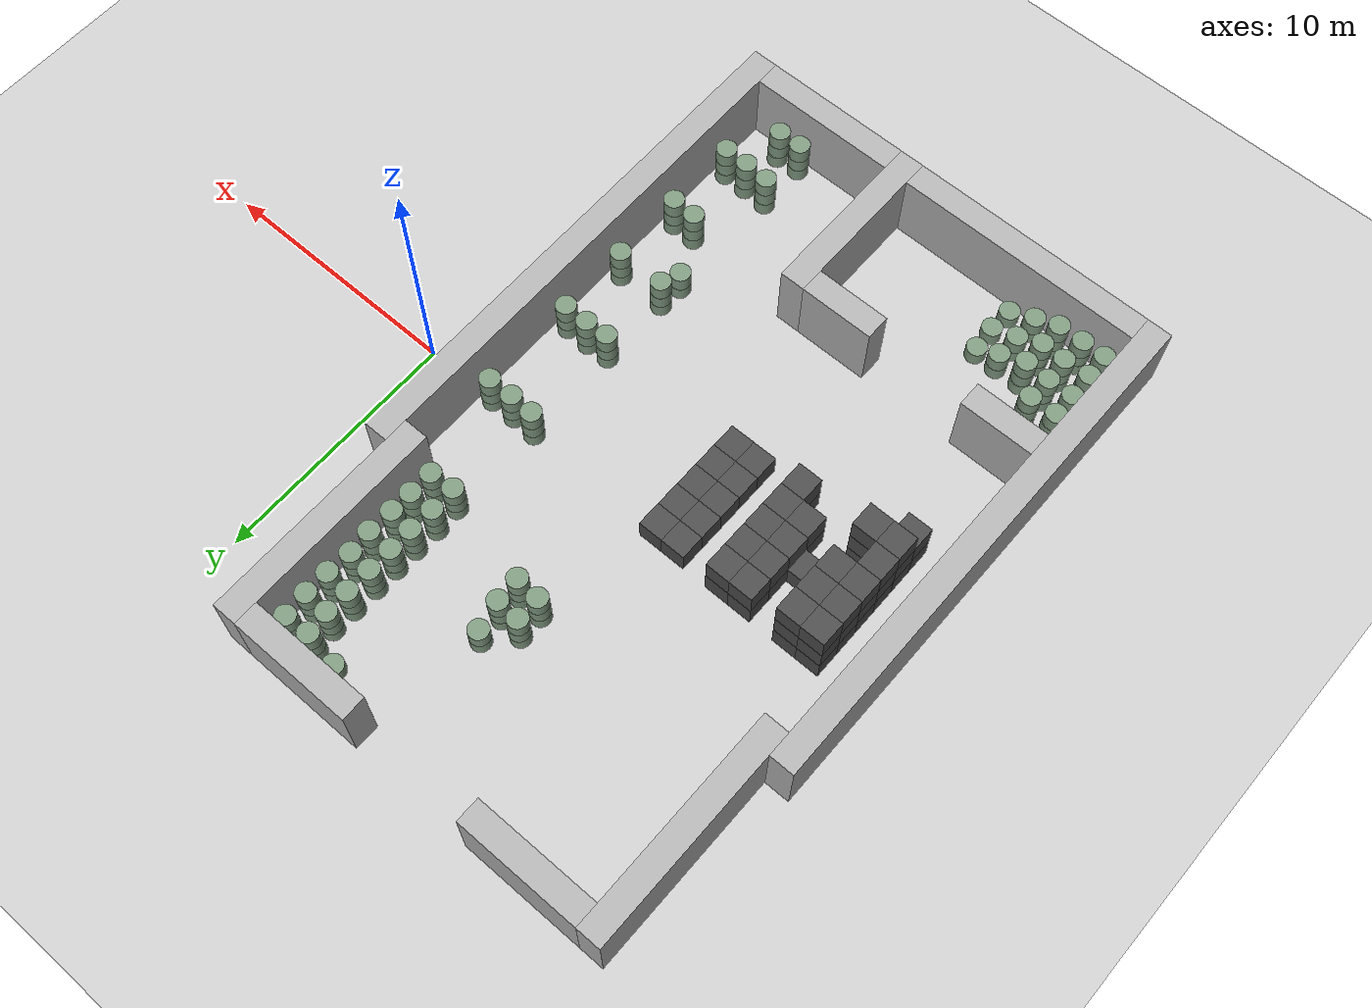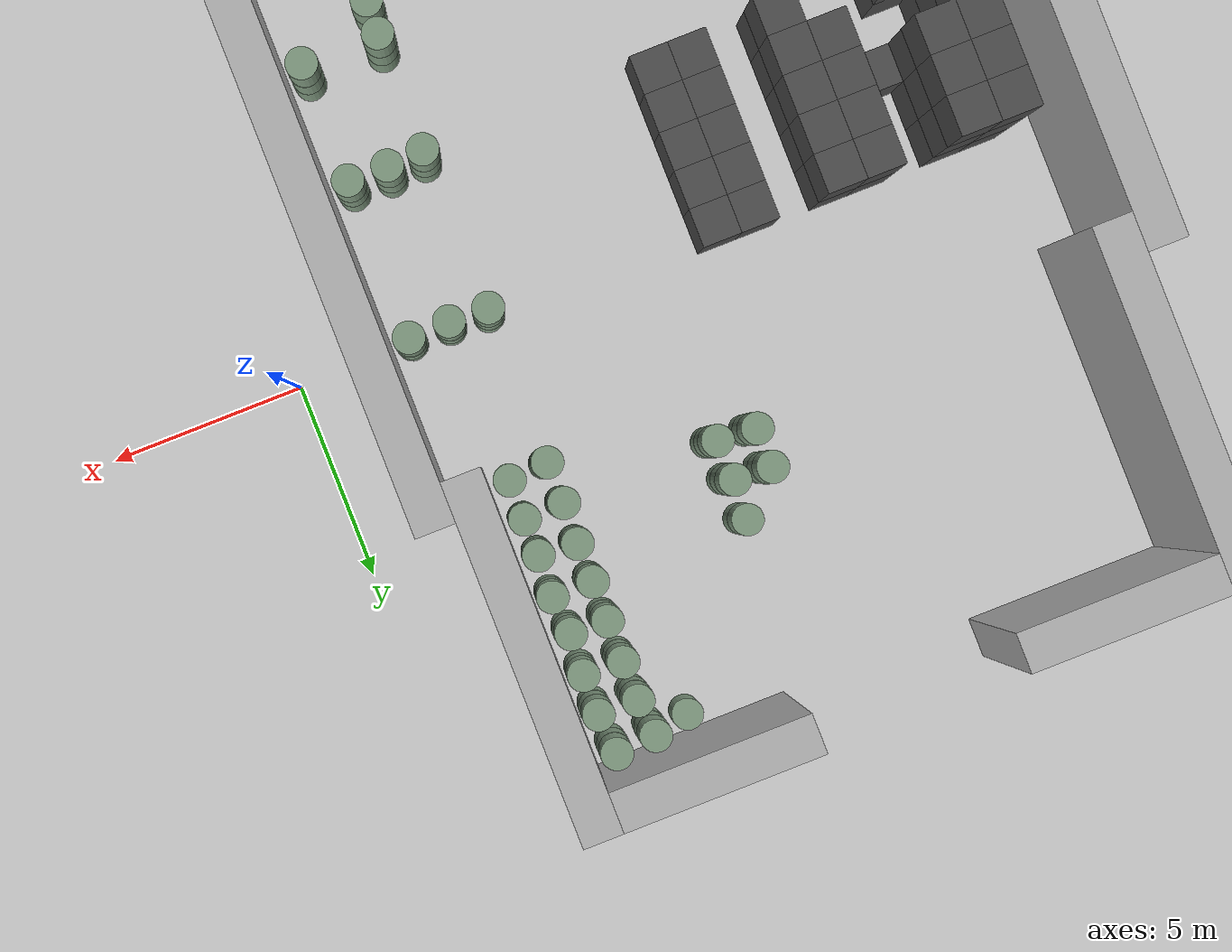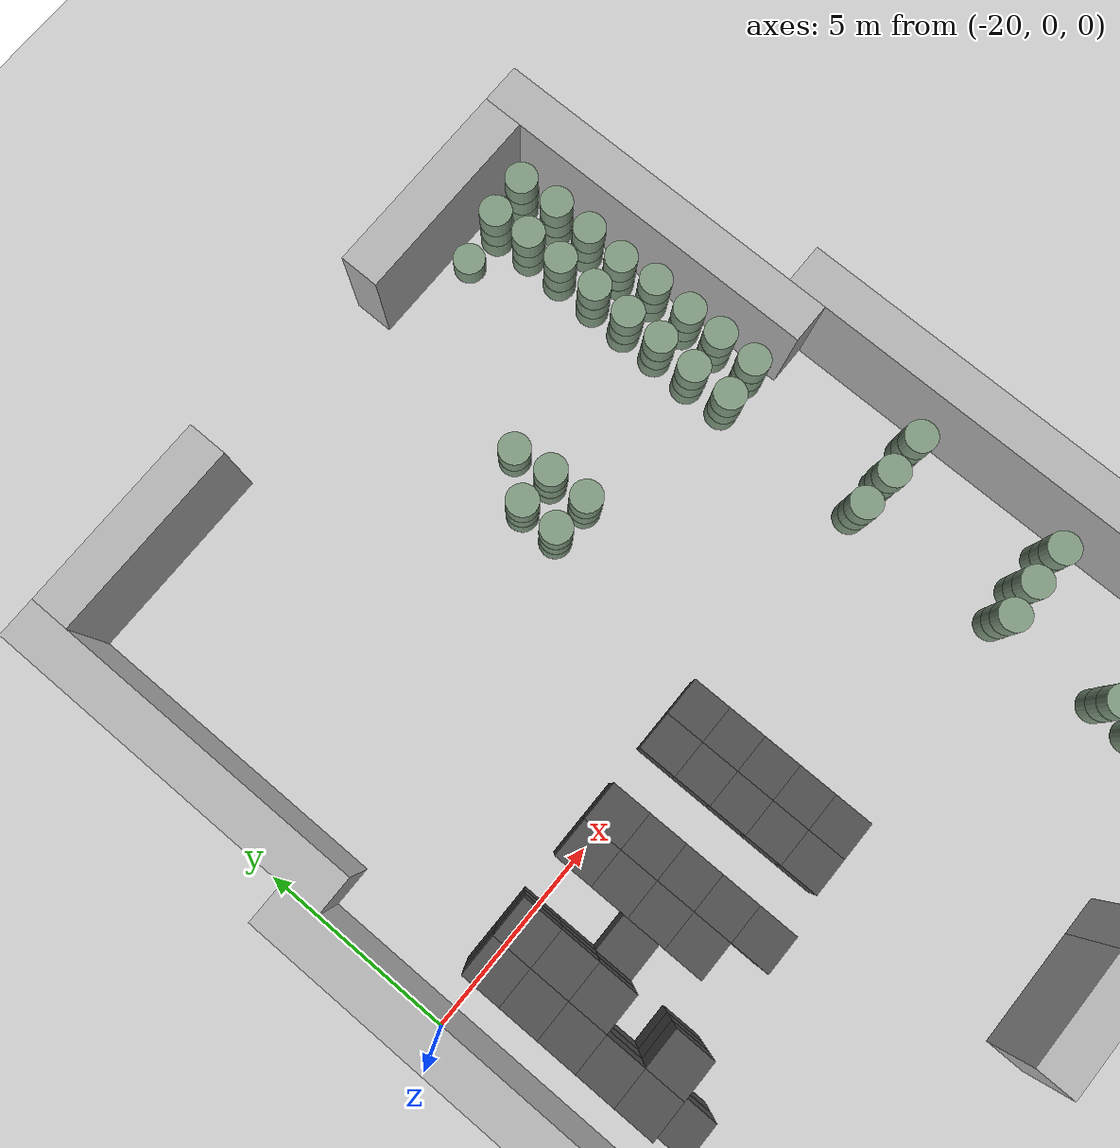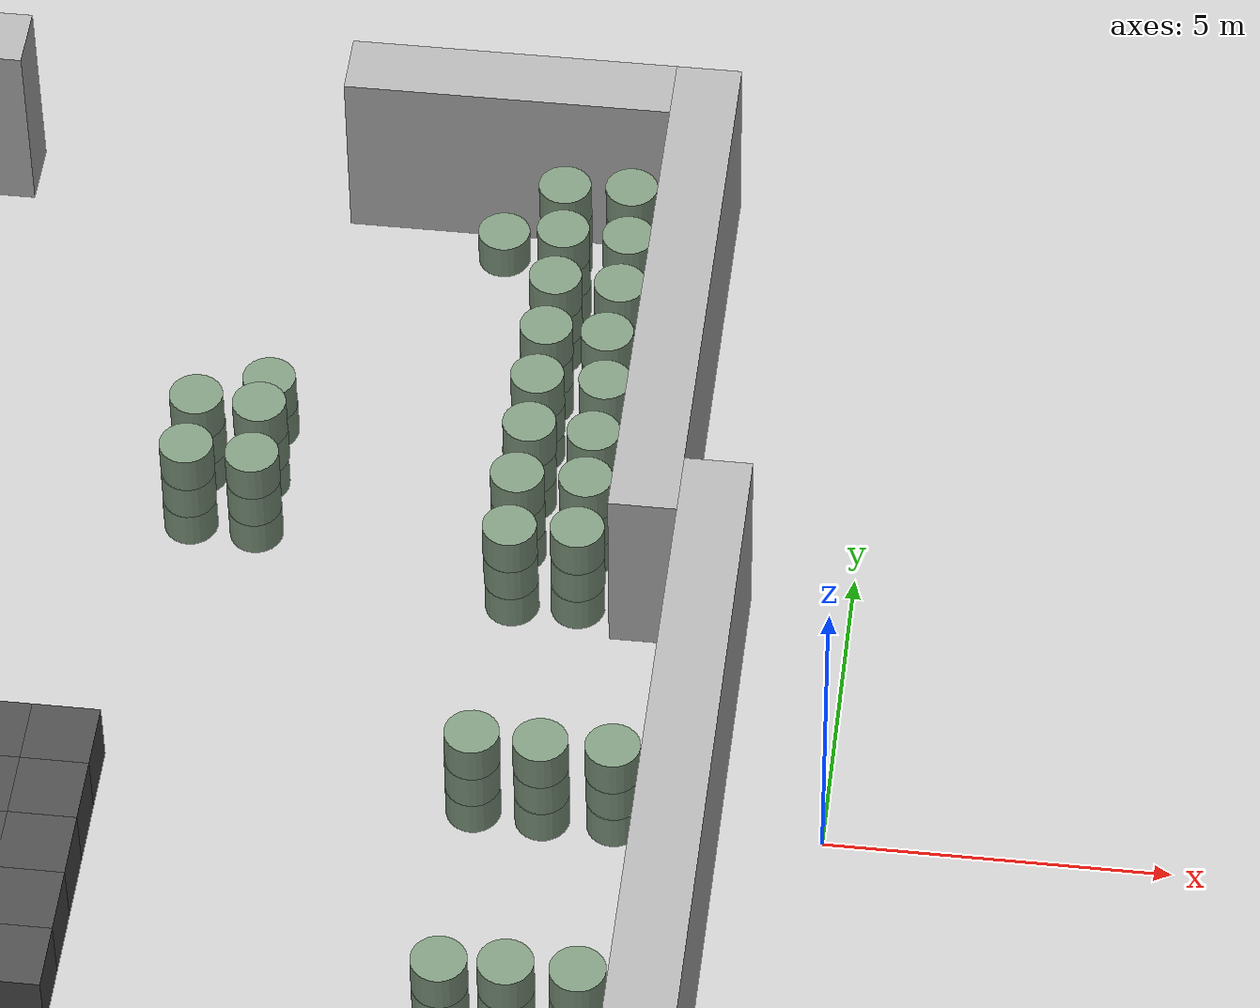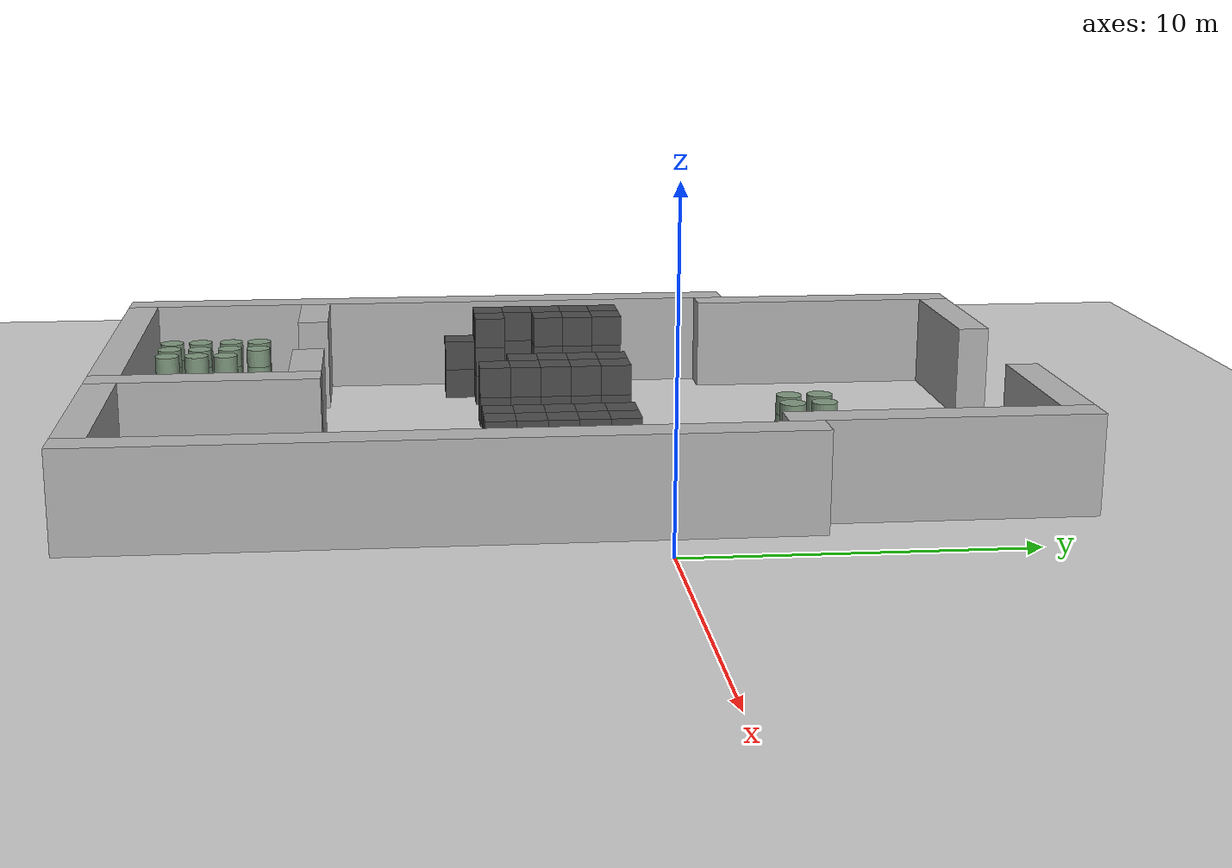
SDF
<sdf version="1.6">
 <world name="default">
  <light name="sun" type="directional">
   <cast_shadows>0</cast_shadows>
   <pose>0 0 10 0 -0 0</pose>
   <diffuse>0.8 0.8 0.8 1</diffuse>
   <specular>0.2 0.2 0.2 1</specular>
   <attenuation>
    <range>1000</range>
    <constant>0.9</constant>
    <linear>0.01</linear>
    <quadratic>0.001</quadratic>
   </attenuation>
   <direction>-0.5 0.1 -0.9</direction>
  </light>
  <include><uri>model://ground_plane</uri></include>
  <gravity>0 0 -9.8</gravity>
  <magnetic_field>6e-06 2.3e-05 -4.2e-05</magnetic_field>
  <atmosphere type="adiabatic"/>
  <physics name="default_physics" default="0" type="ode">
   <max_step_size>0.001</max_step_size>
   <real_time_factor>1</real_time_factor>
   <real_time_update_rate>1000</real_time_update_rate>
  </physics>
  <scene><ambient>0.4 0.4 0.4 1</ambient><background>0.7 0.7 0.7 1</background><shadows>0</shadows></scene>
  <spherical_coordinates>
   <surface_model>EARTH_WGS84</surface_model>
   <latitude_deg>0</latitude_deg>
   <longitude_deg>0</longitude_deg>
   <elevation>0</elevation>
   <heading_deg>0</heading_deg>
  </spherical_coordinates>
  <model name="wall_0">
   <pose>-20.0 -6.0 1.5 0 -0 0</pose>
   <static>True</static>
   <link name="link">
    <inertial>
     <mass>100</mass>
     <inertia>
      <ixx>0.166667</ixx>
      <ixy>0</ixy>
      <ixz>0</ixz>
      <iyy>0.166667</iyy>
      <iyz>0</iyz>
      <izz>0.166667</izz>
     </inertia>
    </inertial>
    <collision name="collision"><geometry><box><size>1.0 21.0 3.0</size></box></geometry></collision>
    <visual name="visual">
     <geometry><box><size>1.0 21.0 3.0</size></box></geometry>
     <material><ambient>0.7 0.7 0.7 1</ambient><diffuse>0.7 0.7 0.7 1</diffuse></material>
    </visual>
   </link>
  </model>
  <model name="wall_1">
   <pose>-19.0 8.0 1.5 0 -0 0</pose>
   <static>True</static>
   <link name="link">
    <inertial>
     <mass>100</mass>
     <inertia>
      <ixx>0.166667</ixx>
      <ixy>0</ixy>
      <ixz>0</ixz>
      <iyy>0.166667</iyy>
      <iyz>0</iyz>
      <izz>0.166667</izz>
     </inertia>
    </inertial>
    <collision name="collision"><geometry><box><size>1.0 9.0 3.0</size></box></geometry></collision>
    <visual name="visual">
     <geometry><box><size>1.0 9.0 3.0</size></box></geometry>
     <material><ambient>0.7 0.7 0.7 1</ambient><diffuse>0.7 0.7 0.7 1</diffuse></material>
    </visual>
   </link>
  </model>
  <model name="wall_2">
   <pose>-9.0 -13.0 1.5 0 -0 0</pose>
   <static>True</static>
   <link name="link">
    <inertial>
     <mass>100</mass>
     <inertia>
      <ixx>0.166667</ixx>
      <ixy>0</ixy>
      <ixz>0</ixz>
      <iyy>0.166667</iyy>
      <iyz>0</iyz>
      <izz>0.166667</izz>
     </inertia>
    </inertial>
    <collision name="collision"><geometry><box><size>1.0 7.0 3.0</size></box></geometry></collision>
    <visual name="visual">
     <geometry><box><size>1.0 7.0 3.0</size></box></geometry>
     <material><ambient>0.7 0.7 0.7 1</ambient><diffuse>0.7 0.7 0.7 1</diffuse></material>
    </visual>
   </link>
  </model>
  <model name="wall_3">
   <pose>-3.0 8.0 1.5 0 -0 0</pose>
   <static>True</static>
   <link name="link">
    <inertial>
     <mass>100</mass>
     <inertia>
      <ixx>0.166667</ixx>
      <ixy>0</ixy>
      <ixz>0</ixz>
      <iyy>0.166667</iyy>
      <iyz>0</iyz>
      <izz>0.166667</izz>
     </inertia>
    </inertial>
    <collision name="collision"><geometry><box><size>1.0 9.0 3.0</size></box></geometry></collision>
    <visual name="visual">
     <geometry><box><size>1.0 9.0 3.0</size></box></geometry>
     <material><ambient>0.7 0.7 0.7 1</ambient><diffuse>0.7 0.7 0.7 1</diffuse></material>
    </visual>
   </link>
  </model>
  <model name="wall_4">
   <pose>-2.0 -6.0 1.5 0 -0 0</pose>
   <static>True</static>
   <link name="link">
    <inertial>
     <mass>100</mass>
     <inertia>
      <ixx>0.166667</ixx>
      <ixy>0</ixy>
      <ixz>0</ixz>
      <iyy>0.166667</iyy>
      <iyz>0</iyz>
      <izz>0.166667</izz>
     </inertia>
    </inertial>
    <collision name="collision"><geometry><box><size>1.0 21.0 3.0</size></box></geometry></collision>
    <visual name="visual">
     <geometry><box><size>1.0 21.0 3.0</size></box></geometry>
     <material><ambient>0.7 0.7 0.7 1</ambient><diffuse>0.7 0.7 0.7 1</diffuse></material>
    </visual>
   </link>
  </model>
  <model name="wall_5">
   <pose>-14.5 -16.0 1.5 0 -0 0</pose>
   <static>True</static>
   <link name="link">
    <inertial>
     <mass>100</mass>
     <inertia>
      <ixx>0.166667</ixx>
      <ixy>0</ixy>
      <ixz>0</ixz>
      <iyy>0.166667</iyy>
      <iyz>0</iyz>
      <izz>0.166667</izz>
     </inertia>
    </inertial>
    <collision name="collision"><geometry><box><size>10.0 1.0 3.0</size></box></geometry></collision>
    <visual name="visual">
     <geometry><box><size>10.0 1.0 3.0</size></box></geometry>
     <material><ambient>0.7 0.7 0.7 1</ambient><diffuse>0.7 0.7 0.7 1</diffuse></material>
    </visual>
   </link>
  </model>
  <model name="wall_6">
   <pose>-5.5 -16.0 1.5 0 -0 0</pose>
   <static>True</static>
   <link name="link">
    <inertial>
     <mass>100</mass>
     <inertia>
      <ixx>0.166667</ixx>
      <ixy>0</ixy>
      <ixz>0</ixz>
      <iyy>0.166667</iyy>
      <iyz>0</iyz>
      <izz>0.166667</izz>
     </inertia>
    </inertial>
    <collision name="collision"><geometry><box><size>6.0 1.0 3.0</size></box></geometry></collision>
    <visual name="visual">
     <geometry><box><size>6.0 1.0 3.0</size></box></geometry>
     <material><ambient>0.7 0.7 0.7 1</ambient><diffuse>0.7 0.7 0.7 1</diffuse></material>
    </visual>
   </link>
  </model>
  <model name="wall_7">
   <pose>-18.0 -10.0 1.5 0 -0 0</pose>
   <static>True</static>
   <link name="link">
    <inertial>
     <mass>100</mass>
     <inertia>
      <ixx>0.166667</ixx>
      <ixy>0</ixy>
      <ixz>0</ixz>
      <iyy>0.166667</iyy>
      <iyz>0</iyz>
      <izz>0.166667</izz>
     </inertia>
    </inertial>
    <collision name="collision"><geometry><box><size>3.0 1.0 3.0</size></box></geometry></collision>
    <visual name="visual">
     <geometry><box><size>3.0 1.0 3.0</size></box></geometry>
     <material><ambient>0.7 0.7 0.7 1</ambient><diffuse>0.7 0.7 0.7 1</diffuse></material>
    </visual>
   </link>
  </model>
  <model name="wall_8">
   <pose>-11.0 -10.0 1.5 0 -0 0</pose>
   <static>True</static>
   <link name="link">
    <inertial>
     <mass>100</mass>
     <inertia>
      <ixx>0.166667</ixx>
      <ixy>0</ixy>
      <ixz>0</ixz>
      <iyy>0.166667</iyy>
      <iyz>0</iyz>
      <izz>0.166667</izz>
     </inertia>
    </inertial>
    <collision name="collision"><geometry><box><size>3.0 1.0 3.0</size></box></geometry></collision>
    <visual name="visual">
     <geometry><box><size>3.0 1.0 3.0</size></box></geometry>
     <material><ambient>0.7 0.7 0.7 1</ambient><diffuse>0.7 0.7 0.7 1</diffuse></material>
    </visual>
   </link>
  </model>
  <model name="wall_9">
   <pose>-16.0 12.0 1.5 0 -0 0</pose>
   <static>True</static>
   <link name="link">
    <inertial>
     <mass>100</mass>
     <inertia>
      <ixx>0.166667</ixx>
      <ixy>0</ixy>
      <ixz>0</ixz>
      <iyy>0.166667</iyy>
      <iyz>0</iyz>
      <izz>0.166667</izz>
     </inertia>
    </inertial>
    <collision name="collision"><geometry><box><size>5.0 1.0 3.0</size></box></geometry></collision>
    <visual name="visual">
     <geometry><box><size>5.0 1.0 3.0</size></box></geometry>
     <material><ambient>0.7 0.7 0.7 1</ambient><diffuse>0.7 0.7 0.7 1</diffuse></material>
    </visual>
   </link>
  </model>
  <model name="wall_10">
   <pose>-6.0 12.0 1.5 0 -0 0</pose>
   <static>True</static>
   <link name="link">
    <inertial>
     <mass>100</mass>
     <inertia>
      <ixx>0.166667</ixx>
      <ixy>0</ixy>
      <ixz>0</ixz>
      <iyy>0.166667</iyy>
      <iyz>0</iyz>
      <izz>0.166667</izz>
     </inertia>
    </inertial>
    <collision name="collision"><geometry><box><size>5.0 1.0 3.0</size></box></geometry></collision>
    <visual name="visual">
     <geometry><box><size>5.0 1.0 3.0</size></box></geometry>
     <material><ambient>0.7 0.7 0.7 1</ambient><diffuse>0.7 0.7 0.7 1</diffuse></material>
    </visual>
   </link>
  </model>
  <model name="unit_box_0">
   <pose>-18.0 -5.0 0.5 0 -0 0</pose>
   <static>True</static>
   <link name="link">
    <inertial>
     <mass>100</mass>
     <inertia>
      <ixx>0.166667</ixx>
      <ixy>0</ixy>
      <ixz>0</ixz>
      <iyy>0.166667</iyy>
      <iyz>0</iyz>
      <izz>0.166667</izz>
     </inertia>
    </inertial>
    <collision name="collision"><geometry><box><size>1.0 1.0 1.0</size></box></geometry></collision>
    <visual name="visual">
     <geometry><box><size>1.0 1.0 1.0</size></box></geometry>
     <material><ambient>0.3 0.3 0.3 1</ambient><diffuse>0.3 0.3 0.3 1</diffuse></material>
    </visual>
   </link>
  </model>
  <model name="unit_box_1">
   <pose>-18.0 -5.0 1.5 0 -0 0</pose>
   <static>True</static>
   <link name="link">
    <inertial>
     <mass>100</mass>
     <inertia>
      <ixx>0.166667</ixx>
      <ixy>0</ixy>
      <ixz>0</ixz>
      <iyy>0.166667</iyy>
      <iyz>0</iyz>
      <izz>0.166667</izz>
     </inertia>
    </inertial>
    <collision name="collision"><geometry><box><size>1.0 1.0 1.0</size></box></geometry></collision>
    <visual name="visual">
     <geometry><box><size>1.0 1.0 1.0</size></box></geometry>
     <material><ambient>0.3 0.3 0.3 1</ambient><diffuse>0.3 0.3 0.3 1</diffuse></material>
    </visual>
   </link>
  </model>
  <model name="unit_box_2">
   <pose>-18.0 -4.0 0.5 0 -0 0</pose>
   <static>True</static>
   <link name="link">
    <inertial>
     <mass>100</mass>
     <inertia>
      <ixx>0.166667</ixx>
      <ixy>0</ixy>
      <ixz>0</ixz>
      <iyy>0.166667</iyy>
      <iyz>0</iyz>
      <izz>0.166667</izz>
     </inertia>
    </inertial>
    <collision name="collision"><geometry><box><size>1.0 1.0 1.0</size></box></geometry></collision>
    <visual name="visual">
     <geometry><box><size>1.0 1.0 1.0</size></box></geometry>
     <material><ambient>0.3 0.3 0.3 1</ambient><diffuse>0.3 0.3 0.3 1</diffuse></material>
    </visual>
   </link>
  </model>
  <model name="unit_box_3">
   <pose>-18.0 -4.0 1.5 0 -0 0</pose>
   <static>True</static>
   <link name="link">
    <inertial>
     <mass>100</mass>
     <inertia>
      <ixx>0.166667</ixx>
      <ixy>0</ixy>
      <ixz>0</ixz>
      <iyy>0.166667</iyy>
      <iyz>0</iyz>
      <izz>0.166667</izz>
     </inertia>
    </inertial>
    <collision name="collision"><geometry><box><size>1.0 1.0 1.0</size></box></geometry></collision>
    <visual name="visual">
     <geometry><box><size>1.0 1.0 1.0</size></box></geometry>
     <material><ambient>0.3 0.3 0.3 1</ambient><diffuse>0.3 0.3 0.3 1</diffuse></material>
    </visual>
   </link>
  </model>
  <model name="unit_box_4">
   <pose>-18.0 -4.0 2.5 0 -0 0</pose>
   <static>True</static>
   <link name="link">
    <inertial>
     <mass>100</mass>
     <inertia>
      <ixx>0.166667</ixx>
      <ixy>0</ixy>
      <ixz>0</ixz>
      <iyy>0.166667</iyy>
      <iyz>0</iyz>
      <izz>0.166667</izz>
     </inertia>
    </inertial>
    <collision name="collision"><geometry><box><size>1.0 1.0 1.0</size></box></geometry></collision>
    <visual name="visual">
     <geometry><box><size>1.0 1.0 1.0</size></box></geometry>
     <material><ambient>0.3 0.3 0.3 1</ambient><diffuse>0.3 0.3 0.3 1</diffuse></material>
    </visual>
   </link>
  </model>
  <model name="unit_box_5">
   <pose>-18.0 -3.0 0.5 0 -0 0</pose>
   <static>True</static>
   <link name="link">
    <inertial>
     <mass>100</mass>
     <inertia>
      <ixx>0.166667</ixx>
      <ixy>0</ixy>
      <ixz>0</ixz>
      <iyy>0.166667</iyy>
      <iyz>0</iyz>
      <izz>0.166667</izz>
     </inertia>
    </inertial>
    <collision name="collision"><geometry><box><size>1.0 1.0 1.0</size></box></geometry></collision>
    <visual name="visual">
     <geometry><box><size>1.0 1.0 1.0</size></box></geometry>
     <material><ambient>0.3 0.3 0.3 1</ambient><diffuse>0.3 0.3 0.3 1</diffuse></material>
    </visual>
   </link>
  </model>
  <model name="unit_box_6">
   <pose>-18.0 -3.0 1.5 0 -0 0</pose>
   <static>True</static>
   <link name="link">
    <inertial>
     <mass>100</mass>
     <inertia>
      <ixx>0.166667</ixx>
      <ixy>0</ixy>
      <ixz>0</ixz>
      <iyy>0.166667</iyy>
      <iyz>0</iyz>
      <izz>0.166667</izz>
     </inertia>
    </inertial>
    <collision name="collision"><geometry><box><size>1.0 1.0 1.0</size></box></geometry></collision>
    <visual name="visual">
     <geometry><box><size>1.0 1.0 1.0</size></box></geometry>
     <material><ambient>0.3 0.3 0.3 1</ambient><diffuse>0.3 0.3 0.3 1</diffuse></material>
    </visual>
   </link>
  </model>
  <model name="unit_box_7">
   <pose>-18.0 -3.0 2.5 0 -0 0</pose>
   <static>True</static>
   <link name="link">
    <inertial>
     <mass>100</mass>
     <inertia>
      <ixx>0.166667</ixx>
      <ixy>0</ixy>
      <ixz>0</ixz>
      <iyy>0.166667</iyy>
      <iyz>0</iyz>
      <izz>0.166667</izz>
     </inertia>
    </inertial>
    <collision name="collision"><geometry><box><size>1.0 1.0 1.0</size></box></geometry></collision>
    <visual name="visual">
     <geometry><box><size>1.0 1.0 1.0</size></box></geometry>
     <material><ambient>0.3 0.3 0.3 1</ambient><diffuse>0.3 0.3 0.3 1</diffuse></material>
    </visual>
   </link>
  </model>
  <model name="unit_box_8">
   <pose>-18.0 -2.0 0.5 0 -0 0</pose>
   <static>True</static>
   <link name="link">
    <inertial>
     <mass>100</mass>
     <inertia>
      <ixx>0.166667</ixx>
      <ixy>0</ixy>
      <ixz>0</ixz>
      <iyy>0.166667</iyy>
      <iyz>0</iyz>
      <izz>0.166667</izz>
     </inertia>
    </inertial>
    <collision name="collision"><geometry><box><size>1.0 1.0 1.0</size></box></geometry></collision>
    <visual name="visual">
     <geometry><box><size>1.0 1.0 1.0</size></box></geometry>
     <material><ambient>0.3 0.3 0.3 1</ambient><diffuse>0.3 0.3 0.3 1</diffuse></material>
    </visual>
   </link>
  </model>
  <model name="unit_box_9">
   <pose>-18.0 -2.0 1.5 0 -0 0</pose>
   <static>True</static>
   <link name="link">
    <inertial>
     <mass>100</mass>
     <inertia>
      <ixx>0.166667</ixx>
      <ixy>0</ixy>
      <ixz>0</ixz>
      <iyy>0.166667</iyy>
      <iyz>0</iyz>
      <izz>0.166667</izz>
     </inertia>
    </inertial>
    <collision name="collision"><geometry><box><size>1.0 1.0 1.0</size></box></geometry></collision>
    <visual name="visual">
     <geometry><box><size>1.0 1.0 1.0</size></box></geometry>
     <material><ambient>0.3 0.3 0.3 1</ambient><diffuse>0.3 0.3 0.3 1</diffuse></material>
    </visual>
   </link>
  </model>
  <model name="unit_box_10">
   <pose>-18.0 -2.0 2.5 0 -0 0</pose>
   <static>True</static>
   <link name="link">
    <inertial>
     <mass>100</mass>
     <inertia>
      <ixx>0.166667</ixx>
      <ixy>0</ixy>
      <ixz>0</ixz>
      <iyy>0.166667</iyy>
      <iyz>0</iyz>
      <izz>0.166667</izz>
     </inertia>
    </inertial>
    <collision name="collision"><geometry><box><size>1.0 1.0 1.0</size></box></geometry></collision>
    <visual name="visual">
     <geometry><box><size>1.0 1.0 1.0</size></box></geometry>
     <material><ambient>0.3 0.3 0.3 1</ambient><diffuse>0.3 0.3 0.3 1</diffuse></material>
    </visual>
   </link>
  </model>
  <model name="unit_box_11">
   <pose>-18.0 -1.0 0.5 0 -0 0</pose>
   <static>True</static>
   <link name="link">
    <inertial>
     <mass>100</mass>
     <inertia>
      <ixx>0.166667</ixx>
      <ixy>0</ixy>
      <ixz>0</ixz>
      <iyy>0.166667</iyy>
      <iyz>0</iyz>
      <izz>0.166667</izz>
     </inertia>
    </inertial>
    <collision name="collision"><geometry><box><size>1.0 1.0 1.0</size></box></geometry></collision>
    <visual name="visual">
     <geometry><box><size>1.0 1.0 1.0</size></box></geometry>
     <material><ambient>0.3 0.3 0.3 1</ambient><diffuse>0.3 0.3 0.3 1</diffuse></material>
    </visual>
   </link>
  </model>
  <model name="unit_box_12">
   <pose>-18.0 -1.0 1.5 0 -0 0</pose>
   <static>True</static>
   <link name="link">
    <inertial>
     <mass>100</mass>
     <inertia>
      <ixx>0.166667</ixx>
      <ixy>0</ixy>
      <ixz>0</ixz>
      <iyy>0.166667</iyy>
      <iyz>0</iyz>
      <izz>0.166667</izz>
     </inertia>
    </inertial>
    <collision name="collision"><geometry><box><size>1.0 1.0 1.0</size></box></geometry></collision>
    <visual name="visual">
     <geometry><box><size>1.0 1.0 1.0</size></box></geometry>
     <material><ambient>0.3 0.3 0.3 1</ambient><diffuse>0.3 0.3 0.3 1</diffuse></material>
    </visual>
   </link>
  </model>
  <model name="unit_box_13">
   <pose>-18.0 -1.0 2.5 0 -0 0</pose>
   <static>True</static>
   <link name="link">
    <inertial>
     <mass>100</mass>
     <inertia>
      <ixx>0.166667</ixx>
      <ixy>0</ixy>
      <ixz>0</ixz>
      <iyy>0.166667</iyy>
      <iyz>0</iyz>
      <izz>0.166667</izz>
     </inertia>
    </inertial>
    <collision name="collision"><geometry><box><size>1.0 1.0 1.0</size></box></geometry></collision>
    <visual name="visual">
     <geometry><box><size>1.0 1.0 1.0</size></box></geometry>
     <material><ambient>0.3 0.3 0.3 1</ambient><diffuse>0.3 0.3 0.3 1</diffuse></material>
    </visual>
   </link>
  </model>
  <model name="unit_box_14">
   <pose>-18.0 0.0 0.5 0 -0 0</pose>
   <static>True</static>
   <link name="link">
    <inertial>
     <mass>100</mass>
     <inertia>
      <ixx>0.166667</ixx>
      <ixy>0</ixy>
      <ixz>0</ixz>
      <iyy>0.166667</iyy>
      <iyz>0</iyz>
      <izz>0.166667</izz>
     </inertia>
    </inertial>
    <collision name="collision"><geometry><box><size>1.0 1.0 1.0</size></box></geometry></collision>
    <visual name="visual">
     <geometry><box><size>1.0 1.0 1.0</size></box></geometry>
     <material><ambient>0.3 0.3 0.3 1</ambient><diffuse>0.3 0.3 0.3 1</diffuse></material>
    </visual>
   </link>
  </model>
  <model name="unit_box_15">
   <pose>-18.0 0.0 1.5 0 -0 0</pose>
   <static>True</static>
   <link name="link">
    <inertial>
     <mass>100</mass>
     <inertia>
      <ixx>0.166667</ixx>
      <ixy>0</ixy>
      <ixz>0</ixz>
      <iyy>0.166667</iyy>
      <iyz>0</iyz>
      <izz>0.166667</izz>
     </inertia>
    </inertial>
    <collision name="collision"><geometry><box><size>1.0 1.0 1.0</size></box></geometry></collision>
    <visual name="visual">
     <geometry><box><size>1.0 1.0 1.0</size></box></geometry>
     <material><ambient>0.3 0.3 0.3 1</ambient><diffuse>0.3 0.3 0.3 1</diffuse></material>
    </visual>
   </link>
  </model>
  <model name="unit_box_16">
   <pose>-18.0 0.0 2.5 0 -0 0</pose>
   <static>True</static>
   <link name="link">
    <inertial>
     <mass>100</mass>
     <inertia>
      <ixx>0.166667</ixx>
      <ixy>0</ixy>
      <ixz>0</ixz>
      <iyy>0.166667</iyy>
      <iyz>0</iyz>
      <izz>0.166667</izz>
     </inertia>
    </inertial>
    <collision name="collision"><geometry><box><size>1.0 1.0 1.0</size></box></geometry></collision>
    <visual name="visual">
     <geometry><box><size>1.0 1.0 1.0</size></box></geometry>
     <material><ambient>0.3 0.3 0.3 1</ambient><diffuse>0.3 0.3 0.3 1</diffuse></material>
    </visual>
   </link>
  </model>
  <model name="unit_box_17">
   <pose>-17.0 -4.0 0.5 0 -0 0</pose>
   <static>True</static>
   <link name="link">
    <inertial>
     <mass>100</mass>
     <inertia>
      <ixx>0.166667</ixx>
      <ixy>0</ixy>
      <ixz>0</ixz>
      <iyy>0.166667</iyy>
      <iyz>0</iyz>
      <izz>0.166667</izz>
     </inertia>
    </inertial>
    <collision name="collision"><geometry><box><size>1.0 1.0 1.0</size></box></geometry></collision>
    <visual name="visual">
     <geometry><box><size>1.0 1.0 1.0</size></box></geometry>
     <material><ambient>0.3 0.3 0.3 1</ambient><diffuse>0.3 0.3 0.3 1</diffuse></material>
    </visual>
   </link>
  </model>
  <model name="unit_box_18">
   <pose>-17.0 -4.0 1.5 0 -0 0</pose>
   <static>True</static>
   <link name="link">
    <inertial>
     <mass>100</mass>
     <inertia>
      <ixx>0.166667</ixx>
      <ixy>0</ixy>
      <ixz>0</ixz>
      <iyy>0.166667</iyy>
      <iyz>0</iyz>
      <izz>0.166667</izz>
     </inertia>
    </inertial>
    <collision name="collision"><geometry><box><size>1.0 1.0 1.0</size></box></geometry></collision>
    <visual name="visual">
     <geometry><box><size>1.0 1.0 1.0</size></box></geometry>
     <material><ambient>0.3 0.3 0.3 1</ambient><diffuse>0.3 0.3 0.3 1</diffuse></material>
    </visual>
   </link>
  </model>
  <model name="unit_box_19">
   <pose>-17.0 -4.0 2.5 0 -0 0</pose>
   <static>True</static>
   <link name="link">
    <inertial>
     <mass>100</mass>
     <inertia>
      <ixx>0.166667</ixx>
      <ixy>0</ixy>
      <ixz>0</ixz>
      <iyy>0.166667</iyy>
      <iyz>0</iyz>
      <izz>0.166667</izz>
     </inertia>
    </inertial>
    <collision name="collision"><geometry><box><size>1.0 1.0 1.0</size></box></geometry></collision>
    <visual name="visual">
     <geometry><box><size>1.0 1.0 1.0</size></box></geometry>
     <material><ambient>0.3 0.3 0.3 1</ambient><diffuse>0.3 0.3 0.3 1</diffuse></material>
    </visual>
   </link>
  </model>
  <model name="unit_box_20">
   <pose>-17.0 -2.0 0.5 0 -0 0</pose>
   <static>True</static>
   <link name="link">
    <inertial>
     <mass>100</mass>
     <inertia>
      <ixx>0.166667</ixx>
      <ixy>0</ixy>
      <ixz>0</ixz>
      <iyy>0.166667</iyy>
      <iyz>0</iyz>
      <izz>0.166667</izz>
     </inertia>
    </inertial>
    <collision name="collision"><geometry><box><size>1.0 1.0 1.0</size></box></geometry></collision>
    <visual name="visual">
     <geometry><box><size>1.0 1.0 1.0</size></box></geometry>
     <material><ambient>0.3 0.3 0.3 1</ambient><diffuse>0.3 0.3 0.3 1</diffuse></material>
    </visual>
   </link>
  </model>
  <model name="unit_box_21">
   <pose>-17.0 -2.0 1.5 0 -0 0</pose>
   <static>True</static>
   <link name="link">
    <inertial>
     <mass>100</mass>
     <inertia>
      <ixx>0.166667</ixx>
      <ixy>0</ixy>
      <ixz>0</ixz>
      <iyy>0.166667</iyy>
      <iyz>0</iyz>
      <izz>0.166667</izz>
     </inertia>
    </inertial>
    <collision name="collision"><geometry><box><size>1.0 1.0 1.0</size></box></geometry></collision>
    <visual name="visual">
     <geometry><box><size>1.0 1.0 1.0</size></box></geometry>
     <material><ambient>0.3 0.3 0.3 1</ambient><diffuse>0.3 0.3 0.3 1</diffuse></material>
    </visual>
   </link>
  </model>
  <model name="unit_box_22">
   <pose>-17.0 -2.0 2.5 0 -0 0</pose>
   <static>True</static>
   <link name="link">
    <inertial>
     <mass>100</mass>
     <inertia>
      <ixx>0.166667</ixx>
      <ixy>0</ixy>
      <ixz>0</ixz>
      <iyy>0.166667</iyy>
      <iyz>0</iyz>
      <izz>0.166667</izz>
     </inertia>
    </inertial>
    <collision name="collision"><geometry><box><size>1.0 1.0 1.0</size></box></geometry></collision>
    <visual name="visual">
     <geometry><box><size>1.0 1.0 1.0</size></box></geometry>
     <material><ambient>0.3 0.3 0.3 1</ambient><diffuse>0.3 0.3 0.3 1</diffuse></material>
    </visual>
   </link>
  </model>
  <model name="unit_box_23">
   <pose>-17.0 -1.0 0.5 0 -0 0</pose>
   <static>True</static>
   <link name="link">
    <inertial>
     <mass>100</mass>
     <inertia>
      <ixx>0.166667</ixx>
      <ixy>0</ixy>
      <ixz>0</ixz>
      <iyy>0.166667</iyy>
      <iyz>0</iyz>
      <izz>0.166667</izz>
     </inertia>
    </inertial>
    <collision name="collision"><geometry><box><size>1.0 1.0 1.0</size></box></geometry></collision>
    <visual name="visual">
     <geometry><box><size>1.0 1.0 1.0</size></box></geometry>
     <material><ambient>0.3 0.3 0.3 1</ambient><diffuse>0.3 0.3 0.3 1</diffuse></material>
    </visual>
   </link>
  </model>
  <model name="unit_box_24">
   <pose>-17.0 -1.0 1.5 0 -0 0</pose>
   <static>True</static>
   <link name="link">
    <inertial>
     <mass>100</mass>
     <inertia>
      <ixx>0.166667</ixx>
      <ixy>0</ixy>
      <ixz>0</ixz>
      <iyy>0.166667</iyy>
      <iyz>0</iyz>
      <izz>0.166667</izz>
     </inertia>
    </inertial>
    <collision name="collision"><geometry><box><size>1.0 1.0 1.0</size></box></geometry></collision>
    <visual name="visual">
     <geometry><box><size>1.0 1.0 1.0</size></box></geometry>
     <material><ambient>0.3 0.3 0.3 1</ambient><diffuse>0.3 0.3 0.3 1</diffuse></material>
    </visual>
   </link>
  </model>
  <model name="unit_box_25">
   <pose>-17.0 -1.0 2.5 0 -0 0</pose>
   <static>True</static>
   <link name="link">
    <inertial>
     <mass>100</mass>
     <inertia>
      <ixx>0.166667</ixx>
      <ixy>0</ixy>
      <ixz>0</ixz>
      <iyy>0.166667</iyy>
      <iyz>0</iyz>
      <izz>0.166667</izz>
     </inertia>
    </inertial>
    <collision name="collision"><geometry><box><size>1.0 1.0 1.0</size></box></geometry></collision>
    <visual name="visual">
     <geometry><box><size>1.0 1.0 1.0</size></box></geometry>
     <material><ambient>0.3 0.3 0.3 1</ambient><diffuse>0.3 0.3 0.3 1</diffuse></material>
    </visual>
   </link>
  </model>
  <model name="unit_box_26">
   <pose>-17.0 0.0 0.5 0 -0 0</pose>
   <static>True</static>
   <link name="link">
    <inertial>
     <mass>100</mass>
     <inertia>
      <ixx>0.166667</ixx>
      <ixy>0</ixy>
      <ixz>0</ixz>
      <iyy>0.166667</iyy>
      <iyz>0</iyz>
      <izz>0.166667</izz>
     </inertia>
    </inertial>
    <collision name="collision"><geometry><box><size>1.0 1.0 1.0</size></box></geometry></collision>
    <visual name="visual">
     <geometry><box><size>1.0 1.0 1.0</size></box></geometry>
     <material><ambient>0.3 0.3 0.3 1</ambient><diffuse>0.3 0.3 0.3 1</diffuse></material>
    </visual>
   </link>
  </model>
  <model name="unit_box_27">
   <pose>-17.0 0.0 1.5 0 -0 0</pose>
   <static>True</static>
   <link name="link">
    <inertial>
     <mass>100</mass>
     <inertia>
      <ixx>0.166667</ixx>
      <ixy>0</ixy>
      <ixz>0</ixz>
      <iyy>0.166667</iyy>
      <iyz>0</iyz>
      <izz>0.166667</izz>
     </inertia>
    </inertial>
    <collision name="collision"><geometry><box><size>1.0 1.0 1.0</size></box></geometry></collision>
    <visual name="visual">
     <geometry><box><size>1.0 1.0 1.0</size></box></geometry>
     <material><ambient>0.3 0.3 0.3 1</ambient><diffuse>0.3 0.3 0.3 1</diffuse></material>
    </visual>
   </link>
  </model>
  <model name="unit_box_28">
   <pose>-17.0 0.0 2.5 0 -0 0</pose>
   <static>True</static>
   <link name="link">
    <inertial>
     <mass>100</mass>
     <inertia>
      <ixx>0.166667</ixx>
      <ixy>0</ixy>
      <ixz>0</ixz>
      <iyy>0.166667</iyy>
      <iyz>0</iyz>
      <izz>0.166667</izz>
     </inertia>
    </inertial>
    <collision name="collision"><geometry><box><size>1.0 1.0 1.0</size></box></geometry></collision>
    <visual name="visual">
     <geometry><box><size>1.0 1.0 1.0</size></box></geometry>
     <material><ambient>0.3 0.3 0.3 1</ambient><diffuse>0.3 0.3 0.3 1</diffuse></material>
    </visual>
   </link>
  </model>
  <model name="unit_box_29">
   <pose>-16.0 -2.0 0.5 0 -0 0</pose>
   <static>True</static>
   <link name="link">
    <inertial>
     <mass>100</mass>
     <inertia>
      <ixx>0.166667</ixx>
      <ixy>0</ixy>
      <ixz>0</ixz>
      <iyy>0.166667</iyy>
      <iyz>0</iyz>
      <izz>0.166667</izz>
     </inertia>
    </inertial>
    <collision name="collision"><geometry><box><size>1.0 1.0 1.0</size></box></geometry></collision>
    <visual name="visual">
     <geometry><box><size>1.0 1.0 1.0</size></box></geometry>
     <material><ambient>0.3 0.3 0.3 1</ambient><diffuse>0.3 0.3 0.3 1</diffuse></material>
    </visual>
   </link>
  </model>
  <model name="unit_box_30">
   <pose>-15.0 -3.0 0.5 0 -0 0</pose>
   <static>True</static>
   <link name="link">
    <inertial>
     <mass>100</mass>
     <inertia>
      <ixx>0.166667</ixx>
      <ixy>0</ixy>
      <ixz>0</ixz>
      <iyy>0.166667</iyy>
      <iyz>0</iyz>
      <izz>0.166667</izz>
     </inertia>
    </inertial>
    <collision name="collision"><geometry><box><size>1.0 1.0 1.0</size></box></geometry></collision>
    <visual name="visual">
     <geometry><box><size>1.0 1.0 1.0</size></box></geometry>
     <material><ambient>0.3 0.3 0.3 1</ambient><diffuse>0.3 0.3 0.3 1</diffuse></material>
    </visual>
   </link>
  </model>
  <model name="unit_box_31">
   <pose>-15.0 -3.0 1.5 0 -0 0</pose>
   <static>True</static>
   <link name="link">
    <inertial>
     <mass>100</mass>
     <inertia>
      <ixx>0.166667</ixx>
      <ixy>0</ixy>
      <ixz>0</ixz>
      <iyy>0.166667</iyy>
      <iyz>0</iyz>
      <izz>0.166667</izz>
     </inertia>
    </inertial>
    <collision name="collision"><geometry><box><size>1.0 1.0 1.0</size></box></geometry></collision>
    <visual name="visual">
     <geometry><box><size>1.0 1.0 1.0</size></box></geometry>
     <material><ambient>0.3 0.3 0.3 1</ambient><diffuse>0.3 0.3 0.3 1</diffuse></material>
    </visual>
   </link>
  </model>
  <model name="unit_box_32">
   <pose>-15.0 -2.0 0.5 0 -0 0</pose>
   <static>True</static>
   <link name="link">
    <inertial>
     <mass>100</mass>
     <inertia>
      <ixx>0.166667</ixx>
      <ixy>0</ixy>
      <ixz>0</ixz>
      <iyy>0.166667</iyy>
      <iyz>0</iyz>
      <izz>0.166667</izz>
     </inertia>
    </inertial>
    <collision name="collision"><geometry><box><size>1.0 1.0 1.0</size></box></geometry></collision>
    <visual name="visual">
     <geometry><box><size>1.0 1.0 1.0</size></box></geometry>
     <material><ambient>0.3 0.3 0.3 1</ambient><diffuse>0.3 0.3 0.3 1</diffuse></material>
    </visual>
   </link>
  </model>
  <model name="unit_box_33">
   <pose>-15.0 -2.0 1.5 0 -0 0</pose>
   <static>True</static>
   <link name="link">
    <inertial>
     <mass>100</mass>
     <inertia>
      <ixx>0.166667</ixx>
      <ixy>0</ixy>
      <ixz>0</ixz>
      <iyy>0.166667</iyy>
      <iyz>0</iyz>
      <izz>0.166667</izz>
     </inertia>
    </inertial>
    <collision name="collision"><geometry><box><size>1.0 1.0 1.0</size></box></geometry></collision>
    <visual name="visual">
     <geometry><box><size>1.0 1.0 1.0</size></box></geometry>
     <material><ambient>0.3 0.3 0.3 1</ambient><diffuse>0.3 0.3 0.3 1</diffuse></material>
    </visual>
   </link>
  </model>
  <model name="unit_box_34">
   <pose>-15.0 -1.0 0.5 0 -0 0</pose>
   <static>True</static>
   <link name="link">
    <inertial>
     <mass>100</mass>
     <inertia>
      <ixx>0.166667</ixx>
      <ixy>0</ixy>
      <ixz>0</ixz>
      <iyy>0.166667</iyy>
      <iyz>0</iyz>
      <izz>0.166667</izz>
     </inertia>
    </inertial>
    <collision name="collision"><geometry><box><size>1.0 1.0 1.0</size></box></geometry></collision>
    <visual name="visual">
     <geometry><box><size>1.0 1.0 1.0</size></box></geometry>
     <material><ambient>0.3 0.3 0.3 1</ambient><diffuse>0.3 0.3 0.3 1</diffuse></material>
    </visual>
   </link>
  </model>
  <model name="unit_box_35">
   <pose>-15.0 -1.0 1.5 0 -0 0</pose>
   <static>True</static>
   <link name="link">
    <inertial>
     <mass>100</mass>
     <inertia>
      <ixx>0.166667</ixx>
      <ixy>0</ixy>
      <ixz>0</ixz>
      <iyy>0.166667</iyy>
      <iyz>0</iyz>
      <izz>0.166667</izz>
     </inertia>
    </inertial>
    <collision name="collision"><geometry><box><size>1.0 1.0 1.0</size></box></geometry></collision>
    <visual name="visual">
     <geometry><box><size>1.0 1.0 1.0</size></box></geometry>
     <material><ambient>0.3 0.3 0.3 1</ambient><diffuse>0.3 0.3 0.3 1</diffuse></material>
    </visual>
   </link>
  </model>
  <model name="unit_box_36">
   <pose>-15.0 0.0 0.5 0 -0 0</pose>
   <static>True</static>
   <link name="link">
    <inertial>
     <mass>100</mass>
     <inertia>
      <ixx>0.166667</ixx>
      <ixy>0</ixy>
      <ixz>0</ixz>
      <iyy>0.166667</iyy>
      <iyz>0</iyz>
      <izz>0.166667</izz>
     </inertia>
    </inertial>
    <collision name="collision"><geometry><box><size>1.0 1.0 1.0</size></box></geometry></collision>
    <visual name="visual">
     <geometry><box><size>1.0 1.0 1.0</size></box></geometry>
     <material><ambient>0.3 0.3 0.3 1</ambient><diffuse>0.3 0.3 0.3 1</diffuse></material>
    </visual>
   </link>
  </model>
  <model name="unit_box_37">
   <pose>-15.0 0.0 1.5 0 -0 0</pose>
   <static>True</static>
   <link name="link">
    <inertial>
     <mass>100</mass>
     <inertia>
      <ixx>0.166667</ixx>
      <ixy>0</ixy>
      <ixz>0</ixz>
      <iyy>0.166667</iyy>
      <iyz>0</iyz>
      <izz>0.166667</izz>
     </inertia>
    </inertial>
    <collision name="collision"><geometry><box><size>1.0 1.0 1.0</size></box></geometry></collision>
    <visual name="visual">
     <geometry><box><size>1.0 1.0 1.0</size></box></geometry>
     <material><ambient>0.3 0.3 0.3 1</ambient><diffuse>0.3 0.3 0.3 1</diffuse></material>
    </visual>
   </link>
  </model>
  <model name="unit_box_38">
   <pose>-14.0 -4.0 0.5 0 -0 0</pose>
   <static>True</static>
   <link name="link">
    <inertial>
     <mass>100</mass>
     <inertia>
      <ixx>0.166667</ixx>
      <ixy>0</ixy>
      <ixz>0</ixz>
      <iyy>0.166667</iyy>
      <iyz>0</iyz>
      <izz>0.166667</izz>
     </inertia>
    </inertial>
    <collision name="collision"><geometry><box><size>1.0 1.0 1.0</size></box></geometry></collision>
    <visual name="visual">
     <geometry><box><size>1.0 1.0 1.0</size></box></geometry>
     <material><ambient>0.3 0.3 0.3 1</ambient><diffuse>0.3 0.3 0.3 1</diffuse></material>
    </visual>
   </link>
  </model>
  <model name="unit_box_39">
   <pose>-14.0 -4.0 1.5 0 -0 0</pose>
   <static>True</static>
   <link name="link">
    <inertial>
     <mass>100</mass>
     <inertia>
      <ixx>0.166667</ixx>
      <ixy>0</ixy>
      <ixz>0</ixz>
      <iyy>0.166667</iyy>
      <iyz>0</iyz>
      <izz>0.166667</izz>
     </inertia>
    </inertial>
    <collision name="collision"><geometry><box><size>1.0 1.0 1.0</size></box></geometry></collision>
    <visual name="visual">
     <geometry><box><size>1.0 1.0 1.0</size></box></geometry>
     <material><ambient>0.3 0.3 0.3 1</ambient><diffuse>0.3 0.3 0.3 1</diffuse></material>
    </visual>
   </link>
  </model>
  <model name="unit_box_40">
   <pose>-14.0 -3.0 0.5 0 -0 0</pose>
   <static>True</static>
   <link name="link">
    <inertial>
     <mass>100</mass>
     <inertia>
      <ixx>0.166667</ixx>
      <ixy>0</ixy>
      <ixz>0</ixz>
      <iyy>0.166667</iyy>
      <iyz>0</iyz>
      <izz>0.166667</izz>
     </inertia>
    </inertial>
    <collision name="collision"><geometry><box><size>1.0 1.0 1.0</size></box></geometry></collision>
    <visual name="visual">
     <geometry><box><size>1.0 1.0 1.0</size></box></geometry>
     <material><ambient>0.3 0.3 0.3 1</ambient><diffuse>0.3 0.3 0.3 1</diffuse></material>
    </visual>
   </link>
  </model>
  <model name="unit_box_41">
   <pose>-14.0 -3.0 1.5 0 -0 0</pose>
   <static>True</static>
   <link name="link">
    <inertial>
     <mass>100</mass>
     <inertia>
      <ixx>0.166667</ixx>
      <ixy>0</ixy>
      <ixz>0</ixz>
      <iyy>0.166667</iyy>
      <iyz>0</iyz>
      <izz>0.166667</izz>
     </inertia>
    </inertial>
    <collision name="collision"><geometry><box><size>1.0 1.0 1.0</size></box></geometry></collision>
    <visual name="visual">
     <geometry><box><size>1.0 1.0 1.0</size></box></geometry>
     <material><ambient>0.3 0.3 0.3 1</ambient><diffuse>0.3 0.3 0.3 1</diffuse></material>
    </visual>
   </link>
  </model>
  <model name="unit_box_42">
   <pose>-14.0 -2.0 0.5 0 -0 0</pose>
   <static>True</static>
   <link name="link">
    <inertial>
     <mass>100</mass>
     <inertia>
      <ixx>0.166667</ixx>
      <ixy>0</ixy>
      <ixz>0</ixz>
      <iyy>0.166667</iyy>
      <iyz>0</iyz>
      <izz>0.166667</izz>
     </inertia>
    </inertial>
    <collision name="collision"><geometry><box><size>1.0 1.0 1.0</size></box></geometry></collision>
    <visual name="visual">
     <geometry><box><size>1.0 1.0 1.0</size></box></geometry>
     <material><ambient>0.3 0.3 0.3 1</ambient><diffuse>0.3 0.3 0.3 1</diffuse></material>
    </visual>
   </link>
  </model>
  <model name="unit_box_43">
   <pose>-14.0 -2.0 1.5 0 -0 0</pose>
   <static>True</static>
   <link name="link">
    <inertial>
     <mass>100</mass>
     <inertia>
      <ixx>0.166667</ixx>
      <ixy>0</ixy>
      <ixz>0</ixz>
      <iyy>0.166667</iyy>
      <iyz>0</iyz>
      <izz>0.166667</izz>
     </inertia>
    </inertial>
    <collision name="collision"><geometry><box><size>1.0 1.0 1.0</size></box></geometry></collision>
    <visual name="visual">
     <geometry><box><size>1.0 1.0 1.0</size></box></geometry>
     <material><ambient>0.3 0.3 0.3 1</ambient><diffuse>0.3 0.3 0.3 1</diffuse></material>
    </visual>
   </link>
  </model>
  <model name="unit_box_44">
   <pose>-14.0 -1.0 0.5 0 -0 0</pose>
   <static>True</static>
   <link name="link">
    <inertial>
     <mass>100</mass>
     <inertia>
      <ixx>0.166667</ixx>
      <ixy>0</ixy>
      <ixz>0</ixz>
      <iyy>0.166667</iyy>
      <iyz>0</iyz>
      <izz>0.166667</izz>
     </inertia>
    </inertial>
    <collision name="collision"><geometry><box><size>1.0 1.0 1.0</size></box></geometry></collision>
    <visual name="visual">
     <geometry><box><size>1.0 1.0 1.0</size></box></geometry>
     <material><ambient>0.3 0.3 0.3 1</ambient><diffuse>0.3 0.3 0.3 1</diffuse></material>
    </visual>
   </link>
  </model>
  <model name="unit_box_45">
   <pose>-14.0 -1.0 1.5 0 -0 0</pose>
   <static>True</static>
   <link name="link">
    <inertial>
     <mass>100</mass>
     <inertia>
      <ixx>0.166667</ixx>
      <ixy>0</ixy>
      <ixz>0</ixz>
      <iyy>0.166667</iyy>
      <iyz>0</iyz>
      <izz>0.166667</izz>
     </inertia>
    </inertial>
    <collision name="collision"><geometry><box><size>1.0 1.0 1.0</size></box></geometry></collision>
    <visual name="visual">
     <geometry><box><size>1.0 1.0 1.0</size></box></geometry>
     <material><ambient>0.3 0.3 0.3 1</ambient><diffuse>0.3 0.3 0.3 1</diffuse></material>
    </visual>
   </link>
  </model>
  <model name="unit_box_46">
   <pose>-14.0 0.0 0.5 0 -0 0</pose>
   <static>True</static>
   <link name="link">
    <inertial>
     <mass>100</mass>
     <inertia>
      <ixx>0.166667</ixx>
      <ixy>0</ixy>
      <ixz>0</ixz>
      <iyy>0.166667</iyy>
      <iyz>0</iyz>
      <izz>0.166667</izz>
     </inertia>
    </inertial>
    <collision name="collision"><geometry><box><size>1.0 1.0 1.0</size></box></geometry></collision>
    <visual name="visual">
     <geometry><box><size>1.0 1.0 1.0</size></box></geometry>
     <material><ambient>0.3 0.3 0.3 1</ambient><diffuse>0.3 0.3 0.3 1</diffuse></material>
    </visual>
   </link>
  </model>
  <model name="unit_box_47">
   <pose>-14.0 0.0 1.5 0 -0 0</pose>
   <static>True</static>
   <link name="link">
    <inertial>
     <mass>100</mass>
     <inertia>
      <ixx>0.166667</ixx>
      <ixy>0</ixy>
      <ixz>0</ixz>
      <iyy>0.166667</iyy>
      <iyz>0</iyz>
      <izz>0.166667</izz>
     </inertia>
    </inertial>
    <collision name="collision"><geometry><box><size>1.0 1.0 1.0</size></box></geometry></collision>
    <visual name="visual">
     <geometry><box><size>1.0 1.0 1.0</size></box></geometry>
     <material><ambient>0.3 0.3 0.3 1</ambient><diffuse>0.3 0.3 0.3 1</diffuse></material>
    </visual>
   </link>
  </model>
  <model name="unit_box_48">
   <pose>-12.0 -4.0 0.5 0 -0 0</pose>
   <static>True</static>
   <link name="link">
    <inertial>
     <mass>100</mass>
     <inertia>
      <ixx>0.166667</ixx>
      <ixy>0</ixy>
      <ixz>0</ixz>
      <iyy>0.166667</iyy>
      <iyz>0</iyz>
      <izz>0.166667</izz>
     </inertia>
    </inertial>
    <collision name="collision"><geometry><box><size>1.0 1.0 1.0</size></box></geometry></collision>
    <visual name="visual">
     <geometry><box><size>1.0 1.0 1.0</size></box></geometry>
     <material><ambient>0.3 0.3 0.3 1</ambient><diffuse>0.3 0.3 0.3 1</diffuse></material>
    </visual>
   </link>
  </model>
  <model name="unit_box_49">
   <pose>-12.0 -3.0 0.5 0 -0 0</pose>
   <static>True</static>
   <link name="link">
    <inertial>
     <mass>100</mass>
     <inertia>
      <ixx>0.166667</ixx>
      <ixy>0</ixy>
      <ixz>0</ixz>
      <iyy>0.166667</iyy>
      <iyz>0</iyz>
      <izz>0.166667</izz>
     </inertia>
    </inertial>
    <collision name="collision"><geometry><box><size>1.0 1.0 1.0</size></box></geometry></collision>
    <visual name="visual">
     <geometry><box><size>1.0 1.0 1.0</size></box></geometry>
     <material><ambient>0.3 0.3 0.3 1</ambient><diffuse>0.3 0.3 0.3 1</diffuse></material>
    </visual>
   </link>
  </model>
  <model name="unit_box_50">
   <pose>-12.0 -2.0 0.5 0 -0 0</pose>
   <static>True</static>
   <link name="link">
    <inertial>
     <mass>100</mass>
     <inertia>
      <ixx>0.166667</ixx>
      <ixy>0</ixy>
      <ixz>0</ixz>
      <iyy>0.166667</iyy>
      <iyz>0</iyz>
      <izz>0.166667</izz>
     </inertia>
    </inertial>
    <collision name="collision"><geometry><box><size>1.0 1.0 1.0</size></box></geometry></collision>
    <visual name="visual">
     <geometry><box><size>1.0 1.0 1.0</size></box></geometry>
     <material><ambient>0.3 0.3 0.3 1</ambient><diffuse>0.3 0.3 0.3 1</diffuse></material>
    </visual>
   </link>
  </model>
  <model name="unit_box_51">
   <pose>-12.0 -1.0 0.5 0 -0 0</pose>
   <static>True</static>
   <link name="link">
    <inertial>
     <mass>100</mass>
     <inertia>
      <ixx>0.166667</ixx>
      <ixy>0</ixy>
      <ixz>0</ixz>
      <iyy>0.166667</iyy>
      <iyz>0</iyz>
      <izz>0.166667</izz>
     </inertia>
    </inertial>
    <collision name="collision"><geometry><box><size>1.0 1.0 1.0</size></box></geometry></collision>
    <visual name="visual">
     <geometry><box><size>1.0 1.0 1.0</size></box></geometry>
     <material><ambient>0.3 0.3 0.3 1</ambient><diffuse>0.3 0.3 0.3 1</diffuse></material>
    </visual>
   </link>
  </model>
  <model name="unit_box_52">
   <pose>-12.0 0.0 0.5 0 -0 0</pose>
   <static>True</static>
   <link name="link">
    <inertial>
     <mass>100</mass>
     <inertia>
      <ixx>0.166667</ixx>
      <ixy>0</ixy>
      <ixz>0</ixz>
      <iyy>0.166667</iyy>
      <iyz>0</iyz>
      <izz>0.166667</izz>
     </inertia>
    </inertial>
    <collision name="collision"><geometry><box><size>1.0 1.0 1.0</size></box></geometry></collision>
    <visual name="visual">
     <geometry><box><size>1.0 1.0 1.0</size></box></geometry>
     <material><ambient>0.3 0.3 0.3 1</ambient><diffuse>0.3 0.3 0.3 1</diffuse></material>
    </visual>
   </link>
  </model>
  <model name="unit_box_53">
   <pose>-11.0 -4.0 0.5 0 -0 0</pose>
   <static>True</static>
   <link name="link">
    <inertial>
     <mass>100</mass>
     <inertia>
      <ixx>0.166667</ixx>
      <ixy>0</ixy>
      <ixz>0</ixz>
      <iyy>0.166667</iyy>
      <iyz>0</iyz>
      <izz>0.166667</izz>
     </inertia>
    </inertial>
    <collision name="collision"><geometry><box><size>1.0 1.0 1.0</size></box></geometry></collision>
    <visual name="visual">
     <geometry><box><size>1.0 1.0 1.0</size></box></geometry>
     <material><ambient>0.3 0.3 0.3 1</ambient><diffuse>0.3 0.3 0.3 1</diffuse></material>
    </visual>
   </link>
  </model>
  <model name="unit_box_54">
   <pose>-11.0 -3.0 0.5 0 -0 0</pose>
   <static>True</static>
   <link name="link">
    <inertial>
     <mass>100</mass>
     <inertia>
      <ixx>0.166667</ixx>
      <ixy>0</ixy>
      <ixz>0</ixz>
      <iyy>0.166667</iyy>
      <iyz>0</iyz>
      <izz>0.166667</izz>
     </inertia>
    </inertial>
    <collision name="collision"><geometry><box><size>1.0 1.0 1.0</size></box></geometry></collision>
    <visual name="visual">
     <geometry><box><size>1.0 1.0 1.0</size></box></geometry>
     <material><ambient>0.3 0.3 0.3 1</ambient><diffuse>0.3 0.3 0.3 1</diffuse></material>
    </visual>
   </link>
  </model>
  <model name="unit_box_55">
   <pose>-11.0 -2.0 0.5 0 -0 0</pose>
   <static>True</static>
   <link name="link">
    <inertial>
     <mass>100</mass>
     <inertia>
      <ixx>0.166667</ixx>
      <ixy>0</ixy>
      <ixz>0</ixz>
      <iyy>0.166667</iyy>
      <iyz>0</iyz>
      <izz>0.166667</izz>
     </inertia>
    </inertial>
    <collision name="collision"><geometry><box><size>1.0 1.0 1.0</size></box></geometry></collision>
    <visual name="visual">
     <geometry><box><size>1.0 1.0 1.0</size></box></geometry>
     <material><ambient>0.3 0.3 0.3 1</ambient><diffuse>0.3 0.3 0.3 1</diffuse></material>
    </visual>
   </link>
  </model>
  <model name="unit_box_56">
   <pose>-11.0 -1.0 0.5 0 -0 0</pose>
   <static>True</static>
   <link name="link">
    <inertial>
     <mass>100</mass>
     <inertia>
      <ixx>0.166667</ixx>
      <ixy>0</ixy>
      <ixz>0</ixz>
      <iyy>0.166667</iyy>
      <iyz>0</iyz>
      <izz>0.166667</izz>
     </inertia>
    </inertial>
    <collision name="collision"><geometry><box><size>1.0 1.0 1.0</size></box></geometry></collision>
    <visual name="visual">
     <geometry><box><size>1.0 1.0 1.0</size></box></geometry>
     <material><ambient>0.3 0.3 0.3 1</ambient><diffuse>0.3 0.3 0.3 1</diffuse></material>
    </visual>
   </link>
  </model>
  <model name="unit_box_57">
   <pose>-11.0 0.0 0.5 0 -0 0</pose>
   <static>True</static>
   <link name="link">
    <inertial>
     <mass>100</mass>
     <inertia>
      <ixx>0.166667</ixx>
      <ixy>0</ixy>
      <ixz>0</ixz>
      <iyy>0.166667</iyy>
      <iyz>0</iyz>
      <izz>0.166667</izz>
     </inertia>
    </inertial>
    <collision name="collision"><geometry><box><size>1.0 1.0 1.0</size></box></geometry></collision>
    <visual name="visual">
     <geometry><box><size>1.0 1.0 1.0</size></box></geometry>
     <material><ambient>0.3 0.3 0.3 1</ambient><diffuse>0.3 0.3 0.3 1</diffuse></material>
    </visual>
   </link>
  </model>
  <model name="unit_cylinder_0">
   <pose>-18.9976936055 -15.0173820122 0.3 0 -0 0</pose>
   <static>True</static>
   <link name="link">
    <inertial>
     <mass>100</mass>
     <inertia><ixx>0.145833</ixx><ixy>0</ixy><ixz>0</ixz><iyy>0.145833</iyy><iyz>0</iyz><izz>0.125</izz></inertia>
    </inertial>
    <collision name="collision">
     <geometry><cylinder><radius>0.4</radius><length>0.6</length></cylinder></geometry>
     <max_contacts>100</max_contacts>
    </collision>
    <visual name="visual">
     <geometry><cylinder><radius>0.4</radius><length>0.6</length></cylinder></geometry>
     <material><ambient>0.5 0.6 0.5 1</ambient><diffuse>0.5 0.6 0.5 1</diffuse></material>
    </visual>
   </link>
  </model>
  <model name="unit_cylinder_1">
   <pose>-18.9972618834 -15.027871023 0.9 0 -0 0</pose>
   <static>True</static>
   <link name="link">
    <inertial>
     <mass>100</mass>
     <inertia><ixx>0.145833</ixx><ixy>0</ixy><ixz>0</ixz><iyy>0.145833</iyy><iyz>0</iyz><izz>0.125</izz></inertia>
    </inertial>
    <collision name="collision">
     <geometry><cylinder><radius>0.4</radius><length>0.6</length></cylinder></geometry>
     <max_contacts>100</max_contacts>
    </collision>
    <visual name="visual">
     <geometry><cylinder><radius>0.4</radius><length>0.6</length></cylinder></geometry>
     <material><ambient>0.5 0.6 0.5 1</ambient><diffuse>0.5 0.6 0.5 1</diffuse></material>
    </visual>
   </link>
  </model>
  <model name="unit_cylinder_2">
   <pose>-18.9904668573 -15.0149929432 1.5 0 -0 0</pose>
   <static>True</static>
   <link name="link">
    <inertial>
     <mass>100</mass>
     <inertia><ixx>0.145833</ixx><ixy>0</ixy><ixz>0</ixz><iyy>0.145833</iyy><iyz>0</iyz><izz>0.125</izz></inertia>
    </inertial>
    <collision name="collision">
     <geometry><cylinder><radius>0.4</radius><length>0.6</length></cylinder></geometry>
     <max_contacts>100</max_contacts>
    </collision>
    <visual name="visual">
     <geometry><cylinder><radius>0.4</radius><length>0.6</length></cylinder></geometry>
     <material><ambient>0.5 0.6 0.5 1</ambient><diffuse>0.5 0.6 0.5 1</diffuse></material>
    </visual>
   </link>
  </model>
  <model name="unit_cylinder_3">
   <pose>-19.0211402646 -14.0417161583 0.3 0 -0 0</pose>
   <static>True</static>
   <link name="link">
    <inertial>
     <mass>100</mass>
     <inertia><ixx>0.145833</ixx><ixy>0</ixy><ixz>0</ixz><iyy>0.145833</iyy><iyz>0</iyz><izz>0.125</izz></inertia>
    </inertial>
    <collision name="collision">
     <geometry><cylinder><radius>0.4</radius><length>0.6</length></cylinder></geometry>
     <max_contacts>100</max_contacts>
    </collision>
    <visual name="visual">
     <geometry><cylinder><radius>0.4</radius><length>0.6</length></cylinder></geometry>
     <material><ambient>0.5 0.6 0.5 1</ambient><diffuse>0.5 0.6 0.5 1</diffuse></material>
    </visual>
   </link>
  </model>
  <model name="unit_cylinder_4">
   <pose>-19.0202628345 -14.0444929407 0.9 0 -0 0</pose>
   <static>True</static>
   <link name="link">
    <inertial>
     <mass>100</mass>
     <inertia><ixx>0.145833</ixx><ixy>0</ixy><ixz>0</ixz><iyy>0.145833</iyy><iyz>0</iyz><izz>0.125</izz></inertia>
    </inertial>
    <collision name="collision">
     <geometry><cylinder><radius>0.4</radius><length>0.6</length></cylinder></geometry>
     <max_contacts>100</max_contacts>
    </collision>
    <visual name="visual">
     <geometry><cylinder><radius>0.4</radius><length>0.6</length></cylinder></geometry>
     <material><ambient>0.5 0.6 0.5 1</ambient><diffuse>0.5 0.6 0.5 1</diffuse></material>
    </visual>
   </link>
  </model>
  <model name="unit_cylinder_5">
   <pose>-19.0223204834 -14.0344941142 1.5 0 -0 0</pose>
   <static>True</static>
   <link name="link">
    <inertial>
     <mass>100</mass>
     <inertia><ixx>0.145833</ixx><ixy>0</ixy><ixz>0</ixz><iyy>0.145833</iyy><iyz>0</iyz><izz>0.125</izz></inertia>
    </inertial>
    <collision name="collision">
     <geometry><cylinder><radius>0.4</radius><length>0.6</length></cylinder></geometry>
     <max_contacts>100</max_contacts>
    </collision>
    <visual name="visual">
     <geometry><cylinder><radius>0.4</radius><length>0.6</length></cylinder></geometry>
     <material><ambient>0.5 0.6 0.5 1</ambient><diffuse>0.5 0.6 0.5 1</diffuse></material>
    </visual>
   </link>
  </model>
  <model name="unit_cylinder_6">
   <pose>-19.0405860404 -12.9740119748 0.3 0 -0 0</pose>
   <static>True</static>
   <link name="link">
    <inertial>
     <mass>100</mass>
     <inertia><ixx>0.145833</ixx><ixy>0</ixy><ixz>0</ixz><iyy>0.145833</iyy><iyz>0</iyz><izz>0.125</izz></inertia>
    </inertial>
    <collision name="collision">
     <geometry><cylinder><radius>0.4</radius><length>0.6</length></cylinder></geometry>
     <max_contacts>100</max_contacts>
    </collision>
    <visual name="visual">
     <geometry><cylinder><radius>0.4</radius><length>0.6</length></cylinder></geometry>
     <material><ambient>0.5 0.6 0.5 1</ambient><diffuse>0.5 0.6 0.5 1</diffuse></material>
    </visual>
   </link>
  </model>
  <model name="unit_cylinder_7">
   <pose>-19.0390184208 -12.9880925137 0.9 0 -0 0</pose>
   <static>True</static>
   <link name="link">
    <inertial>
     <mass>100</mass>
     <inertia><ixx>0.145833</ixx><ixy>0</ixy><ixz>0</ixz><iyy>0.145833</iyy><iyz>0</iyz><izz>0.125</izz></inertia>
    </inertial>
    <collision name="collision">
     <geometry><cylinder><radius>0.4</radius><length>0.6</length></cylinder></geometry>
     <max_contacts>100</max_contacts>
    </collision>
    <visual name="visual">
     <geometry><cylinder><radius>0.4</radius><length>0.6</length></cylinder></geometry>
     <material><ambient>0.5 0.6 0.5 1</ambient><diffuse>0.5 0.6 0.5 1</diffuse></material>
    </visual>
   </link>
  </model>
  <model name="unit_cylinder_8">
   <pose>-19.0408702271 -12.9782442455 1.5 0 -0 0</pose>
   <static>True</static>
   <link name="link">
    <inertial>
     <mass>100</mass>
     <inertia><ixx>0.145833</ixx><ixy>0</ixy><ixz>0</ixz><iyy>0.145833</iyy><iyz>0</iyz><izz>0.125</izz></inertia>
    </inertial>
    <collision name="collision">
     <geometry><cylinder><radius>0.4</radius><length>0.6</length></cylinder></geometry>
     <max_contacts>100</max_contacts>
    </collision>
    <visual name="visual">
     <geometry><cylinder><radius>0.4</radius><length>0.6</length></cylinder></geometry>
     <material><ambient>0.5 0.6 0.5 1</ambient><diffuse>0.5 0.6 0.5 1</diffuse></material>
    </visual>
   </link>
  </model>
  <model name="unit_cylinder_9">
   <pose>-19.0255646272 -12.0182648448 0.3 0 -0 0</pose>
   <static>True</static>
   <link name="link">
    <inertial>
     <mass>100</mass>
     <inertia><ixx>0.145833</ixx><ixy>0</ixy><ixz>0</ixz><iyy>0.145833</iyy><iyz>0</iyz><izz>0.125</izz></inertia>
    </inertial>
    <collision name="collision">
     <geometry><cylinder><radius>0.4</radius><length>0.6</length></cylinder></geometry>
     <max_contacts>100</max_contacts>
    </collision>
    <visual name="visual">
     <geometry><cylinder><radius>0.4</radius><length>0.6</length></cylinder></geometry>
     <material><ambient>0.5 0.6 0.5 1</ambient><diffuse>0.5 0.6 0.5 1</diffuse></material>
    </visual>
   </link>
  </model>
  <model name="unit_cylinder_10">
   <pose>-19.016616472 -12.0086940915 0.9 0 -0 0</pose>
   <static>True</static>
   <link name="link">
    <inertial>
     <mass>100</mass>
     <inertia><ixx>0.145833</ixx><ixy>0</ixy><ixz>0</ixz><iyy>0.145833</iyy><iyz>0</iyz><izz>0.125</izz></inertia>
    </inertial>
    <collision name="collision">
     <geometry><cylinder><radius>0.4</radius><length>0.6</length></cylinder></geometry>
     <max_contacts>100</max_contacts>
    </collision>
    <visual name="visual">
     <geometry><cylinder><radius>0.4</radius><length>0.6</length></cylinder></geometry>
     <material><ambient>0.5 0.6 0.5 1</ambient><diffuse>0.5 0.6 0.5 1</diffuse></material>
    </visual>
   </link>
  </model>
  <model name="unit_cylinder_11">
   <pose>-19.0320467182 -12.0079333061 1.5 0 -0 0</pose>
   <static>True</static>
   <link name="link">
    <inertial>
     <mass>100</mass>
     <inertia><ixx>0.145833</ixx><ixy>0</ixy><ixz>0</ixz><iyy>0.145833</iyy><iyz>0</iyz><izz>0.125</izz></inertia>
    </inertial>
    <collision name="collision">
     <geometry><cylinder><radius>0.4</radius><length>0.6</length></cylinder></geometry>
     <max_contacts>100</max_contacts>
    </collision>
    <visual name="visual">
     <geometry><cylinder><radius>0.4</radius><length>0.6</length></cylinder></geometry>
     <material><ambient>0.5 0.6 0.5 1</ambient><diffuse>0.5 0.6 0.5 1</diffuse></material>
    </visual>
   </link>
  </model>
  <model name="unit_cylinder_12">
   <pose>-18.0420736906 -15.0203678666 0.3 0 -0 0</pose>
   <static>True</static>
   <link name="link">
    <inertial>
     <mass>100</mass>
     <inertia><ixx>0.145833</ixx><ixy>0</ixy><ixz>0</ixz><iyy>0.145833</iyy><iyz>0</iyz><izz>0.125</izz></inertia>
    </inertial>
    <collision name="collision">
     <geometry><cylinder><radius>0.4</radius><length>0.6</length></cylinder></geometry>
     <max_contacts>100</max_contacts>
    </collision>
    <visual name="visual">
     <geometry><cylinder><radius>0.4</radius><length>0.6</length></cylinder></geometry>
     <material><ambient>0.5 0.6 0.5 1</ambient><diffuse>0.5 0.6 0.5 1</diffuse></material>
    </visual>
   </link>
  </model>
  <model name="unit_cylinder_13">
   <pose>-18.0505694957 -15.0283172559 0.9 0 -0 0</pose>
   <static>True</static>
   <link name="link">
    <inertial>
     <mass>100</mass>
     <inertia><ixx>0.145833</ixx><ixy>0</ixy><ixz>0</ixz><iyy>0.145833</iyy><iyz>0</iyz><izz>0.125</izz></inertia>
    </inertial>
    <collision name="collision">
     <geometry><cylinder><radius>0.4</radius><length>0.6</length></cylinder></geometry>
     <max_contacts>100</max_contacts>
    </collision>
    <visual name="visual">
     <geometry><cylinder><radius>0.4</radius><length>0.6</length></cylinder></geometry>
     <material><ambient>0.5 0.6 0.5 1</ambient><diffuse>0.5 0.6 0.5 1</diffuse></material>
    </visual>
   </link>
  </model>
  <model name="unit_cylinder_14">
   <pose>-18.0397778592 -15.0171804813 1.5 0 -0 0</pose>
   <static>True</static>
   <link name="link">
    <inertial>
     <mass>100</mass>
     <inertia><ixx>0.145833</ixx><ixy>0</ixy><ixz>0</ixz><iyy>0.145833</iyy><iyz>0</iyz><izz>0.125</izz></inertia>
    </inertial>
    <collision name="collision">
     <geometry><cylinder><radius>0.4</radius><length>0.6</length></cylinder></geometry>
     <max_contacts>100</max_contacts>
    </collision>
    <visual name="visual">
     <geometry><cylinder><radius>0.4</radius><length>0.6</length></cylinder></geometry>
     <material><ambient>0.5 0.6 0.5 1</ambient><diffuse>0.5 0.6 0.5 1</diffuse></material>
    </visual>
   </link>
  </model>
  <model name="unit_cylinder_15">
   <pose>-17.9716567886 -13.9818345061 0.3 0 -0 0</pose>
   <static>True</static>
   <link name="link">
    <inertial>
     <mass>100</mass>
     <inertia><ixx>0.145833</ixx><ixy>0</ixy><ixz>0</ixz><iyy>0.145833</iyy><iyz>0</iyz><izz>0.125</izz></inertia>
    </inertial>
    <collision name="collision">
     <geometry><cylinder><radius>0.4</radius><length>0.6</length></cylinder></geometry>
     <max_contacts>100</max_contacts>
    </collision>
    <visual name="visual">
     <geometry><cylinder><radius>0.4</radius><length>0.6</length></cylinder></geometry>
     <material><ambient>0.5 0.6 0.5 1</ambient><diffuse>0.5 0.6 0.5 1</diffuse></material>
    </visual>
   </link>
  </model>
  <model name="unit_cylinder_16">
   <pose>-17.9717509145 -13.9671241732 0.9 0 -0 0</pose>
   <static>True</static>
   <link name="link">
    <inertial>
     <mass>100</mass>
     <inertia><ixx>0.145833</ixx><ixy>0</ixy><ixz>0</ixz><iyy>0.145833</iyy><iyz>0</iyz><izz>0.125</izz></inertia>
    </inertial>
    <collision name="collision">
     <geometry><cylinder><radius>0.4</radius><length>0.6</length></cylinder></geometry>
     <max_contacts>100</max_contacts>
    </collision>
    <visual name="visual">
     <geometry><cylinder><radius>0.4</radius><length>0.6</length></cylinder></geometry>
     <material><ambient>0.5 0.6 0.5 1</ambient><diffuse>0.5 0.6 0.5 1</diffuse></material>
    </visual>
   </link>
  </model>
  <model name="unit_cylinder_17">
   <pose>-17.9676752597 -13.9786046678 1.5 0 -0 0</pose>
   <static>True</static>
   <link name="link">
    <inertial>
     <mass>100</mass>
     <inertia><ixx>0.145833</ixx><ixy>0</ixy><ixz>0</ixz><iyy>0.145833</iyy><iyz>0</iyz><izz>0.125</izz></inertia>
    </inertial>
    <collision name="collision">
     <geometry><cylinder><radius>0.4</radius><length>0.6</length></cylinder></geometry>
     <max_contacts>100</max_contacts>
    </collision>
    <visual name="visual">
     <geometry><cylinder><radius>0.4</radius><length>0.6</length></cylinder></geometry>
     <material><ambient>0.5 0.6 0.5 1</ambient><diffuse>0.5 0.6 0.5 1</diffuse></material>
    </visual>
   </link>
  </model>
  <model name="unit_cylinder_18">
   <pose>-17.9995596628 -12.9582796081 0.3 0 -0 0</pose>
   <static>True</static>
   <link name="link">
    <inertial>
     <mass>100</mass>
     <inertia><ixx>0.145833</ixx><ixy>0</ixy><ixz>0</ixz><iyy>0.145833</iyy><iyz>0</iyz><izz>0.125</izz></inertia>
    </inertial>
    <collision name="collision">
     <geometry><cylinder><radius>0.4</radius><length>0.6</length></cylinder></geometry>
     <max_contacts>100</max_contacts>
    </collision>
    <visual name="visual">
     <geometry><cylinder><radius>0.4</radius><length>0.6</length></cylinder></geometry>
     <material><ambient>0.5 0.6 0.5 1</ambient><diffuse>0.5 0.6 0.5 1</diffuse></material>
    </visual>
   </link>
  </model>
  <model name="unit_cylinder_19">
   <pose>-18.0006478144 -12.9562768248 0.9 0 -0 0</pose>
   <static>True</static>
   <link name="link">
    <inertial>
     <mass>100</mass>
     <inertia><ixx>0.145833</ixx><ixy>0</ixy><ixz>0</ixz><iyy>0.145833</iyy><iyz>0</iyz><izz>0.125</izz></inertia>
    </inertial>
    <collision name="collision">
     <geometry><cylinder><radius>0.4</radius><length>0.6</length></cylinder></geometry>
     <max_contacts>100</max_contacts>
    </collision>
    <visual name="visual">
     <geometry><cylinder><radius>0.4</radius><length>0.6</length></cylinder></geometry>
     <material><ambient>0.5 0.6 0.5 1</ambient><diffuse>0.5 0.6 0.5 1</diffuse></material>
    </visual>
   </link>
  </model>
  <model name="unit_cylinder_20">
   <pose>-18.0174307461 -12.95701678 1.5 0 -0 0</pose>
   <static>True</static>
   <link name="link">
    <inertial>
     <mass>100</mass>
     <inertia><ixx>0.145833</ixx><ixy>0</ixy><ixz>0</ixz><iyy>0.145833</iyy><iyz>0</iyz><izz>0.125</izz></inertia>
    </inertial>
    <collision name="collision">
     <geometry><cylinder><radius>0.4</radius><length>0.6</length></cylinder></geometry>
     <max_contacts>100</max_contacts>
    </collision>
    <visual name="visual">
     <geometry><cylinder><radius>0.4</radius><length>0.6</length></cylinder></geometry>
     <material><ambient>0.5 0.6 0.5 1</ambient><diffuse>0.5 0.6 0.5 1</diffuse></material>
    </visual>
   </link>
  </model>
  <model name="unit_cylinder_21">
   <pose>-17.9567549455 -11.9640111714 0.3 0 -0 0</pose>
   <static>True</static>
   <link name="link">
    <inertial>
     <mass>100</mass>
     <inertia><ixx>0.145833</ixx><ixy>0</ixy><ixz>0</ixz><iyy>0.145833</iyy><iyz>0</iyz><izz>0.125</izz></inertia>
    </inertial>
    <collision name="collision">
     <geometry><cylinder><radius>0.4</radius><length>0.6</length></cylinder></geometry>
     <max_contacts>100</max_contacts>
    </collision>
    <visual name="visual">
     <geometry><cylinder><radius>0.4</radius><length>0.6</length></cylinder></geometry>
     <material><ambient>0.5 0.6 0.5 1</ambient><diffuse>0.5 0.6 0.5 1</diffuse></material>
    </visual>
   </link>
  </model>
  <model name="unit_cylinder_22">
   <pose>-17.9493603647 -11.9685357483 0.9 0 -0 0</pose>
   <static>True</static>
   <link name="link">
    <inertial>
     <mass>100</mass>
     <inertia><ixx>0.145833</ixx><ixy>0</ixy><ixz>0</ixz><iyy>0.145833</iyy><iyz>0</iyz><izz>0.125</izz></inertia>
    </inertial>
    <collision name="collision">
     <geometry><cylinder><radius>0.4</radius><length>0.6</length></cylinder></geometry>
     <max_contacts>100</max_contacts>
    </collision>
    <visual name="visual">
     <geometry><cylinder><radius>0.4</radius><length>0.6</length></cylinder></geometry>
     <material><ambient>0.5 0.6 0.5 1</ambient><diffuse>0.5 0.6 0.5 1</diffuse></material>
    </visual>
   </link>
  </model>
  <model name="unit_cylinder_23">
   <pose>-17.9479986522 -11.9689556701 1.5 0 -0 0</pose>
   <static>True</static>
   <link name="link">
    <inertial>
     <mass>100</mass>
     <inertia><ixx>0.145833</ixx><ixy>0</ixy><ixz>0</ixz><iyy>0.145833</iyy><iyz>0</iyz><izz>0.125</izz></inertia>
    </inertial>
    <collision name="collision">
     <geometry><cylinder><radius>0.4</radius><length>0.6</length></cylinder></geometry>
     <max_contacts>100</max_contacts>
    </collision>
    <visual name="visual">
     <geometry><cylinder><radius>0.4</radius><length>0.6</length></cylinder></geometry>
     <material><ambient>0.5 0.6 0.5 1</ambient><diffuse>0.5 0.6 0.5 1</diffuse></material>
    </visual>
   </link>
  </model>
  <model name="unit_cylinder_24">
   <pose>-17.0287107313 -14.9897627843 0.3 0 -0 0</pose>
   <static>True</static>
   <link name="link">
    <inertial>
     <mass>100</mass>
     <inertia><ixx>0.145833</ixx><ixy>0</ixy><ixz>0</ixz><iyy>0.145833</iyy><iyz>0</iyz><izz>0.125</izz></inertia>
    </inertial>
    <collision name="collision">
     <geometry><cylinder><radius>0.4</radius><length>0.6</length></cylinder></geometry>
     <max_contacts>100</max_contacts>
    </collision>
    <visual name="visual">
     <geometry><cylinder><radius>0.4</radius><length>0.6</length></cylinder></geometry>
     <material><ambient>0.5 0.6 0.5 1</ambient><diffuse>0.5 0.6 0.5 1</diffuse></material>
    </visual>
   </link>
  </model>
  <model name="unit_cylinder_25">
   <pose>-17.0208859403 -14.9844233322 0.9 0 -0 0</pose>
   <static>True</static>
   <link name="link">
    <inertial>
     <mass>100</mass>
     <inertia><ixx>0.145833</ixx><ixy>0</ixy><ixz>0</ixz><iyy>0.145833</iyy><iyz>0</iyz><izz>0.125</izz></inertia>
    </inertial>
    <collision name="collision">
     <geometry><cylinder><radius>0.4</radius><length>0.6</length></cylinder></geometry>
     <max_contacts>100</max_contacts>
    </collision>
    <visual name="visual">
     <geometry><cylinder><radius>0.4</radius><length>0.6</length></cylinder></geometry>
     <material><ambient>0.5 0.6 0.5 1</ambient><diffuse>0.5 0.6 0.5 1</diffuse></material>
    </visual>
   </link>
  </model>
  <model name="unit_cylinder_26">
   <pose>-17.0241743726 -14.9971636506 1.5 0 -0 0</pose>
   <static>True</static>
   <link name="link">
    <inertial>
     <mass>100</mass>
     <inertia><ixx>0.145833</ixx><ixy>0</ixy><ixz>0</ixz><iyy>0.145833</iyy><iyz>0</iyz><izz>0.125</izz></inertia>
    </inertial>
    <collision name="collision">
     <geometry><cylinder><radius>0.4</radius><length>0.6</length></cylinder></geometry>
     <max_contacts>100</max_contacts>
    </collision>
    <visual name="visual">
     <geometry><cylinder><radius>0.4</radius><length>0.6</length></cylinder></geometry>
     <material><ambient>0.5 0.6 0.5 1</ambient><diffuse>0.5 0.6 0.5 1</diffuse></material>
    </visual>
   </link>
  </model>
  <model name="unit_cylinder_27">
   <pose>-16.9901523854 -14.0072806331 0.3 0 -0 0</pose>
   <static>True</static>
   <link name="link">
    <inertial>
     <mass>100</mass>
     <inertia><ixx>0.145833</ixx><ixy>0</ixy><ixz>0</ixz><iyy>0.145833</iyy><iyz>0</iyz><izz>0.125</izz></inertia>
    </inertial>
    <collision name="collision">
     <geometry><cylinder><radius>0.4</radius><length>0.6</length></cylinder></geometry>
     <max_contacts>100</max_contacts>
    </collision>
    <visual name="visual">
     <geometry><cylinder><radius>0.4</radius><length>0.6</length></cylinder></geometry>
     <material><ambient>0.5 0.6 0.5 1</ambient><diffuse>0.5 0.6 0.5 1</diffuse></material>
    </visual>
   </link>
  </model>
  <model name="unit_cylinder_28">
   <pose>-16.9943947558 -14.0166843549 0.9 0 -0 0</pose>
   <static>True</static>
   <link name="link">
    <inertial>
     <mass>100</mass>
     <inertia><ixx>0.145833</ixx><ixy>0</ixy><ixz>0</ixz><iyy>0.145833</iyy><iyz>0</iyz><izz>0.125</izz></inertia>
    </inertial>
    <collision name="collision">
     <geometry><cylinder><radius>0.4</radius><length>0.6</length></cylinder></geometry>
     <max_contacts>100</max_contacts>
    </collision>
    <visual name="visual">
     <geometry><cylinder><radius>0.4</radius><length>0.6</length></cylinder></geometry>
     <material><ambient>0.5 0.6 0.5 1</ambient><diffuse>0.5 0.6 0.5 1</diffuse></material>
    </visual>
   </link>
  </model>
  <model name="unit_cylinder_29">
   <pose>-17.0014851695 -14.0039637113 1.5 0 -0 0</pose>
   <static>True</static>
   <link name="link">
    <inertial>
     <mass>100</mass>
     <inertia><ixx>0.145833</ixx><ixy>0</ixy><ixz>0</ixz><iyy>0.145833</iyy><iyz>0</iyz><izz>0.125</izz></inertia>
    </inertial>
    <collision name="collision">
     <geometry><cylinder><radius>0.4</radius><length>0.6</length></cylinder></geometry>
     <max_contacts>100</max_contacts>
    </collision>
    <visual name="visual">
     <geometry><cylinder><radius>0.4</radius><length>0.6</length></cylinder></geometry>
     <material><ambient>0.5 0.6 0.5 1</ambient><diffuse>0.5 0.6 0.5 1</diffuse></material>
    </visual>
   </link>
  </model>
  <model name="unit_cylinder_30">
   <pose>-17.0151063259 -13.0168398191 0.3 0 -0 0</pose>
   <static>True</static>
   <link name="link">
    <inertial>
     <mass>100</mass>
     <inertia><ixx>0.145833</ixx><ixy>0</ixy><ixz>0</ixz><iyy>0.145833</iyy><iyz>0</iyz><izz>0.125</izz></inertia>
    </inertial>
    <collision name="collision">
     <geometry><cylinder><radius>0.4</radius><length>0.6</length></cylinder></geometry>
     <max_contacts>100</max_contacts>
    </collision>
    <visual name="visual">
     <geometry><cylinder><radius>0.4</radius><length>0.6</length></cylinder></geometry>
     <material><ambient>0.5 0.6 0.5 1</ambient><diffuse>0.5 0.6 0.5 1</diffuse></material>
    </visual>
   </link>
  </model>
  <model name="unit_cylinder_31">
   <pose>-17.0099219804 -13.0300482675 0.9 0 -0 0</pose>
   <static>True</static>
   <link name="link">
    <inertial>
     <mass>100</mass>
     <inertia><ixx>0.145833</ixx><ixy>0</ixy><ixz>0</ixz><iyy>0.145833</iyy><iyz>0</iyz><izz>0.125</izz></inertia>
    </inertial>
    <collision name="collision">
     <geometry><cylinder><radius>0.4</radius><length>0.6</length></cylinder></geometry>
     <max_contacts>100</max_contacts>
    </collision>
    <visual name="visual">
     <geometry><cylinder><radius>0.4</radius><length>0.6</length></cylinder></geometry>
     <material><ambient>0.5 0.6 0.5 1</ambient><diffuse>0.5 0.6 0.5 1</diffuse></material>
    </visual>
   </link>
  </model>
  <model name="unit_cylinder_32">
   <pose>-17.0030619116 -13.0265679111 1.5 0 -0 0</pose>
   <static>True</static>
   <link name="link">
    <inertial>
     <mass>100</mass>
     <inertia><ixx>0.145833</ixx><ixy>0</ixy><ixz>0</ixz><iyy>0.145833</iyy><iyz>0</iyz><izz>0.125</izz></inertia>
    </inertial>
    <collision name="collision">
     <geometry><cylinder><radius>0.4</radius><length>0.6</length></cylinder></geometry>
     <max_contacts>100</max_contacts>
    </collision>
    <visual name="visual">
     <geometry><cylinder><radius>0.4</radius><length>0.6</length></cylinder></geometry>
     <material><ambient>0.5 0.6 0.5 1</ambient><diffuse>0.5 0.6 0.5 1</diffuse></material>
    </visual>
   </link>
  </model>
  <model name="unit_cylinder_33">
   <pose>-16.0339618049 -15.0422708428 0.3 0 -0 0</pose>
   <static>True</static>
   <link name="link">
    <inertial>
     <mass>100</mass>
     <inertia><ixx>0.145833</ixx><ixy>0</ixy><ixz>0</ixz><iyy>0.145833</iyy><iyz>0</iyz><izz>0.125</izz></inertia>
    </inertial>
    <collision name="collision">
     <geometry><cylinder><radius>0.4</radius><length>0.6</length></cylinder></geometry>
     <max_contacts>100</max_contacts>
    </collision>
    <visual name="visual">
     <geometry><cylinder><radius>0.4</radius><length>0.6</length></cylinder></geometry>
     <material><ambient>0.5 0.6 0.5 1</ambient><diffuse>0.5 0.6 0.5 1</diffuse></material>
    </visual>
   </link>
  </model>
  <model name="unit_cylinder_34">
   <pose>-16.0459914303 -15.0409269989 0.9 0 -0 0</pose>
   <static>True</static>
   <link name="link">
    <inertial>
     <mass>100</mass>
     <inertia><ixx>0.145833</ixx><ixy>0</ixy><ixz>0</ixz><iyy>0.145833</iyy><iyz>0</iyz><izz>0.125</izz></inertia>
    </inertial>
    <collision name="collision">
     <geometry><cylinder><radius>0.4</radius><length>0.6</length></cylinder></geometry>
     <max_contacts>100</max_contacts>
    </collision>
    <visual name="visual">
     <geometry><cylinder><radius>0.4</radius><length>0.6</length></cylinder></geometry>
     <material><ambient>0.5 0.6 0.5 1</ambient><diffuse>0.5 0.6 0.5 1</diffuse></material>
    </visual>
   </link>
  </model>
  <model name="unit_cylinder_35">
   <pose>-16.004762642 -13.9875923669 0.3 0 -0 0</pose>
   <static>True</static>
   <link name="link">
    <inertial>
     <mass>100</mass>
     <inertia><ixx>0.145833</ixx><ixy>0</ixy><ixz>0</ixz><iyy>0.145833</iyy><iyz>0</iyz><izz>0.125</izz></inertia>
    </inertial>
    <collision name="collision">
     <geometry><cylinder><radius>0.4</radius><length>0.6</length></cylinder></geometry>
     <max_contacts>100</max_contacts>
    </collision>
    <visual name="visual">
     <geometry><cylinder><radius>0.4</radius><length>0.6</length></cylinder></geometry>
     <material><ambient>0.5 0.6 0.5 1</ambient><diffuse>0.5 0.6 0.5 1</diffuse></material>
    </visual>
   </link>
  </model>
  <model name="unit_cylinder_36">
   <pose>-16.0141002171 -13.981602989 0.9 0 -0 0</pose>
   <static>True</static>
   <link name="link">
    <inertial>
     <mass>100</mass>
     <inertia><ixx>0.145833</ixx><ixy>0</ixy><ixz>0</ixz><iyy>0.145833</iyy><iyz>0</iyz><izz>0.125</izz></inertia>
    </inertial>
    <collision name="collision">
     <geometry><cylinder><radius>0.4</radius><length>0.6</length></cylinder></geometry>
     <max_contacts>100</max_contacts>
    </collision>
    <visual name="visual">
     <geometry><cylinder><radius>0.4</radius><length>0.6</length></cylinder></geometry>
     <material><ambient>0.5 0.6 0.5 1</ambient><diffuse>0.5 0.6 0.5 1</diffuse></material>
    </visual>
   </link>
  </model>
  <model name="unit_cylinder_37">
   <pose>-15.9650536946 -12.9890245827 0.3 0 -0 0</pose>
   <static>True</static>
   <link name="link">
    <inertial>
     <mass>100</mass>
     <inertia><ixx>0.145833</ixx><ixy>0</ixy><ixz>0</ixz><iyy>0.145833</iyy><iyz>0</iyz><izz>0.125</izz></inertia>
    </inertial>
    <collision name="collision">
     <geometry><cylinder><radius>0.4</radius><length>0.6</length></cylinder></geometry>
     <max_contacts>100</max_contacts>
    </collision>
    <visual name="visual">
     <geometry><cylinder><radius>0.4</radius><length>0.6</length></cylinder></geometry>
     <material><ambient>0.5 0.6 0.5 1</ambient><diffuse>0.5 0.6 0.5 1</diffuse></material>
    </visual>
   </link>
  </model>
  <model name="unit_cylinder_38">
   <pose>-15.9502029504 -12.9850276051 0.9 0 -0 0</pose>
   <static>True</static>
   <link name="link">
    <inertial>
     <mass>100</mass>
     <inertia><ixx>0.145833</ixx><ixy>0</ixy><ixz>0</ixz><iyy>0.145833</iyy><iyz>0</iyz><izz>0.125</izz></inertia>
    </inertial>
    <collision name="collision">
     <geometry><cylinder><radius>0.4</radius><length>0.6</length></cylinder></geometry>
     <max_contacts>100</max_contacts>
    </collision>
    <visual name="visual">
     <geometry><cylinder><radius>0.4</radius><length>0.6</length></cylinder></geometry>
     <material><ambient>0.5 0.6 0.5 1</ambient><diffuse>0.5 0.6 0.5 1</diffuse></material>
    </visual>
   </link>
  </model>
  <model name="unit_cylinder_39">
   <pose>-15.0357492988 -15.0116066203 0.3 0 -0 0</pose>
   <static>True</static>
   <link name="link">
    <inertial>
     <mass>100</mass>
     <inertia><ixx>0.145833</ixx><ixy>0</ixy><ixz>0</ixz><iyy>0.145833</iyy><iyz>0</iyz><izz>0.125</izz></inertia>
    </inertial>
    <collision name="collision">
     <geometry><cylinder><radius>0.4</radius><length>0.6</length></cylinder></geometry>
     <max_contacts>100</max_contacts>
    </collision>
    <visual name="visual">
     <geometry><cylinder><radius>0.4</radius><length>0.6</length></cylinder></geometry>
     <material><ambient>0.5 0.6 0.5 1</ambient><diffuse>0.5 0.6 0.5 1</diffuse></material>
    </visual>
   </link>
  </model>
  <model name="unit_cylinder_40">
   <pose>-14.9635858038 -14.0262578712 0.3 0 -0 0</pose>
   <static>True</static>
   <link name="link">
    <inertial>
     <mass>100</mass>
     <inertia><ixx>0.145833</ixx><ixy>0</ixy><ixz>0</ixz><iyy>0.145833</iyy><iyz>0</iyz><izz>0.125</izz></inertia>
    </inertial>
    <collision name="collision">
     <geometry><cylinder><radius>0.4</radius><length>0.6</length></cylinder></geometry>
     <max_contacts>100</max_contacts>
    </collision>
    <visual name="visual">
     <geometry><cylinder><radius>0.4</radius><length>0.6</length></cylinder></geometry>
     <material><ambient>0.5 0.6 0.5 1</ambient><diffuse>0.5 0.6 0.5 1</diffuse></material>
    </visual>
   </link>
  </model>
  <model name="unit_cylinder_41">
   <pose>-15.0363667968 -12.9998924058 0.3 0 -0 0</pose>
   <static>True</static>
   <link name="link">
    <inertial>
     <mass>100</mass>
     <inertia><ixx>0.145833</ixx><ixy>0</ixy><ixz>0</ixz><iyy>0.145833</iyy><iyz>0</iyz><izz>0.125</izz></inertia>
    </inertial>
    <collision name="collision">
     <geometry><cylinder><radius>0.4</radius><length>0.6</length></cylinder></geometry>
     <max_contacts>100</max_contacts>
    </collision>
    <visual name="visual">
     <geometry><cylinder><radius>0.4</radius><length>0.6</length></cylinder></geometry>
     <material><ambient>0.5 0.6 0.5 1</ambient><diffuse>0.5 0.6 0.5 1</diffuse></material>
    </visual>
   </link>
  </model>
  <model name="unit_cylinder_42">
   <pose>-9.96679663354 5.0319738293 0.3 0 -0 0</pose>
   <static>True</static>
   <link name="link">
    <inertial>
     <mass>100</mass>
     <inertia><ixx>0.145833</ixx><ixy>0</ixy><ixz>0</ixz><iyy>0.145833</iyy><iyz>0</iyz><izz>0.125</izz></inertia>
    </inertial>
    <collision name="collision">
     <geometry><cylinder><radius>0.4</radius><length>0.6</length></cylinder></geometry>
     <max_contacts>100</max_contacts>
    </collision>
    <visual name="visual">
     <geometry><cylinder><radius>0.4</radius><length>0.6</length></cylinder></geometry>
     <material><ambient>0.5 0.6 0.5 1</ambient><diffuse>0.5 0.6 0.5 1</diffuse></material>
    </visual>
   </link>
  </model>
  <model name="unit_cylinder_43">
   <pose>-9.95777693728 5.03190906488 0.9 0 -0 0</pose>
   <static>True</static>
   <link name="link">
    <inertial>
     <mass>100</mass>
     <inertia><ixx>0.145833</ixx><ixy>0</ixy><ixz>0</ixz><iyy>0.145833</iyy><iyz>0</iyz><izz>0.125</izz></inertia>
    </inertial>
    <collision name="collision">
     <geometry><cylinder><radius>0.4</radius><length>0.6</length></cylinder></geometry>
     <max_contacts>100</max_contacts>
    </collision>
    <visual name="visual">
     <geometry><cylinder><radius>0.4</radius><length>0.6</length></cylinder></geometry>
     <material><ambient>0.5 0.6 0.5 1</ambient><diffuse>0.5 0.6 0.5 1</diffuse></material>
    </visual>
   </link>
  </model>
  <model name="unit_cylinder_44">
   <pose>-9.95690958295 5.04395994404 1.5 0 -0 0</pose>
   <static>True</static>
   <link name="link">
    <inertial>
     <mass>100</mass>
     <inertia><ixx>0.145833</ixx><ixy>0</ixy><ixz>0</ixz><iyy>0.145833</iyy><iyz>0</iyz><izz>0.125</izz></inertia>
    </inertial>
    <collision name="collision">
     <geometry><cylinder><radius>0.4</radius><length>0.6</length></cylinder></geometry>
     <max_contacts>100</max_contacts>
    </collision>
    <visual name="visual">
     <geometry><cylinder><radius>0.4</radius><length>0.6</length></cylinder></geometry>
     <material><ambient>0.5 0.6 0.5 1</ambient><diffuse>0.5 0.6 0.5 1</diffuse></material>
    </visual>
   </link>
  </model>
  <model name="unit_cylinder_45">
   <pose>-9.96695724674 6.03366346893 0.3 0 -0 0</pose>
   <static>True</static>
   <link name="link">
    <inertial>
     <mass>100</mass>
     <inertia><ixx>0.145833</ixx><ixy>0</ixy><ixz>0</ixz><iyy>0.145833</iyy><iyz>0</iyz><izz>0.125</izz></inertia>
    </inertial>
    <collision name="collision">
     <geometry><cylinder><radius>0.4</radius><length>0.6</length></cylinder></geometry>
     <max_contacts>100</max_contacts>
    </collision>
    <visual name="visual">
     <geometry><cylinder><radius>0.4</radius><length>0.6</length></cylinder></geometry>
     <material><ambient>0.5 0.6 0.5 1</ambient><diffuse>0.5 0.6 0.5 1</diffuse></material>
    </visual>
   </link>
  </model>
  <model name="unit_cylinder_46">
   <pose>-9.96040254289 6.04429119237 0.9 0 -0 0</pose>
   <static>True</static>
   <link name="link">
    <inertial>
     <mass>100</mass>
     <inertia><ixx>0.145833</ixx><ixy>0</ixy><ixz>0</ixz><iyy>0.145833</iyy><iyz>0</iyz><izz>0.125</izz></inertia>
    </inertial>
    <collision name="collision">
     <geometry><cylinder><radius>0.4</radius><length>0.6</length></cylinder></geometry>
     <max_contacts>100</max_contacts>
    </collision>
    <visual name="visual">
     <geometry><cylinder><radius>0.4</radius><length>0.6</length></cylinder></geometry>
     <material><ambient>0.5 0.6 0.5 1</ambient><diffuse>0.5 0.6 0.5 1</diffuse></material>
    </visual>
   </link>
  </model>
  <model name="unit_cylinder_47">
   <pose>-9.96478203506 6.02734404073 1.5 0 -0 0</pose>
   <static>True</static>
   <link name="link">
    <inertial>
     <mass>100</mass>
     <inertia><ixx>0.145833</ixx><ixy>0</ixy><ixz>0</ixz><iyy>0.145833</iyy><iyz>0</iyz><izz>0.125</izz></inertia>
    </inertial>
    <collision name="collision">
     <geometry><cylinder><radius>0.4</radius><length>0.6</length></cylinder></geometry>
     <max_contacts>100</max_contacts>
    </collision>
    <visual name="visual">
     <geometry><cylinder><radius>0.4</radius><length>0.6</length></cylinder></geometry>
     <material><ambient>0.5 0.6 0.5 1</ambient><diffuse>0.5 0.6 0.5 1</diffuse></material>
    </visual>
   </link>
  </model>
  <model name="unit_cylinder_48">
   <pose>-8.97053658022 4.97552271316 0.3 0 -0 0</pose>
   <static>True</static>
   <link name="link">
    <inertial>
     <mass>100</mass>
     <inertia><ixx>0.145833</ixx><ixy>0</ixy><ixz>0</ixz><iyy>0.145833</iyy><iyz>0</iyz><izz>0.125</izz></inertia>
    </inertial>
    <collision name="collision">
     <geometry><cylinder><radius>0.4</radius><length>0.6</length></cylinder></geometry>
     <max_contacts>100</max_contacts>
    </collision>
    <visual name="visual">
     <geometry><cylinder><radius>0.4</radius><length>0.6</length></cylinder></geometry>
     <material><ambient>0.5 0.6 0.5 1</ambient><diffuse>0.5 0.6 0.5 1</diffuse></material>
    </visual>
   </link>
  </model>
  <model name="unit_cylinder_49">
   <pose>-8.96905535465 4.96968144146 0.9 0 -0 0</pose>
   <static>True</static>
   <link name="link">
    <inertial>
     <mass>100</mass>
     <inertia><ixx>0.145833</ixx><ixy>0</ixy><ixz>0</ixz><iyy>0.145833</iyy><iyz>0</iyz><izz>0.125</izz></inertia>
    </inertial>
    <collision name="collision">
     <geometry><cylinder><radius>0.4</radius><length>0.6</length></cylinder></geometry>
     <max_contacts>100</max_contacts>
    </collision>
    <visual name="visual">
     <geometry><cylinder><radius>0.4</radius><length>0.6</length></cylinder></geometry>
     <material><ambient>0.5 0.6 0.5 1</ambient><diffuse>0.5 0.6 0.5 1</diffuse></material>
    </visual>
   </link>
  </model>
  <model name="unit_cylinder_50">
   <pose>-8.96596165474 4.9722059427 1.5 0 -0 0</pose>
   <static>True</static>
   <link name="link">
    <inertial>
     <mass>100</mass>
     <inertia><ixx>0.145833</ixx><ixy>0</ixy><ixz>0</ixz><iyy>0.145833</iyy><iyz>0</iyz><izz>0.125</izz></inertia>
    </inertial>
    <collision name="collision">
     <geometry><cylinder><radius>0.4</radius><length>0.6</length></cylinder></geometry>
     <max_contacts>100</max_contacts>
    </collision>
    <visual name="visual">
     <geometry><cylinder><radius>0.4</radius><length>0.6</length></cylinder></geometry>
     <material><ambient>0.5 0.6 0.5 1</ambient><diffuse>0.5 0.6 0.5 1</diffuse></material>
    </visual>
   </link>
  </model>
  <model name="unit_cylinder_51">
   <pose>-9.02126562735 5.97316282437 0.3 0 -0 0</pose>
   <static>True</static>
   <link name="link">
    <inertial>
     <mass>100</mass>
     <inertia><ixx>0.145833</ixx><ixy>0</ixy><ixz>0</ixz><iyy>0.145833</iyy><iyz>0</iyz><izz>0.125</izz></inertia>
    </inertial>
    <collision name="collision">
     <geometry><cylinder><radius>0.4</radius><length>0.6</length></cylinder></geometry>
     <max_contacts>100</max_contacts>
    </collision>
    <visual name="visual">
     <geometry><cylinder><radius>0.4</radius><length>0.6</length></cylinder></geometry>
     <material><ambient>0.5 0.6 0.5 1</ambient><diffuse>0.5 0.6 0.5 1</diffuse></material>
    </visual>
   </link>
  </model>
  <model name="unit_cylinder_52">
   <pose>-9.00376361817 5.97483727621 0.9 0 -0 0</pose>
   <static>True</static>
   <link name="link">
    <inertial>
     <mass>100</mass>
     <inertia><ixx>0.145833</ixx><ixy>0</ixy><ixz>0</ixz><iyy>0.145833</iyy><iyz>0</iyz><izz>0.125</izz></inertia>
    </inertial>
    <collision name="collision">
     <geometry><cylinder><radius>0.4</radius><length>0.6</length></cylinder></geometry>
     <max_contacts>100</max_contacts>
    </collision>
    <visual name="visual">
     <geometry><cylinder><radius>0.4</radius><length>0.6</length></cylinder></geometry>
     <material><ambient>0.5 0.6 0.5 1</ambient><diffuse>0.5 0.6 0.5 1</diffuse></material>
    </visual>
   </link>
  </model>
  <model name="unit_cylinder_53">
   <pose>-9.01227902014 5.98367652352 1.5 0 -0 0</pose>
   <static>True</static>
   <link name="link">
    <inertial>
     <mass>100</mass>
     <inertia><ixx>0.145833</ixx><ixy>0</ixy><ixz>0</ixz><iyy>0.145833</iyy><iyz>0</iyz><izz>0.125</izz></inertia>
    </inertial>
    <collision name="collision">
     <geometry><cylinder><radius>0.4</radius><length>0.6</length></cylinder></geometry>
     <max_contacts>100</max_contacts>
    </collision>
    <visual name="visual">
     <geometry><cylinder><radius>0.4</radius><length>0.6</length></cylinder></geometry>
     <material><ambient>0.5 0.6 0.5 1</ambient><diffuse>0.5 0.6 0.5 1</diffuse></material>
    </visual>
   </link>
  </model>
  <model name="unit_cylinder_54">
   <pose>-9.04357003081 7.04186953438 0.3 0 -0 0</pose>
   <static>True</static>
   <link name="link">
    <inertial>
     <mass>100</mass>
     <inertia><ixx>0.145833</ixx><ixy>0</ixy><ixz>0</ixz><iyy>0.145833</iyy><iyz>0</iyz><izz>0.125</izz></inertia>
    </inertial>
    <collision name="collision">
     <geometry><cylinder><radius>0.4</radius><length>0.6</length></cylinder></geometry>
     <max_contacts>100</max_contacts>
    </collision>
    <visual name="visual">
     <geometry><cylinder><radius>0.4</radius><length>0.6</length></cylinder></geometry>
     <material><ambient>0.5 0.6 0.5 1</ambient><diffuse>0.5 0.6 0.5 1</diffuse></material>
    </visual>
   </link>
  </model>
  <model name="unit_cylinder_55">
   <pose>-9.05006594943 7.03783950485 0.9 0 -0 0</pose>
   <static>True</static>
   <link name="link">
    <inertial>
     <mass>100</mass>
     <inertia><ixx>0.145833</ixx><ixy>0</ixy><ixz>0</ixz><iyy>0.145833</iyy><iyz>0</iyz><izz>0.125</izz></inertia>
    </inertial>
    <collision name="collision">
     <geometry><cylinder><radius>0.4</radius><length>0.6</length></cylinder></geometry>
     <max_contacts>100</max_contacts>
    </collision>
    <visual name="visual">
     <geometry><cylinder><radius>0.4</radius><length>0.6</length></cylinder></geometry>
     <material><ambient>0.5 0.6 0.5 1</ambient><diffuse>0.5 0.6 0.5 1</diffuse></material>
    </visual>
   </link>
  </model>
  <model name="unit_cylinder_56">
   <pose>-6.01825913394 11.0201506073 0.3 0 -0 0</pose>
   <static>True</static>
   <link name="link">
    <inertial>
     <mass>100</mass>
     <inertia><ixx>0.145833</ixx><ixy>0</ixy><ixz>0</ixz><iyy>0.145833</iyy><iyz>0</iyz><izz>0.125</izz></inertia>
    </inertial>
    <collision name="collision">
     <geometry><cylinder><radius>0.4</radius><length>0.6</length></cylinder></geometry>
     <max_contacts>100</max_contacts>
    </collision>
    <visual name="visual">
     <geometry><cylinder><radius>0.4</radius><length>0.6</length></cylinder></geometry>
     <material><ambient>0.5 0.6 0.5 1</ambient><diffuse>0.5 0.6 0.5 1</diffuse></material>
    </visual>
   </link>
  </model>
  <model name="unit_cylinder_57">
   <pose>-4.99022781681 -15.0082859557 0.3 0 -0 0</pose>
   <static>True</static>
   <link name="link">
    <inertial>
     <mass>100</mass>
     <inertia><ixx>0.145833</ixx><ixy>0</ixy><ixz>0</ixz><iyy>0.145833</iyy><iyz>0</iyz><izz>0.125</izz></inertia>
    </inertial>
    <collision name="collision">
     <geometry><cylinder><radius>0.4</radius><length>0.6</length></cylinder></geometry>
     <max_contacts>100</max_contacts>
    </collision>
    <visual name="visual">
     <geometry><cylinder><radius>0.4</radius><length>0.6</length></cylinder></geometry>
     <material><ambient>0.5 0.6 0.5 1</ambient><diffuse>0.5 0.6 0.5 1</diffuse></material>
    </visual>
   </link>
  </model>
  <model name="unit_cylinder_58">
   <pose>-4.98264207469 -15.0081033462 0.9 0 -0 0</pose>
   <static>True</static>
   <link name="link">
    <inertial>
     <mass>100</mass>
     <inertia><ixx>0.145833</ixx><ixy>0</ixy><ixz>0</ixz><iyy>0.145833</iyy><iyz>0</iyz><izz>0.125</izz></inertia>
    </inertial>
    <collision name="collision">
     <geometry><cylinder><radius>0.4</radius><length>0.6</length></cylinder></geometry>
     <max_contacts>100</max_contacts>
    </collision>
    <visual name="visual">
     <geometry><cylinder><radius>0.4</radius><length>0.6</length></cylinder></geometry>
     <material><ambient>0.5 0.6 0.5 1</ambient><diffuse>0.5 0.6 0.5 1</diffuse></material>
    </visual>
   </link>
  </model>
  <model name="unit_cylinder_59">
   <pose>-4.99237874595 -14.989779868 1.5 0 -0 0</pose>
   <static>True</static>
   <link name="link">
    <inertial>
     <mass>100</mass>
     <inertia><ixx>0.145833</ixx><ixy>0</ixy><ixz>0</ixz><iyy>0.145833</iyy><iyz>0</iyz><izz>0.125</izz></inertia>
    </inertial>
    <collision name="collision">
     <geometry><cylinder><radius>0.4</radius><length>0.6</length></cylinder></geometry>
     <max_contacts>100</max_contacts>
    </collision>
    <visual name="visual">
     <geometry><cylinder><radius>0.4</radius><length>0.6</length></cylinder></geometry>
     <material><ambient>0.5 0.6 0.5 1</ambient><diffuse>0.5 0.6 0.5 1</diffuse></material>
    </visual>
   </link>
  </model>
  <model name="unit_cylinder_60">
   <pose>-5.01274022086 -12.9683349759 0.3 0 -0 0</pose>
   <static>True</static>
   <link name="link">
    <inertial>
     <mass>100</mass>
     <inertia><ixx>0.145833</ixx><ixy>0</ixy><ixz>0</ixz><iyy>0.145833</iyy><iyz>0</iyz><izz>0.125</izz></inertia>
    </inertial>
    <collision name="collision">
     <geometry><cylinder><radius>0.4</radius><length>0.6</length></cylinder></geometry>
     <max_contacts>100</max_contacts>
    </collision>
    <visual name="visual">
     <geometry><cylinder><radius>0.4</radius><length>0.6</length></cylinder></geometry>
     <material><ambient>0.5 0.6 0.5 1</ambient><diffuse>0.5 0.6 0.5 1</diffuse></material>
    </visual>
   </link>
  </model>
  <model name="unit_cylinder_61">
   <pose>-5.00959643261 -12.9787078498 0.9 0 -0 0</pose>
   <static>True</static>
   <link name="link">
    <inertial>
     <mass>100</mass>
     <inertia><ixx>0.145833</ixx><ixy>0</ixy><ixz>0</ixz><iyy>0.145833</iyy><iyz>0</iyz><izz>0.125</izz></inertia>
    </inertial>
    <collision name="collision">
     <geometry><cylinder><radius>0.4</radius><length>0.6</length></cylinder></geometry>
     <max_contacts>100</max_contacts>
    </collision>
    <visual name="visual">
     <geometry><cylinder><radius>0.4</radius><length>0.6</length></cylinder></geometry>
     <material><ambient>0.5 0.6 0.5 1</ambient><diffuse>0.5 0.6 0.5 1</diffuse></material>
    </visual>
   </link>
  </model>
  <model name="unit_cylinder_62">
   <pose>-5.006700694 -12.9704374892 1.5 0 -0 0</pose>
   <static>True</static>
   <link name="link">
    <inertial>
     <mass>100</mass>
     <inertia><ixx>0.145833</ixx><ixy>0</ixy><ixz>0</ixz><iyy>0.145833</iyy><iyz>0</iyz><izz>0.125</izz></inertia>
    </inertial>
    <collision name="collision">
     <geometry><cylinder><radius>0.4</radius><length>0.6</length></cylinder></geometry>
     <max_contacts>100</max_contacts>
    </collision>
    <visual name="visual">
     <geometry><cylinder><radius>0.4</radius><length>0.6</length></cylinder></geometry>
     <material><ambient>0.5 0.6 0.5 1</ambient><diffuse>0.5 0.6 0.5 1</diffuse></material>
    </visual>
   </link>
  </model>
  <model name="unit_cylinder_63">
   <pose>-5.03310041822 -8.02260262761 0.3 0 -0 0</pose>
   <static>True</static>
   <link name="link">
    <inertial>
     <mass>100</mass>
     <inertia><ixx>0.145833</ixx><ixy>0</ixy><ixz>0</ixz><iyy>0.145833</iyy><iyz>0</iyz><izz>0.125</izz></inertia>
    </inertial>
    <collision name="collision">
     <geometry><cylinder><radius>0.4</radius><length>0.6</length></cylinder></geometry>
     <max_contacts>100</max_contacts>
    </collision>
    <visual name="visual">
     <geometry><cylinder><radius>0.4</radius><length>0.6</length></cylinder></geometry>
     <material><ambient>0.5 0.6 0.5 1</ambient><diffuse>0.5 0.6 0.5 1</diffuse></material>
    </visual>
   </link>
  </model>
  <model name="unit_cylinder_64">
   <pose>-5.02367488973 -8.03439919332 0.9 0 -0 0</pose>
   <static>True</static>
   <link name="link">
    <inertial>
     <mass>100</mass>
     <inertia><ixx>0.145833</ixx><ixy>0</ixy><ixz>0</ixz><iyy>0.145833</iyy><iyz>0</iyz><izz>0.125</izz></inertia>
    </inertial>
    <collision name="collision">
     <geometry><cylinder><radius>0.4</radius><length>0.6</length></cylinder></geometry>
     <max_contacts>100</max_contacts>
    </collision>
    <visual name="visual">
     <geometry><cylinder><radius>0.4</radius><length>0.6</length></cylinder></geometry>
     <material><ambient>0.5 0.6 0.5 1</ambient><diffuse>0.5 0.6 0.5 1</diffuse></material>
    </visual>
   </link>
  </model>
  <model name="unit_cylinder_65">
   <pose>-4.97060192164 -6.99550445476 0.3 0 -0 0</pose>
   <static>True</static>
   <link name="link">
    <inertial>
     <mass>100</mass>
     <inertia><ixx>0.145833</ixx><ixy>0</ixy><ixz>0</ixz><iyy>0.145833</iyy><iyz>0</iyz><izz>0.125</izz></inertia>
    </inertial>
    <collision name="collision">
     <geometry><cylinder><radius>0.4</radius><length>0.6</length></cylinder></geometry>
     <max_contacts>100</max_contacts>
    </collision>
    <visual name="visual">
     <geometry><cylinder><radius>0.4</radius><length>0.6</length></cylinder></geometry>
     <material><ambient>0.5 0.6 0.5 1</ambient><diffuse>0.5 0.6 0.5 1</diffuse></material>
    </visual>
   </link>
  </model>
  <model name="unit_cylinder_66">
   <pose>-4.97355836718 -6.9857817617 0.9 0 -0 0</pose>
   <static>True</static>
   <link name="link">
    <inertial>
     <mass>100</mass>
     <inertia><ixx>0.145833</ixx><ixy>0</ixy><ixz>0</ixz><iyy>0.145833</iyy><iyz>0</iyz><izz>0.125</izz></inertia>
    </inertial>
    <collision name="collision">
     <geometry><cylinder><radius>0.4</radius><length>0.6</length></cylinder></geometry>
     <max_contacts>100</max_contacts>
    </collision>
    <visual name="visual">
     <geometry><cylinder><radius>0.4</radius><length>0.6</length></cylinder></geometry>
     <material><ambient>0.5 0.6 0.5 1</ambient><diffuse>0.5 0.6 0.5 1</diffuse></material>
    </visual>
   </link>
  </model>
  <model name="unit_cylinder_67">
   <pose>-4.96799819167 -6.99186592104 1.5 0 -0 0</pose>
   <static>True</static>
   <link name="link">
    <inertial>
     <mass>100</mass>
     <inertia><ixx>0.145833</ixx><ixy>0</ixy><ixz>0</ixz><iyy>0.145833</iyy><iyz>0</iyz><izz>0.125</izz></inertia>
    </inertial>
    <collision name="collision">
     <geometry><cylinder><radius>0.4</radius><length>0.6</length></cylinder></geometry>
     <max_contacts>100</max_contacts>
    </collision>
    <visual name="visual">
     <geometry><cylinder><radius>0.4</radius><length>0.6</length></cylinder></geometry>
     <material><ambient>0.5 0.6 0.5 1</ambient><diffuse>0.5 0.6 0.5 1</diffuse></material>
    </visual>
   </link>
  </model>
  <model name="unit_cylinder_68">
   <pose>-4.95438790647 -4.03874121835 0.3 0 -0 0</pose>
   <static>True</static>
   <link name="link">
    <inertial>
     <mass>100</mass>
     <inertia><ixx>0.145833</ixx><ixy>0</ixy><ixz>0</ixz><iyy>0.145833</iyy><iyz>0</iyz><izz>0.125</izz></inertia>
    </inertial>
    <collision name="collision">
     <geometry><cylinder><radius>0.4</radius><length>0.6</length></cylinder></geometry>
     <max_contacts>100</max_contacts>
    </collision>
    <visual name="visual">
     <geometry><cylinder><radius>0.4</radius><length>0.6</length></cylinder></geometry>
     <material><ambient>0.5 0.6 0.5 1</ambient><diffuse>0.5 0.6 0.5 1</diffuse></material>
    </visual>
   </link>
  </model>
  <model name="unit_cylinder_69">
   <pose>-4.95744153849 -4.03085200687 0.9 0 -0 0</pose>
   <static>True</static>
   <link name="link">
    <inertial>
     <mass>100</mass>
     <inertia><ixx>0.145833</ixx><ixy>0</ixy><ixz>0</ixz><iyy>0.145833</iyy><iyz>0</iyz><izz>0.125</izz></inertia>
    </inertial>
    <collision name="collision">
     <geometry><cylinder><radius>0.4</radius><length>0.6</length></cylinder></geometry>
     <max_contacts>100</max_contacts>
    </collision>
    <visual name="visual">
     <geometry><cylinder><radius>0.4</radius><length>0.6</length></cylinder></geometry>
     <material><ambient>0.5 0.6 0.5 1</ambient><diffuse>0.5 0.6 0.5 1</diffuse></material>
    </visual>
   </link>
  </model>
  <model name="unit_cylinder_70">
   <pose>-4.95815382566 -4.03278298915 1.5 0 -0 0</pose>
   <static>True</static>
   <link name="link">
    <inertial>
     <mass>100</mass>
     <inertia><ixx>0.145833</ixx><ixy>0</ixy><ixz>0</ixz><iyy>0.145833</iyy><iyz>0</iyz><izz>0.125</izz></inertia>
    </inertial>
    <collision name="collision">
     <geometry><cylinder><radius>0.4</radius><length>0.6</length></cylinder></geometry>
     <max_contacts>100</max_contacts>
    </collision>
    <visual name="visual">
     <geometry><cylinder><radius>0.4</radius><length>0.6</length></cylinder></geometry>
     <material><ambient>0.5 0.6 0.5 1</ambient><diffuse>0.5 0.6 0.5 1</diffuse></material>
    </visual>
   </link>
  </model>
  <model name="unit_cylinder_71">
   <pose>-5.05036378382 0.0496368923799 0.3 0 -0 0</pose>
   <static>True</static>
   <link name="link">
    <inertial>
     <mass>100</mass>
     <inertia><ixx>0.145833</ixx><ixy>0</ixy><ixz>0</ixz><iyy>0.145833</iyy><iyz>0</iyz><izz>0.125</izz></inertia>
    </inertial>
    <collision name="collision">
     <geometry><cylinder><radius>0.4</radius><length>0.6</length></cylinder></geometry>
     <max_contacts>100</max_contacts>
    </collision>
    <visual name="visual">
     <geometry><cylinder><radius>0.4</radius><length>0.6</length></cylinder></geometry>
     <material><ambient>0.5 0.6 0.5 1</ambient><diffuse>0.5 0.6 0.5 1</diffuse></material>
    </visual>
   </link>
  </model>
  <model name="unit_cylinder_72">
   <pose>-5.04777910597 0.0417248544547 0.9 0 -0 0</pose>
   <static>True</static>
   <link name="link">
    <inertial>
     <mass>100</mass>
     <inertia><ixx>0.145833</ixx><ixy>0</ixy><ixz>0</ixz><iyy>0.145833</iyy><iyz>0</iyz><izz>0.125</izz></inertia>
    </inertial>
    <collision name="collision">
     <geometry><cylinder><radius>0.4</radius><length>0.6</length></cylinder></geometry>
     <max_contacts>100</max_contacts>
    </collision>
    <visual name="visual">
     <geometry><cylinder><radius>0.4</radius><length>0.6</length></cylinder></geometry>
     <material><ambient>0.5 0.6 0.5 1</ambient><diffuse>0.5 0.6 0.5 1</diffuse></material>
    </visual>
   </link>
  </model>
  <model name="unit_cylinder_73">
   <pose>-5.04021471398 0.0397280246064 1.5 0 -0 0</pose>
   <static>True</static>
   <link name="link">
    <inertial>
     <mass>100</mass>
     <inertia><ixx>0.145833</ixx><ixy>0</ixy><ixz>0</ixz><iyy>0.145833</iyy><iyz>0</iyz><izz>0.125</izz></inertia>
    </inertial>
    <collision name="collision">
     <geometry><cylinder><radius>0.4</radius><length>0.6</length></cylinder></geometry>
     <max_contacts>100</max_contacts>
    </collision>
    <visual name="visual">
     <geometry><cylinder><radius>0.4</radius><length>0.6</length></cylinder></geometry>
     <material><ambient>0.5 0.6 0.5 1</ambient><diffuse>0.5 0.6 0.5 1</diffuse></material>
    </visual>
   </link>
  </model>
  <model name="unit_cylinder_74">
   <pose>-4.99387593713 3.97930766944 0.3 0 -0 0</pose>
   <static>True</static>
   <link name="link">
    <inertial>
     <mass>100</mass>
     <inertia><ixx>0.145833</ixx><ixy>0</ixy><ixz>0</ixz><iyy>0.145833</iyy><iyz>0</iyz><izz>0.125</izz></inertia>
    </inertial>
    <collision name="collision">
     <geometry><cylinder><radius>0.4</radius><length>0.6</length></cylinder></geometry>
     <max_contacts>100</max_contacts>
    </collision>
    <visual name="visual">
     <geometry><cylinder><radius>0.4</radius><length>0.6</length></cylinder></geometry>
     <material><ambient>0.5 0.6 0.5 1</ambient><diffuse>0.5 0.6 0.5 1</diffuse></material>
    </visual>
   </link>
  </model>
  <model name="unit_cylinder_75">
   <pose>-5.00287815324 3.96971542466 0.9 0 -0 0</pose>
   <static>True</static>
   <link name="link">
    <inertial>
     <mass>100</mass>
     <inertia><ixx>0.145833</ixx><ixy>0</ixy><ixz>0</ixz><iyy>0.145833</iyy><iyz>0</iyz><izz>0.125</izz></inertia>
    </inertial>
    <collision name="collision">
     <geometry><cylinder><radius>0.4</radius><length>0.6</length></cylinder></geometry>
     <max_contacts>100</max_contacts>
    </collision>
    <visual name="visual">
     <geometry><cylinder><radius>0.4</radius><length>0.6</length></cylinder></geometry>
     <material><ambient>0.5 0.6 0.5 1</ambient><diffuse>0.5 0.6 0.5 1</diffuse></material>
    </visual>
   </link>
  </model>
  <model name="unit_cylinder_76">
   <pose>-5.00889074556 3.97547470368 1.5 0 -0 0</pose>
   <static>True</static>
   <link name="link">
    <inertial>
     <mass>100</mass>
     <inertia><ixx>0.145833</ixx><ixy>0</ixy><ixz>0</ixz><iyy>0.145833</iyy><iyz>0</iyz><izz>0.125</izz></inertia>
    </inertial>
    <collision name="collision">
     <geometry><cylinder><radius>0.4</radius><length>0.6</length></cylinder></geometry>
     <max_contacts>100</max_contacts>
    </collision>
    <visual name="visual">
     <geometry><cylinder><radius>0.4</radius><length>0.6</length></cylinder></geometry>
     <material><ambient>0.5 0.6 0.5 1</ambient><diffuse>0.5 0.6 0.5 1</diffuse></material>
    </visual>
   </link>
  </model>
  <model name="unit_cylinder_77">
   <pose>-5.02037749495 5.01862694943 0.3 0 -0 0</pose>
   <static>True</static>
   <link name="link">
    <inertial>
     <mass>100</mass>
     <inertia><ixx>0.145833</ixx><ixy>0</ixy><ixz>0</ixz><iyy>0.145833</iyy><iyz>0</iyz><izz>0.125</izz></inertia>
    </inertial>
    <collision name="collision">
     <geometry><cylinder><radius>0.4</radius><length>0.6</length></cylinder></geometry>
     <max_contacts>100</max_contacts>
    </collision>
    <visual name="visual">
     <geometry><cylinder><radius>0.4</radius><length>0.6</length></cylinder></geometry>
     <material><ambient>0.5 0.6 0.5 1</ambient><diffuse>0.5 0.6 0.5 1</diffuse></material>
    </visual>
   </link>
  </model>
  <model name="unit_cylinder_78">
   <pose>-5.02425778565 5.01079845286 0.9 0 -0 0</pose>
   <static>True</static>
   <link name="link">
    <inertial>
     <mass>100</mass>
     <inertia><ixx>0.145833</ixx><ixy>0</ixy><ixz>0</ixz><iyy>0.145833</iyy><iyz>0</iyz><izz>0.125</izz></inertia>
    </inertial>
    <collision name="collision">
     <geometry><cylinder><radius>0.4</radius><length>0.6</length></cylinder></geometry>
     <max_contacts>100</max_contacts>
    </collision>
    <visual name="visual">
     <geometry><cylinder><radius>0.4</radius><length>0.6</length></cylinder></geometry>
     <material><ambient>0.5 0.6 0.5 1</ambient><diffuse>0.5 0.6 0.5 1</diffuse></material>
    </visual>
   </link>
  </model>
  <model name="unit_cylinder_79">
   <pose>-5.02847744093 5.01702215098 1.5 0 -0 0</pose>
   <static>True</static>
   <link name="link">
    <inertial>
     <mass>100</mass>
     <inertia><ixx>0.145833</ixx><ixy>0</ixy><ixz>0</ixz><iyy>0.145833</iyy><iyz>0</iyz><izz>0.125</izz></inertia>
    </inertial>
    <collision name="collision">
     <geometry><cylinder><radius>0.4</radius><length>0.6</length></cylinder></geometry>
     <max_contacts>100</max_contacts>
    </collision>
    <visual name="visual">
     <geometry><cylinder><radius>0.4</radius><length>0.6</length></cylinder></geometry>
     <material><ambient>0.5 0.6 0.5 1</ambient><diffuse>0.5 0.6 0.5 1</diffuse></material>
    </visual>
   </link>
  </model>
  <model name="unit_cylinder_80">
   <pose>-4.9890560584 6.04523578018 0.3 0 -0 0</pose>
   <static>True</static>
   <link name="link">
    <inertial>
     <mass>100</mass>
     <inertia><ixx>0.145833</ixx><ixy>0</ixy><ixz>0</ixz><iyy>0.145833</iyy><iyz>0</iyz><izz>0.125</izz></inertia>
    </inertial>
    <collision name="collision">
     <geometry><cylinder><radius>0.4</radius><length>0.6</length></cylinder></geometry>
     <max_contacts>100</max_contacts>
    </collision>
    <visual name="visual">
     <geometry><cylinder><radius>0.4</radius><length>0.6</length></cylinder></geometry>
     <material><ambient>0.5 0.6 0.5 1</ambient><diffuse>0.5 0.6 0.5 1</diffuse></material>
    </visual>
   </link>
  </model>
  <model name="unit_cylinder_81">
   <pose>-4.98558762017 6.03283842369 0.9 0 -0 0</pose>
   <static>True</static>
   <link name="link">
    <inertial>
     <mass>100</mass>
     <inertia><ixx>0.145833</ixx><ixy>0</ixy><ixz>0</ixz><iyy>0.145833</iyy><iyz>0</iyz><izz>0.125</izz></inertia>
    </inertial>
    <collision name="collision">
     <geometry><cylinder><radius>0.4</radius><length>0.6</length></cylinder></geometry>
     <max_contacts>100</max_contacts>
    </collision>
    <visual name="visual">
     <geometry><cylinder><radius>0.4</radius><length>0.6</length></cylinder></geometry>
     <material><ambient>0.5 0.6 0.5 1</ambient><diffuse>0.5 0.6 0.5 1</diffuse></material>
    </visual>
   </link>
  </model>
  <model name="unit_cylinder_82">
   <pose>-4.97623334537 6.03796178557 1.5 0 -0 0</pose>
   <static>True</static>
   <link name="link">
    <inertial>
     <mass>100</mass>
     <inertia><ixx>0.145833</ixx><ixy>0</ixy><ixz>0</ixz><iyy>0.145833</iyy><iyz>0</iyz><izz>0.125</izz></inertia>
    </inertial>
    <collision name="collision">
     <geometry><cylinder><radius>0.4</radius><length>0.6</length></cylinder></geometry>
     <max_contacts>100</max_contacts>
    </collision>
    <visual name="visual">
     <geometry><cylinder><radius>0.4</radius><length>0.6</length></cylinder></geometry>
     <material><ambient>0.5 0.6 0.5 1</ambient><diffuse>0.5 0.6 0.5 1</diffuse></material>
    </visual>
   </link>
  </model>
  <model name="unit_cylinder_83">
   <pose>-4.98692230404 7.01906322322 0.3 0 -0 0</pose>
   <static>True</static>
   <link name="link">
    <inertial>
     <mass>100</mass>
     <inertia><ixx>0.145833</ixx><ixy>0</ixy><ixz>0</ixz><iyy>0.145833</iyy><iyz>0</iyz><izz>0.125</izz></inertia>
    </inertial>
    <collision name="collision">
     <geometry><cylinder><radius>0.4</radius><length>0.6</length></cylinder></geometry>
     <max_contacts>100</max_contacts>
    </collision>
    <visual name="visual">
     <geometry><cylinder><radius>0.4</radius><length>0.6</length></cylinder></geometry>
     <material><ambient>0.5 0.6 0.5 1</ambient><diffuse>0.5 0.6 0.5 1</diffuse></material>
    </visual>
   </link>
  </model>
  <model name="unit_cylinder_84">
   <pose>-4.9704436581 7.00088728899 0.9 0 -0 0</pose>
   <static>True</static>
   <link name="link">
    <inertial>
     <mass>100</mass>
     <inertia><ixx>0.145833</ixx><ixy>0</ixy><ixz>0</ixz><iyy>0.145833</iyy><iyz>0</iyz><izz>0.125</izz></inertia>
    </inertial>
    <collision name="collision">
     <geometry><cylinder><radius>0.4</radius><length>0.6</length></cylinder></geometry>
     <max_contacts>100</max_contacts>
    </collision>
    <visual name="visual">
     <geometry><cylinder><radius>0.4</radius><length>0.6</length></cylinder></geometry>
     <material><ambient>0.5 0.6 0.5 1</ambient><diffuse>0.5 0.6 0.5 1</diffuse></material>
    </visual>
   </link>
  </model>
  <model name="unit_cylinder_85">
   <pose>-4.98132532043 7.00875174795 1.5 0 -0 0</pose>
   <static>True</static>
   <link name="link">
    <inertial>
     <mass>100</mass>
     <inertia><ixx>0.145833</ixx><ixy>0</ixy><ixz>0</ixz><iyy>0.145833</iyy><iyz>0</iyz><izz>0.125</izz></inertia>
    </inertial>
    <collision name="collision">
     <geometry><cylinder><radius>0.4</radius><length>0.6</length></cylinder></geometry>
     <max_contacts>100</max_contacts>
    </collision>
    <visual name="visual">
     <geometry><cylinder><radius>0.4</radius><length>0.6</length></cylinder></geometry>
     <material><ambient>0.5 0.6 0.5 1</ambient><diffuse>0.5 0.6 0.5 1</diffuse></material>
    </visual>
   </link>
  </model>
  <model name="unit_cylinder_86">
   <pose>-4.97207345627 7.99857737981 0.3 0 -0 0</pose>
   <static>True</static>
   <link name="link">
    <inertial>
     <mass>100</mass>
     <inertia><ixx>0.145833</ixx><ixy>0</ixy><ixz>0</ixz><iyy>0.145833</iyy><iyz>0</iyz><izz>0.125</izz></inertia>
    </inertial>
    <collision name="collision">
     <geometry><cylinder><radius>0.4</radius><length>0.6</length></cylinder></geometry>
     <max_contacts>100</max_contacts>
    </collision>
    <visual name="visual">
     <geometry><cylinder><radius>0.4</radius><length>0.6</length></cylinder></geometry>
     <material><ambient>0.5 0.6 0.5 1</ambient><diffuse>0.5 0.6 0.5 1</diffuse></material>
    </visual>
   </link>
  </model>
  <model name="unit_cylinder_87">
   <pose>-4.97549348963 8.00673402926 0.9 0 -0 0</pose>
   <static>True</static>
   <link name="link">
    <inertial>
     <mass>100</mass>
     <inertia><ixx>0.145833</ixx><ixy>0</ixy><ixz>0</ixz><iyy>0.145833</iyy><iyz>0</iyz><izz>0.125</izz></inertia>
    </inertial>
    <collision name="collision">
     <geometry><cylinder><radius>0.4</radius><length>0.6</length></cylinder></geometry>
     <max_contacts>100</max_contacts>
    </collision>
    <visual name="visual">
     <geometry><cylinder><radius>0.4</radius><length>0.6</length></cylinder></geometry>
     <material><ambient>0.5 0.6 0.5 1</ambient><diffuse>0.5 0.6 0.5 1</diffuse></material>
    </visual>
   </link>
  </model>
  <model name="unit_cylinder_88">
   <pose>-4.96968289684 8.00892009027 1.5 0 -0 0</pose>
   <static>True</static>
   <link name="link">
    <inertial>
     <mass>100</mass>
     <inertia><ixx>0.145833</ixx><ixy>0</ixy><ixz>0</ixz><iyy>0.145833</iyy><iyz>0</iyz><izz>0.125</izz></inertia>
    </inertial>
    <collision name="collision">
     <geometry><cylinder><radius>0.4</radius><length>0.6</length></cylinder></geometry>
     <max_contacts>100</max_contacts>
    </collision>
    <visual name="visual">
     <geometry><cylinder><radius>0.4</radius><length>0.6</length></cylinder></geometry>
     <material><ambient>0.5 0.6 0.5 1</ambient><diffuse>0.5 0.6 0.5 1</diffuse></material>
    </visual>
   </link>
  </model>
  <model name="unit_cylinder_89">
   <pose>-4.96635382965 9.04311331205 0.3 0 -0 0</pose>
   <static>True</static>
   <link name="link">
    <inertial>
     <mass>100</mass>
     <inertia><ixx>0.145833</ixx><ixy>0</ixy><ixz>0</ixz><iyy>0.145833</iyy><iyz>0</iyz><izz>0.125</izz></inertia>
    </inertial>
    <collision name="collision">
     <geometry><cylinder><radius>0.4</radius><length>0.6</length></cylinder></geometry>
     <max_contacts>100</max_contacts>
    </collision>
    <visual name="visual">
     <geometry><cylinder><radius>0.4</radius><length>0.6</length></cylinder></geometry>
     <material><ambient>0.5 0.6 0.5 1</ambient><diffuse>0.5 0.6 0.5 1</diffuse></material>
    </visual>
   </link>
  </model>
  <model name="unit_cylinder_90">
   <pose>-4.95809822181 9.04903456977 0.9 0 -0 0</pose>
   <static>True</static>
   <link name="link">
    <inertial>
     <mass>100</mass>
     <inertia><ixx>0.145833</ixx><ixy>0</ixy><ixz>0</ixz><iyy>0.145833</iyy><iyz>0</iyz><izz>0.125</izz></inertia>
    </inertial>
    <collision name="collision">
     <geometry><cylinder><radius>0.4</radius><length>0.6</length></cylinder></geometry>
     <max_contacts>100</max_contacts>
    </collision>
    <visual name="visual">
     <geometry><cylinder><radius>0.4</radius><length>0.6</length></cylinder></geometry>
     <material><ambient>0.5 0.6 0.5 1</ambient><diffuse>0.5 0.6 0.5 1</diffuse></material>
    </visual>
   </link>
  </model>
  <model name="unit_cylinder_91">
   <pose>-4.96240943617 9.05095245156 1.5 0 -0 0</pose>
   <static>True</static>
   <link name="link">
    <inertial>
     <mass>100</mass>
     <inertia><ixx>0.145833</ixx><ixy>0</ixy><ixz>0</ixz><iyy>0.145833</iyy><iyz>0</iyz><izz>0.125</izz></inertia>
    </inertial>
    <collision name="collision">
     <geometry><cylinder><radius>0.4</radius><length>0.6</length></cylinder></geometry>
     <max_contacts>100</max_contacts>
    </collision>
    <visual name="visual">
     <geometry><cylinder><radius>0.4</radius><length>0.6</length></cylinder></geometry>
     <material><ambient>0.5 0.6 0.5 1</ambient><diffuse>0.5 0.6 0.5 1</diffuse></material>
    </visual>
   </link>
  </model>
  <model name="unit_cylinder_92">
   <pose>-4.94802869582 10.0317854481 0.3 0 -0 0</pose>
   <static>True</static>
   <link name="link">
    <inertial>
     <mass>100</mass>
     <inertia><ixx>0.145833</ixx><ixy>0</ixy><ixz>0</ixz><iyy>0.145833</iyy><iyz>0</iyz><izz>0.125</izz></inertia>
    </inertial>
    <collision name="collision">
     <geometry><cylinder><radius>0.4</radius><length>0.6</length></cylinder></geometry>
     <max_contacts>100</max_contacts>
    </collision>
    <visual name="visual">
     <geometry><cylinder><radius>0.4</radius><length>0.6</length></cylinder></geometry>
     <material><ambient>0.5 0.6 0.5 1</ambient><diffuse>0.5 0.6 0.5 1</diffuse></material>
    </visual>
   </link>
  </model>
  <model name="unit_cylinder_93">
   <pose>-4.9606607863 10.0241177991 0.9 0 -0 0</pose>
   <static>True</static>
   <link name="link">
    <inertial>
     <mass>100</mass>
     <inertia><ixx>0.145833</ixx><ixy>0</ixy><ixz>0</ixz><iyy>0.145833</iyy><iyz>0</iyz><izz>0.125</izz></inertia>
    </inertial>
    <collision name="collision">
     <geometry><cylinder><radius>0.4</radius><length>0.6</length></cylinder></geometry>
     <max_contacts>100</max_contacts>
    </collision>
    <visual name="visual">
     <geometry><cylinder><radius>0.4</radius><length>0.6</length></cylinder></geometry>
     <material><ambient>0.5 0.6 0.5 1</ambient><diffuse>0.5 0.6 0.5 1</diffuse></material>
    </visual>
   </link>
  </model>
  <model name="unit_cylinder_94">
   <pose>-4.96216552182 10.0285224961 1.5 0 -0 0</pose>
   <static>True</static>
   <link name="link">
    <inertial>
     <mass>100</mass>
     <inertia><ixx>0.145833</ixx><ixy>0</ixy><ixz>0</ixz><iyy>0.145833</iyy><iyz>0</iyz><izz>0.125</izz></inertia>
    </inertial>
    <collision name="collision">
     <geometry><cylinder><radius>0.4</radius><length>0.6</length></cylinder></geometry>
     <max_contacts>100</max_contacts>
    </collision>
    <visual name="visual">
     <geometry><cylinder><radius>0.4</radius><length>0.6</length></cylinder></geometry>
     <material><ambient>0.5 0.6 0.5 1</ambient><diffuse>0.5 0.6 0.5 1</diffuse></material>
    </visual>
   </link>
  </model>
  <model name="unit_cylinder_95">
   <pose>-5.04679930582 10.9582460176 0.3 0 -0 0</pose>
   <static>True</static>
   <link name="link">
    <inertial>
     <mass>100</mass>
     <inertia><ixx>0.145833</ixx><ixy>0</ixy><ixz>0</ixz><iyy>0.145833</iyy><iyz>0</iyz><izz>0.125</izz></inertia>
    </inertial>
    <collision name="collision">
     <geometry><cylinder><radius>0.4</radius><length>0.6</length></cylinder></geometry>
     <max_contacts>100</max_contacts>
    </collision>
    <visual name="visual">
     <geometry><cylinder><radius>0.4</radius><length>0.6</length></cylinder></geometry>
     <material><ambient>0.5 0.6 0.5 1</ambient><diffuse>0.5 0.6 0.5 1</diffuse></material>
    </visual>
   </link>
  </model>
  <model name="unit_cylinder_96">
   <pose>-5.03437643971 10.9544979243 0.9 0 -0 0</pose>
   <static>True</static>
   <link name="link">
    <inertial>
     <mass>100</mass>
     <inertia><ixx>0.145833</ixx><ixy>0</ixy><ixz>0</ixz><iyy>0.145833</iyy><iyz>0</iyz><izz>0.125</izz></inertia>
    </inertial>
    <collision name="collision">
     <geometry><cylinder><radius>0.4</radius><length>0.6</length></cylinder></geometry>
     <max_contacts>100</max_contacts>
    </collision>
    <visual name="visual">
     <geometry><cylinder><radius>0.4</radius><length>0.6</length></cylinder></geometry>
     <material><ambient>0.5 0.6 0.5 1</ambient><diffuse>0.5 0.6 0.5 1</diffuse></material>
    </visual>
   </link>
  </model>
  <model name="unit_cylinder_97">
   <pose>-5.04974566179 10.9574227971 1.5 0 -0 0</pose>
   <static>True</static>
   <link name="link">
    <inertial>
     <mass>100</mass>
     <inertia><ixx>0.145833</ixx><ixy>0</ixy><ixz>0</ixz><iyy>0.145833</iyy><iyz>0</iyz><izz>0.125</izz></inertia>
    </inertial>
    <collision name="collision">
     <geometry><cylinder><radius>0.4</radius><length>0.6</length></cylinder></geometry>
     <max_contacts>100</max_contacts>
    </collision>
    <visual name="visual">
     <geometry><cylinder><radius>0.4</radius><length>0.6</length></cylinder></geometry>
     <material><ambient>0.5 0.6 0.5 1</ambient><diffuse>0.5 0.6 0.5 1</diffuse></material>
    </visual>
   </link>
  </model>
  <model name="unit_cylinder_98">
   <pose>-4.02943517905 -14.9555499219 0.3 0 -0 0</pose>
   <static>True</static>
   <link name="link">
    <inertial>
     <mass>100</mass>
     <inertia><ixx>0.145833</ixx><ixy>0</ixy><ixz>0</ixz><iyy>0.145833</iyy><iyz>0</iyz><izz>0.125</izz></inertia>
    </inertial>
    <collision name="collision">
     <geometry><cylinder><radius>0.4</radius><length>0.6</length></cylinder></geometry>
     <max_contacts>100</max_contacts>
    </collision>
    <visual name="visual">
     <geometry><cylinder><radius>0.4</radius><length>0.6</length></cylinder></geometry>
     <material><ambient>0.5 0.6 0.5 1</ambient><diffuse>0.5 0.6 0.5 1</diffuse></material>
    </visual>
   </link>
  </model>
  <model name="unit_cylinder_99">
   <pose>-4.02735900881 -14.9692180408 0.9 0 -0 0</pose>
   <static>True</static>
   <link name="link">
    <inertial>
     <mass>100</mass>
     <inertia><ixx>0.145833</ixx><ixy>0</ixy><ixz>0</ixz><iyy>0.145833</iyy><iyz>0</iyz><izz>0.125</izz></inertia>
    </inertial>
    <collision name="collision">
     <geometry><cylinder><radius>0.4</radius><length>0.6</length></cylinder></geometry>
     <max_contacts>100</max_contacts>
    </collision>
    <visual name="visual">
     <geometry><cylinder><radius>0.4</radius><length>0.6</length></cylinder></geometry>
     <material><ambient>0.5 0.6 0.5 1</ambient><diffuse>0.5 0.6 0.5 1</diffuse></material>
    </visual>
   </link>
  </model>
  <model name="unit_cylinder_100">
   <pose>-4.04373564406 -14.970563125 1.5 0 -0 0</pose>
   <static>True</static>
   <link name="link">
    <inertial>
     <mass>100</mass>
     <inertia><ixx>0.145833</ixx><ixy>0</ixy><ixz>0</ixz><iyy>0.145833</iyy><iyz>0</iyz><izz>0.125</izz></inertia>
    </inertial>
    <collision name="collision">
     <geometry><cylinder><radius>0.4</radius><length>0.6</length></cylinder></geometry>
     <max_contacts>100</max_contacts>
    </collision>
    <visual name="visual">
     <geometry><cylinder><radius>0.4</radius><length>0.6</length></cylinder></geometry>
     <material><ambient>0.5 0.6 0.5 1</ambient><diffuse>0.5 0.6 0.5 1</diffuse></material>
    </visual>
   </link>
  </model>
  <model name="unit_cylinder_101">
   <pose>-4.00782806849 -13.018269628 0.3 0 -0 0</pose>
   <static>True</static>
   <link name="link">
    <inertial>
     <mass>100</mass>
     <inertia><ixx>0.145833</ixx><ixy>0</ixy><ixz>0</ixz><iyy>0.145833</iyy><iyz>0</iyz><izz>0.125</izz></inertia>
    </inertial>
    <collision name="collision">
     <geometry><cylinder><radius>0.4</radius><length>0.6</length></cylinder></geometry>
     <max_contacts>100</max_contacts>
    </collision>
    <visual name="visual">
     <geometry><cylinder><radius>0.4</radius><length>0.6</length></cylinder></geometry>
     <material><ambient>0.5 0.6 0.5 1</ambient><diffuse>0.5 0.6 0.5 1</diffuse></material>
    </visual>
   </link>
  </model>
  <model name="unit_cylinder_102">
   <pose>-4.01021854554 -13.0210120851 0.9 0 -0 0</pose>
   <static>True</static>
   <link name="link">
    <inertial>
     <mass>100</mass>
     <inertia><ixx>0.145833</ixx><ixy>0</ixy><ixz>0</ixz><iyy>0.145833</iyy><iyz>0</iyz><izz>0.125</izz></inertia>
    </inertial>
    <collision name="collision">
     <geometry><cylinder><radius>0.4</radius><length>0.6</length></cylinder></geometry>
     <max_contacts>100</max_contacts>
    </collision>
    <visual name="visual">
     <geometry><cylinder><radius>0.4</radius><length>0.6</length></cylinder></geometry>
     <material><ambient>0.5 0.6 0.5 1</ambient><diffuse>0.5 0.6 0.5 1</diffuse></material>
    </visual>
   </link>
  </model>
  <model name="unit_cylinder_103">
   <pose>-4.00349671794 -13.0326006872 1.5 0 -0 0</pose>
   <static>True</static>
   <link name="link">
    <inertial>
     <mass>100</mass>
     <inertia><ixx>0.145833</ixx><ixy>0</ixy><ixz>0</ixz><iyy>0.145833</iyy><iyz>0</iyz><izz>0.125</izz></inertia>
    </inertial>
    <collision name="collision">
     <geometry><cylinder><radius>0.4</radius><length>0.6</length></cylinder></geometry>
     <max_contacts>100</max_contacts>
    </collision>
    <visual name="visual">
     <geometry><cylinder><radius>0.4</radius><length>0.6</length></cylinder></geometry>
     <material><ambient>0.5 0.6 0.5 1</ambient><diffuse>0.5 0.6 0.5 1</diffuse></material>
    </visual>
   </link>
  </model>
  <model name="unit_cylinder_104">
   <pose>-3.99170591623 -9.98025176662 0.3 0 -0 0</pose>
   <static>True</static>
   <link name="link">
    <inertial>
     <mass>100</mass>
     <inertia><ixx>0.145833</ixx><ixy>0</ixy><ixz>0</ixz><iyy>0.145833</iyy><iyz>0</iyz><izz>0.125</izz></inertia>
    </inertial>
    <collision name="collision">
     <geometry><cylinder><radius>0.4</radius><length>0.6</length></cylinder></geometry>
     <max_contacts>100</max_contacts>
    </collision>
    <visual name="visual">
     <geometry><cylinder><radius>0.4</radius><length>0.6</length></cylinder></geometry>
     <material><ambient>0.5 0.6 0.5 1</ambient><diffuse>0.5 0.6 0.5 1</diffuse></material>
    </visual>
   </link>
  </model>
  <model name="unit_cylinder_105">
   <pose>-3.99958585464 -9.97363918223 0.9 0 -0 0</pose>
   <static>True</static>
   <link name="link">
    <inertial>
     <mass>100</mass>
     <inertia><ixx>0.145833</ixx><ixy>0</ixy><ixz>0</ixz><iyy>0.145833</iyy><iyz>0</iyz><izz>0.125</izz></inertia>
    </inertial>
    <collision name="collision">
     <geometry><cylinder><radius>0.4</radius><length>0.6</length></cylinder></geometry>
     <max_contacts>100</max_contacts>
    </collision>
    <visual name="visual">
     <geometry><cylinder><radius>0.4</radius><length>0.6</length></cylinder></geometry>
     <material><ambient>0.5 0.6 0.5 1</ambient><diffuse>0.5 0.6 0.5 1</diffuse></material>
    </visual>
   </link>
  </model>
  <model name="unit_cylinder_106">
   <pose>-4.00081921793 -9.97878903382 1.5 0 -0 0</pose>
   <static>True</static>
   <link name="link">
    <inertial>
     <mass>100</mass>
     <inertia><ixx>0.145833</ixx><ixy>0</ixy><ixz>0</ixz><iyy>0.145833</iyy><iyz>0</iyz><izz>0.125</izz></inertia>
    </inertial>
    <collision name="collision">
     <geometry><cylinder><radius>0.4</radius><length>0.6</length></cylinder></geometry>
     <max_contacts>100</max_contacts>
    </collision>
    <visual name="visual">
     <geometry><cylinder><radius>0.4</radius><length>0.6</length></cylinder></geometry>
     <material><ambient>0.5 0.6 0.5 1</ambient><diffuse>0.5 0.6 0.5 1</diffuse></material>
    </visual>
   </link>
  </model>
  <model name="unit_cylinder_107">
   <pose>-4.03598726145 -3.98896394694 0.3 0 -0 0</pose>
   <static>True</static>
   <link name="link">
    <inertial>
     <mass>100</mass>
     <inertia><ixx>0.145833</ixx><ixy>0</ixy><ixz>0</ixz><iyy>0.145833</iyy><iyz>0</iyz><izz>0.125</izz></inertia>
    </inertial>
    <collision name="collision">
     <geometry><cylinder><radius>0.4</radius><length>0.6</length></cylinder></geometry>
     <max_contacts>100</max_contacts>
    </collision>
    <visual name="visual">
     <geometry><cylinder><radius>0.4</radius><length>0.6</length></cylinder></geometry>
     <material><ambient>0.5 0.6 0.5 1</ambient><diffuse>0.5 0.6 0.5 1</diffuse></material>
    </visual>
   </link>
  </model>
  <model name="unit_cylinder_108">
   <pose>-4.03836667906 -3.97883953262 0.9 0 -0 0</pose>
   <static>True</static>
   <link name="link">
    <inertial>
     <mass>100</mass>
     <inertia><ixx>0.145833</ixx><ixy>0</ixy><ixz>0</ixz><iyy>0.145833</iyy><iyz>0</iyz><izz>0.125</izz></inertia>
    </inertial>
    <collision name="collision">
     <geometry><cylinder><radius>0.4</radius><length>0.6</length></cylinder></geometry>
     <max_contacts>100</max_contacts>
    </collision>
    <visual name="visual">
     <geometry><cylinder><radius>0.4</radius><length>0.6</length></cylinder></geometry>
     <material><ambient>0.5 0.6 0.5 1</ambient><diffuse>0.5 0.6 0.5 1</diffuse></material>
    </visual>
   </link>
  </model>
  <model name="unit_cylinder_109">
   <pose>-4.03560511802 -3.98130867313 1.5 0 -0 0</pose>
   <static>True</static>
   <link name="link">
    <inertial>
     <mass>100</mass>
     <inertia><ixx>0.145833</ixx><ixy>0</ixy><ixz>0</ixz><iyy>0.145833</iyy><iyz>0</iyz><izz>0.125</izz></inertia>
    </inertial>
    <collision name="collision">
     <geometry><cylinder><radius>0.4</radius><length>0.6</length></cylinder></geometry>
     <max_contacts>100</max_contacts>
    </collision>
    <visual name="visual">
     <geometry><cylinder><radius>0.4</radius><length>0.6</length></cylinder></geometry>
     <material><ambient>0.5 0.6 0.5 1</ambient><diffuse>0.5 0.6 0.5 1</diffuse></material>
    </visual>
   </link>
  </model>
  <model name="unit_cylinder_110">
   <pose>-4.04723817439 0.00512845933908 0.3 0 -0 0</pose>
   <static>True</static>
   <link name="link">
    <inertial>
     <mass>100</mass>
     <inertia><ixx>0.145833</ixx><ixy>0</ixy><ixz>0</ixz><iyy>0.145833</iyy><iyz>0</iyz><izz>0.125</izz></inertia>
    </inertial>
    <collision name="collision">
     <geometry><cylinder><radius>0.4</radius><length>0.6</length></cylinder></geometry>
     <max_contacts>100</max_contacts>
    </collision>
    <visual name="visual">
     <geometry><cylinder><radius>0.4</radius><length>0.6</length></cylinder></geometry>
     <material><ambient>0.5 0.6 0.5 1</ambient><diffuse>0.5 0.6 0.5 1</diffuse></material>
    </visual>
   </link>
  </model>
  <model name="unit_cylinder_111">
   <pose>-4.04913134576 0.015037255451 0.9 0 -0 0</pose>
   <static>True</static>
   <link name="link">
    <inertial>
     <mass>100</mass>
     <inertia><ixx>0.145833</ixx><ixy>0</ixy><ixz>0</ixz><iyy>0.145833</iyy><iyz>0</iyz><izz>0.125</izz></inertia>
    </inertial>
    <collision name="collision">
     <geometry><cylinder><radius>0.4</radius><length>0.6</length></cylinder></geometry>
     <max_contacts>100</max_contacts>
    </collision>
    <visual name="visual">
     <geometry><cylinder><radius>0.4</radius><length>0.6</length></cylinder></geometry>
     <material><ambient>0.5 0.6 0.5 1</ambient><diffuse>0.5 0.6 0.5 1</diffuse></material>
    </visual>
   </link>
  </model>
  <model name="unit_cylinder_112">
   <pose>-4.05241246791 -0.000900423926262 1.5 0 -0 0</pose>
   <static>True</static>
   <link name="link">
    <inertial>
     <mass>100</mass>
     <inertia><ixx>0.145833</ixx><ixy>0</ixy><ixz>0</ixz><iyy>0.145833</iyy><iyz>0</iyz><izz>0.125</izz></inertia>
    </inertial>
    <collision name="collision">
     <geometry><cylinder><radius>0.4</radius><length>0.6</length></cylinder></geometry>
     <max_contacts>100</max_contacts>
    </collision>
    <visual name="visual">
     <geometry><cylinder><radius>0.4</radius><length>0.6</length></cylinder></geometry>
     <material><ambient>0.5 0.6 0.5 1</ambient><diffuse>0.5 0.6 0.5 1</diffuse></material>
    </visual>
   </link>
  </model>
  <model name="unit_cylinder_113">
   <pose>-4.02140064889 4.03278582527 0.3 0 -0 0</pose>
   <static>True</static>
   <link name="link">
    <inertial>
     <mass>100</mass>
     <inertia><ixx>0.145833</ixx><ixy>0</ixy><ixz>0</ixz><iyy>0.145833</iyy><iyz>0</iyz><izz>0.125</izz></inertia>
    </inertial>
    <collision name="collision">
     <geometry><cylinder><radius>0.4</radius><length>0.6</length></cylinder></geometry>
     <max_contacts>100</max_contacts>
    </collision>
    <visual name="visual">
     <geometry><cylinder><radius>0.4</radius><length>0.6</length></cylinder></geometry>
     <material><ambient>0.5 0.6 0.5 1</ambient><diffuse>0.5 0.6 0.5 1</diffuse></material>
    </visual>
   </link>
  </model>
  <model name="unit_cylinder_114">
   <pose>-4.01565315297 4.03904634977 0.9 0 -0 0</pose>
   <static>True</static>
   <link name="link">
    <inertial>
     <mass>100</mass>
     <inertia><ixx>0.145833</ixx><ixy>0</ixy><ixz>0</ixz><iyy>0.145833</iyy><iyz>0</iyz><izz>0.125</izz></inertia>
    </inertial>
    <collision name="collision">
     <geometry><cylinder><radius>0.4</radius><length>0.6</length></cylinder></geometry>
     <max_contacts>100</max_contacts>
    </collision>
    <visual name="visual">
     <geometry><cylinder><radius>0.4</radius><length>0.6</length></cylinder></geometry>
     <material><ambient>0.5 0.6 0.5 1</ambient><diffuse>0.5 0.6 0.5 1</diffuse></material>
    </visual>
   </link>
  </model>
  <model name="unit_cylinder_115">
   <pose>-4.01993486253 4.04991413479 1.5 0 -0 0</pose>
   <static>True</static>
   <link name="link">
    <inertial>
     <mass>100</mass>
     <inertia><ixx>0.145833</ixx><ixy>0</ixy><ixz>0</ixz><iyy>0.145833</iyy><iyz>0</iyz><izz>0.125</izz></inertia>
    </inertial>
    <collision name="collision">
     <geometry><cylinder><radius>0.4</radius><length>0.6</length></cylinder></geometry>
     <max_contacts>100</max_contacts>
    </collision>
    <visual name="visual">
     <geometry><cylinder><radius>0.4</radius><length>0.6</length></cylinder></geometry>
     <material><ambient>0.5 0.6 0.5 1</ambient><diffuse>0.5 0.6 0.5 1</diffuse></material>
    </visual>
   </link>
  </model>
  <model name="unit_cylinder_116">
   <pose>-4.00896992471 5.03351478211 0.3 0 -0 0</pose>
   <static>True</static>
   <link name="link">
    <inertial>
     <mass>100</mass>
     <inertia><ixx>0.145833</ixx><ixy>0</ixy><ixz>0</ixz><iyy>0.145833</iyy><iyz>0</iyz><izz>0.125</izz></inertia>
    </inertial>
    <collision name="collision">
     <geometry><cylinder><radius>0.4</radius><length>0.6</length></cylinder></geometry>
     <max_contacts>100</max_contacts>
    </collision>
    <visual name="visual">
     <geometry><cylinder><radius>0.4</radius><length>0.6</length></cylinder></geometry>
     <material><ambient>0.5 0.6 0.5 1</ambient><diffuse>0.5 0.6 0.5 1</diffuse></material>
    </visual>
   </link>
  </model>
  <model name="unit_cylinder_117">
   <pose>-4.01016514033 5.03959890592 0.9 0 -0 0</pose>
   <static>True</static>
   <link name="link">
    <inertial>
     <mass>100</mass>
     <inertia><ixx>0.145833</ixx><ixy>0</ixy><ixz>0</ixz><iyy>0.145833</iyy><iyz>0</iyz><izz>0.125</izz></inertia>
    </inertial>
    <collision name="collision">
     <geometry><cylinder><radius>0.4</radius><length>0.6</length></cylinder></geometry>
     <max_contacts>100</max_contacts>
    </collision>
    <visual name="visual">
     <geometry><cylinder><radius>0.4</radius><length>0.6</length></cylinder></geometry>
     <material><ambient>0.5 0.6 0.5 1</ambient><diffuse>0.5 0.6 0.5 1</diffuse></material>
    </visual>
   </link>
  </model>
  <model name="unit_cylinder_118">
   <pose>-4.01353384396 5.04141080113 1.5 0 -0 0</pose>
   <static>True</static>
   <link name="link">
    <inertial>
     <mass>100</mass>
     <inertia><ixx>0.145833</ixx><ixy>0</ixy><ixz>0</ixz><iyy>0.145833</iyy><iyz>0</iyz><izz>0.125</izz></inertia>
    </inertial>
    <collision name="collision">
     <geometry><cylinder><radius>0.4</radius><length>0.6</length></cylinder></geometry>
     <max_contacts>100</max_contacts>
    </collision>
    <visual name="visual">
     <geometry><cylinder><radius>0.4</radius><length>0.6</length></cylinder></geometry>
     <material><ambient>0.5 0.6 0.5 1</ambient><diffuse>0.5 0.6 0.5 1</diffuse></material>
    </visual>
   </link>
  </model>
  <model name="unit_cylinder_119">
   <pose>-4.01533523921 5.95899588876 0.3 0 -0 0</pose>
   <static>True</static>
   <link name="link">
    <inertial>
     <mass>100</mass>
     <inertia><ixx>0.145833</ixx><ixy>0</ixy><ixz>0</ixz><iyy>0.145833</iyy><iyz>0</iyz><izz>0.125</izz></inertia>
    </inertial>
    <collision name="collision">
     <geometry><cylinder><radius>0.4</radius><length>0.6</length></cylinder></geometry>
     <max_contacts>100</max_contacts>
    </collision>
    <visual name="visual">
     <geometry><cylinder><radius>0.4</radius><length>0.6</length></cylinder></geometry>
     <material><ambient>0.5 0.6 0.5 1</ambient><diffuse>0.5 0.6 0.5 1</diffuse></material>
    </visual>
   </link>
  </model>
  <model name="unit_cylinder_120">
   <pose>-4.00525479528 5.95128391176 0.9 0 -0 0</pose>
   <static>True</static>
   <link name="link">
    <inertial>
     <mass>100</mass>
     <inertia><ixx>0.145833</ixx><ixy>0</ixy><ixz>0</ixz><iyy>0.145833</iyy><iyz>0</iyz><izz>0.125</izz></inertia>
    </inertial>
    <collision name="collision">
     <geometry><cylinder><radius>0.4</radius><length>0.6</length></cylinder></geometry>
     <max_contacts>100</max_contacts>
    </collision>
    <visual name="visual">
     <geometry><cylinder><radius>0.4</radius><length>0.6</length></cylinder></geometry>
     <material><ambient>0.5 0.6 0.5 1</ambient><diffuse>0.5 0.6 0.5 1</diffuse></material>
    </visual>
   </link>
  </model>
  <model name="unit_cylinder_121">
   <pose>-4.00914709232 5.95970747639 1.5 0 -0 0</pose>
   <static>True</static>
   <link name="link">
    <inertial>
     <mass>100</mass>
     <inertia><ixx>0.145833</ixx><ixy>0</ixy><ixz>0</ixz><iyy>0.145833</iyy><iyz>0</iyz><izz>0.125</izz></inertia>
    </inertial>
    <collision name="collision">
     <geometry><cylinder><radius>0.4</radius><length>0.6</length></cylinder></geometry>
     <max_contacts>100</max_contacts>
    </collision>
    <visual name="visual">
     <geometry><cylinder><radius>0.4</radius><length>0.6</length></cylinder></geometry>
     <material><ambient>0.5 0.6 0.5 1</ambient><diffuse>0.5 0.6 0.5 1</diffuse></material>
    </visual>
   </link>
  </model>
  <model name="unit_cylinder_122">
   <pose>-3.95768749601 6.98994476497 0.3 0 -0 0</pose>
   <static>True</static>
   <link name="link">
    <inertial>
     <mass>100</mass>
     <inertia><ixx>0.145833</ixx><ixy>0</ixy><ixz>0</ixz><iyy>0.145833</iyy><iyz>0</iyz><izz>0.125</izz></inertia>
    </inertial>
    <collision name="collision">
     <geometry><cylinder><radius>0.4</radius><length>0.6</length></cylinder></geometry>
     <max_contacts>100</max_contacts>
    </collision>
    <visual name="visual">
     <geometry><cylinder><radius>0.4</radius><length>0.6</length></cylinder></geometry>
     <material><ambient>0.5 0.6 0.5 1</ambient><diffuse>0.5 0.6 0.5 1</diffuse></material>
    </visual>
   </link>
  </model>
  <model name="unit_cylinder_123">
   <pose>-3.96264836524 6.99539087838 0.9 0 -0 0</pose>
   <static>True</static>
   <link name="link">
    <inertial>
     <mass>100</mass>
     <inertia><ixx>0.145833</ixx><ixy>0</ixy><ixz>0</ixz><iyy>0.145833</iyy><iyz>0</iyz><izz>0.125</izz></inertia>
    </inertial>
    <collision name="collision">
     <geometry><cylinder><radius>0.4</radius><length>0.6</length></cylinder></geometry>
     <max_contacts>100</max_contacts>
    </collision>
    <visual name="visual">
     <geometry><cylinder><radius>0.4</radius><length>0.6</length></cylinder></geometry>
     <material><ambient>0.5 0.6 0.5 1</ambient><diffuse>0.5 0.6 0.5 1</diffuse></material>
    </visual>
   </link>
  </model>
  <model name="unit_cylinder_124">
   <pose>-3.95825727506 7.00209275192 1.5 0 -0 0</pose>
   <static>True</static>
   <link name="link">
    <inertial>
     <mass>100</mass>
     <inertia><ixx>0.145833</ixx><ixy>0</ixy><ixz>0</ixz><iyy>0.145833</iyy><iyz>0</iyz><izz>0.125</izz></inertia>
    </inertial>
    <collision name="collision">
     <geometry><cylinder><radius>0.4</radius><length>0.6</length></cylinder></geometry>
     <max_contacts>100</max_contacts>
    </collision>
    <visual name="visual">
     <geometry><cylinder><radius>0.4</radius><length>0.6</length></cylinder></geometry>
     <material><ambient>0.5 0.6 0.5 1</ambient><diffuse>0.5 0.6 0.5 1</diffuse></material>
    </visual>
   </link>
  </model>
  <model name="unit_cylinder_125">
   <pose>-4.03476145688 7.96784662187 0.3 0 -0 0</pose>
   <static>True</static>
   <link name="link">
    <inertial>
     <mass>100</mass>
     <inertia><ixx>0.145833</ixx><ixy>0</ixy><ixz>0</ixz><iyy>0.145833</iyy><iyz>0</iyz><izz>0.125</izz></inertia>
    </inertial>
    <collision name="collision">
     <geometry><cylinder><radius>0.4</radius><length>0.6</length></cylinder></geometry>
     <max_contacts>100</max_contacts>
    </collision>
    <visual name="visual">
     <geometry><cylinder><radius>0.4</radius><length>0.6</length></cylinder></geometry>
     <material><ambient>0.5 0.6 0.5 1</ambient><diffuse>0.5 0.6 0.5 1</diffuse></material>
    </visual>
   </link>
  </model>
  <model name="unit_cylinder_126">
   <pose>-4.03411924976 7.976492077 0.9 0 -0 0</pose>
   <static>True</static>
   <link name="link">
    <inertial>
     <mass>100</mass>
     <inertia><ixx>0.145833</ixx><ixy>0</ixy><ixz>0</ixz><iyy>0.145833</iyy><iyz>0</iyz><izz>0.125</izz></inertia>
    </inertial>
    <collision name="collision">
     <geometry><cylinder><radius>0.4</radius><length>0.6</length></cylinder></geometry>
     <max_contacts>100</max_contacts>
    </collision>
    <visual name="visual">
     <geometry><cylinder><radius>0.4</radius><length>0.6</length></cylinder></geometry>
     <material><ambient>0.5 0.6 0.5 1</ambient><diffuse>0.5 0.6 0.5 1</diffuse></material>
    </visual>
   </link>
  </model>
  <model name="unit_cylinder_127">
   <pose>-4.04630281973 7.97511213229 1.5 0 -0 0</pose>
   <static>True</static>
   <link name="link">
    <inertial>
     <mass>100</mass>
     <inertia><ixx>0.145833</ixx><ixy>0</ixy><ixz>0</ixz><iyy>0.145833</iyy><iyz>0</iyz><izz>0.125</izz></inertia>
    </inertial>
    <collision name="collision">
     <geometry><cylinder><radius>0.4</radius><length>0.6</length></cylinder></geometry>
     <max_contacts>100</max_contacts>
    </collision>
    <visual name="visual">
     <geometry><cylinder><radius>0.4</radius><length>0.6</length></cylinder></geometry>
     <material><ambient>0.5 0.6 0.5 1</ambient><diffuse>0.5 0.6 0.5 1</diffuse></material>
    </visual>
   </link>
  </model>
  <model name="unit_cylinder_128">
   <pose>-3.96976708586 9.00902481902 0.3 0 -0 0</pose>
   <static>True</static>
   <link name="link">
    <inertial>
     <mass>100</mass>
     <inertia><ixx>0.145833</ixx><ixy>0</ixy><ixz>0</ixz><iyy>0.145833</iyy><iyz>0</iyz><izz>0.125</izz></inertia>
    </inertial>
    <collision name="collision">
     <geometry><cylinder><radius>0.4</radius><length>0.6</length></cylinder></geometry>
     <max_contacts>100</max_contacts>
    </collision>
    <visual name="visual">
     <geometry><cylinder><radius>0.4</radius><length>0.6</length></cylinder></geometry>
     <material><ambient>0.5 0.6 0.5 1</ambient><diffuse>0.5 0.6 0.5 1</diffuse></material>
    </visual>
   </link>
  </model>
  <model name="unit_cylinder_129">
   <pose>-3.96663447744 9.00934689566 0.9 0 -0 0</pose>
   <static>True</static>
   <link name="link">
    <inertial>
     <mass>100</mass>
     <inertia><ixx>0.145833</ixx><ixy>0</ixy><ixz>0</ixz><iyy>0.145833</iyy><iyz>0</iyz><izz>0.125</izz></inertia>
    </inertial>
    <collision name="collision">
     <geometry><cylinder><radius>0.4</radius><length>0.6</length></cylinder></geometry>
     <max_contacts>100</max_contacts>
    </collision>
    <visual name="visual">
     <geometry><cylinder><radius>0.4</radius><length>0.6</length></cylinder></geometry>
     <material><ambient>0.5 0.6 0.5 1</ambient><diffuse>0.5 0.6 0.5 1</diffuse></material>
    </visual>
   </link>
  </model>
  <model name="unit_cylinder_130">
   <pose>-3.96627691385 8.99812063202 1.5 0 -0 0</pose>
   <static>True</static>
   <link name="link">
    <inertial>
     <mass>100</mass>
     <inertia><ixx>0.145833</ixx><ixy>0</ixy><ixz>0</ixz><iyy>0.145833</iyy><iyz>0</iyz><izz>0.125</izz></inertia>
    </inertial>
    <collision name="collision">
     <geometry><cylinder><radius>0.4</radius><length>0.6</length></cylinder></geometry>
     <max_contacts>100</max_contacts>
    </collision>
    <visual name="visual">
     <geometry><cylinder><radius>0.4</radius><length>0.6</length></cylinder></geometry>
     <material><ambient>0.5 0.6 0.5 1</ambient><diffuse>0.5 0.6 0.5 1</diffuse></material>
    </visual>
   </link>
  </model>
  <model name="unit_cylinder_131">
   <pose>-3.94969828791 9.98700913324 0.3 0 -0 0</pose>
   <static>True</static>
   <link name="link">
    <inertial>
     <mass>100</mass>
     <inertia><ixx>0.145833</ixx><ixy>0</ixy><ixz>0</ixz><iyy>0.145833</iyy><iyz>0</iyz><izz>0.125</izz></inertia>
    </inertial>
    <collision name="collision">
     <geometry><cylinder><radius>0.4</radius><length>0.6</length></cylinder></geometry>
     <max_contacts>100</max_contacts>
    </collision>
    <visual name="visual">
     <geometry><cylinder><radius>0.4</radius><length>0.6</length></cylinder></geometry>
     <material><ambient>0.5 0.6 0.5 1</ambient><diffuse>0.5 0.6 0.5 1</diffuse></material>
    </visual>
   </link>
  </model>
  <model name="unit_cylinder_132">
   <pose>-3.94395418967 9.99430997422 0.9 0 -0 0</pose>
   <static>True</static>
   <link name="link">
    <inertial>
     <mass>100</mass>
     <inertia><ixx>0.145833</ixx><ixy>0</ixy><ixz>0</ixz><iyy>0.145833</iyy><iyz>0</iyz><izz>0.125</izz></inertia>
    </inertial>
    <collision name="collision">
     <geometry><cylinder><radius>0.4</radius><length>0.6</length></cylinder></geometry>
     <max_contacts>100</max_contacts>
    </collision>
    <visual name="visual">
     <geometry><cylinder><radius>0.4</radius><length>0.6</length></cylinder></geometry>
     <material><ambient>0.5 0.6 0.5 1</ambient><diffuse>0.5 0.6 0.5 1</diffuse></material>
    </visual>
   </link>
  </model>
  <model name="unit_cylinder_133">
   <pose>-3.95926576281 10.0013438346 1.5 0 -0 0</pose>
   <static>True</static>
   <link name="link">
    <inertial>
     <mass>100</mass>
     <inertia><ixx>0.145833</ixx><ixy>0</ixy><ixz>0</ixz><iyy>0.145833</iyy><iyz>0</iyz><izz>0.125</izz></inertia>
    </inertial>
    <collision name="collision">
     <geometry><cylinder><radius>0.4</radius><length>0.6</length></cylinder></geometry>
     <max_contacts>100</max_contacts>
    </collision>
    <visual name="visual">
     <geometry><cylinder><radius>0.4</radius><length>0.6</length></cylinder></geometry>
     <material><ambient>0.5 0.6 0.5 1</ambient><diffuse>0.5 0.6 0.5 1</diffuse></material>
    </visual>
   </link>
  </model>
  <model name="unit_cylinder_134">
   <pose>-4.01608798026 11.0143938788 0.3 0 -0 0</pose>
   <static>True</static>
   <link name="link">
    <inertial>
     <mass>100</mass>
     <inertia><ixx>0.145833</ixx><ixy>0</ixy><ixz>0</ixz><iyy>0.145833</iyy><iyz>0</iyz><izz>0.125</izz></inertia>
    </inertial>
    <collision name="collision">
     <geometry><cylinder><radius>0.4</radius><length>0.6</length></cylinder></geometry>
     <max_contacts>100</max_contacts>
    </collision>
    <visual name="visual">
     <geometry><cylinder><radius>0.4</radius><length>0.6</length></cylinder></geometry>
     <material><ambient>0.5 0.6 0.5 1</ambient><diffuse>0.5 0.6 0.5 1</diffuse></material>
    </visual>
   </link>
  </model>
  <model name="unit_cylinder_135">
   <pose>-4.02675752928 11.0100294519 0.9 0 -0 0</pose>
   <static>True</static>
   <link name="link">
    <inertial>
     <mass>100</mass>
     <inertia><ixx>0.145833</ixx><ixy>0</ixy><ixz>0</ixz><iyy>0.145833</iyy><iyz>0</iyz><izz>0.125</izz></inertia>
    </inertial>
    <collision name="collision">
     <geometry><cylinder><radius>0.4</radius><length>0.6</length></cylinder></geometry>
     <max_contacts>100</max_contacts>
    </collision>
    <visual name="visual">
     <geometry><cylinder><radius>0.4</radius><length>0.6</length></cylinder></geometry>
     <material><ambient>0.5 0.6 0.5 1</ambient><diffuse>0.5 0.6 0.5 1</diffuse></material>
    </visual>
   </link>
  </model>
  <model name="unit_cylinder_136">
   <pose>-4.02857599455 11.0208821138 1.5 0 -0 0</pose>
   <static>True</static>
   <link name="link">
    <inertial>
     <mass>100</mass>
     <inertia><ixx>0.145833</ixx><ixy>0</ixy><ixz>0</ixz><iyy>0.145833</iyy><iyz>0</iyz><izz>0.125</izz></inertia>
    </inertial>
    <collision name="collision">
     <geometry><cylinder><radius>0.4</radius><length>0.6</length></cylinder></geometry>
     <max_contacts>100</max_contacts>
    </collision>
    <visual name="visual">
     <geometry><cylinder><radius>0.4</radius><length>0.6</length></cylinder></geometry>
     <material><ambient>0.5 0.6 0.5 1</ambient><diffuse>0.5 0.6 0.5 1</diffuse></material>
    </visual>
   </link>
  </model>
  <model name="unit_cylinder_137">
   <pose>-3.0190860236 -13.0308720686 0.3 0 -0 0</pose>
   <static>True</static>
   <link name="link">
    <inertial>
     <mass>100</mass>
     <inertia><ixx>0.145833</ixx><ixy>0</ixy><ixz>0</ixz><iyy>0.145833</iyy><iyz>0</iyz><izz>0.125</izz></inertia>
    </inertial>
    <collision name="collision">
     <geometry><cylinder><radius>0.4</radius><length>0.6</length></cylinder></geometry>
     <max_contacts>100</max_contacts>
    </collision>
    <visual name="visual">
     <geometry><cylinder><radius>0.4</radius><length>0.6</length></cylinder></geometry>
     <material><ambient>0.5 0.6 0.5 1</ambient><diffuse>0.5 0.6 0.5 1</diffuse></material>
    </visual>
   </link>
  </model>
  <model name="unit_cylinder_138">
   <pose>-3.03049185514 -13.0466093591 0.9 0 -0 0</pose>
   <static>True</static>
   <link name="link">
    <inertial>
     <mass>100</mass>
     <inertia><ixx>0.145833</ixx><ixy>0</ixy><ixz>0</ixz><iyy>0.145833</iyy><iyz>0</iyz><izz>0.125</izz></inertia>
    </inertial>
    <collision name="collision">
     <geometry><cylinder><radius>0.4</radius><length>0.6</length></cylinder></geometry>
     <max_contacts>100</max_contacts>
    </collision>
    <visual name="visual">
     <geometry><cylinder><radius>0.4</radius><length>0.6</length></cylinder></geometry>
     <material><ambient>0.5 0.6 0.5 1</ambient><diffuse>0.5 0.6 0.5 1</diffuse></material>
    </visual>
   </link>
  </model>
  <model name="unit_cylinder_139">
   <pose>-3.01997524678 -13.0371985576 1.5 0 -0 0</pose>
   <static>True</static>
   <link name="link">
    <inertial>
     <mass>100</mass>
     <inertia><ixx>0.145833</ixx><ixy>0</ixy><ixz>0</ixz><iyy>0.145833</iyy><iyz>0</iyz><izz>0.125</izz></inertia>
    </inertial>
    <collision name="collision">
     <geometry><cylinder><radius>0.4</radius><length>0.6</length></cylinder></geometry>
     <max_contacts>100</max_contacts>
    </collision>
    <visual name="visual">
     <geometry><cylinder><radius>0.4</radius><length>0.6</length></cylinder></geometry>
     <material><ambient>0.5 0.6 0.5 1</ambient><diffuse>0.5 0.6 0.5 1</diffuse></material>
    </visual>
   </link>
  </model>
  <model name="unit_cylinder_140">
   <pose>-3.02099449847 -10.0044663569 0.3 0 -0 0</pose>
   <static>True</static>
   <link name="link">
    <inertial>
     <mass>100</mass>
     <inertia><ixx>0.145833</ixx><ixy>0</ixy><ixz>0</ixz><iyy>0.145833</iyy><iyz>0</iyz><izz>0.125</izz></inertia>
    </inertial>
    <collision name="collision">
     <geometry><cylinder><radius>0.4</radius><length>0.6</length></cylinder></geometry>
     <max_contacts>100</max_contacts>
    </collision>
    <visual name="visual">
     <geometry><cylinder><radius>0.4</radius><length>0.6</length></cylinder></geometry>
     <material><ambient>0.5 0.6 0.5 1</ambient><diffuse>0.5 0.6 0.5 1</diffuse></material>
    </visual>
   </link>
  </model>
  <model name="unit_cylinder_141">
   <pose>-3.02549134665 -10.0120871328 0.9 0 -0 0</pose>
   <static>True</static>
   <link name="link">
    <inertial>
     <mass>100</mass>
     <inertia><ixx>0.145833</ixx><ixy>0</ixy><ixz>0</ixz><iyy>0.145833</iyy><iyz>0</iyz><izz>0.125</izz></inertia>
    </inertial>
    <collision name="collision">
     <geometry><cylinder><radius>0.4</radius><length>0.6</length></cylinder></geometry>
     <max_contacts>100</max_contacts>
    </collision>
    <visual name="visual">
     <geometry><cylinder><radius>0.4</radius><length>0.6</length></cylinder></geometry>
     <material><ambient>0.5 0.6 0.5 1</ambient><diffuse>0.5 0.6 0.5 1</diffuse></material>
    </visual>
   </link>
  </model>
  <model name="unit_cylinder_142">
   <pose>-3.00877070629 -10.0114835733 1.5 0 -0 0</pose>
   <static>True</static>
   <link name="link">
    <inertial>
     <mass>100</mass>
     <inertia><ixx>0.145833</ixx><ixy>0</ixy><ixz>0</ixz><iyy>0.145833</iyy><iyz>0</iyz><izz>0.125</izz></inertia>
    </inertial>
    <collision name="collision">
     <geometry><cylinder><radius>0.4</radius><length>0.6</length></cylinder></geometry>
     <max_contacts>100</max_contacts>
    </collision>
    <visual name="visual">
     <geometry><cylinder><radius>0.4</radius><length>0.6</length></cylinder></geometry>
     <material><ambient>0.5 0.6 0.5 1</ambient><diffuse>0.5 0.6 0.5 1</diffuse></material>
    </visual>
   </link>
  </model>
  <model name="unit_cylinder_143">
   <pose>-3.00666257345 -6.99286273923 0.3 0 -0 0</pose>
   <static>True</static>
   <link name="link">
    <inertial>
     <mass>100</mass>
     <inertia><ixx>0.145833</ixx><ixy>0</ixy><ixz>0</ixz><iyy>0.145833</iyy><iyz>0</iyz><izz>0.125</izz></inertia>
    </inertial>
    <collision name="collision">
     <geometry><cylinder><radius>0.4</radius><length>0.6</length></cylinder></geometry>
     <max_contacts>100</max_contacts>
    </collision>
    <visual name="visual">
     <geometry><cylinder><radius>0.4</radius><length>0.6</length></cylinder></geometry>
     <material><ambient>0.5 0.6 0.5 1</ambient><diffuse>0.5 0.6 0.5 1</diffuse></material>
    </visual>
   </link>
  </model>
  <model name="unit_cylinder_144">
   <pose>-3.01385900014 -6.98427374189 0.9 0 -0 0</pose>
   <static>True</static>
   <link name="link">
    <inertial>
     <mass>100</mass>
     <inertia><ixx>0.145833</ixx><ixy>0</ixy><ixz>0</ixz><iyy>0.145833</iyy><iyz>0</iyz><izz>0.125</izz></inertia>
    </inertial>
    <collision name="collision">
     <geometry><cylinder><radius>0.4</radius><length>0.6</length></cylinder></geometry>
     <max_contacts>100</max_contacts>
    </collision>
    <visual name="visual">
     <geometry><cylinder><radius>0.4</radius><length>0.6</length></cylinder></geometry>
     <material><ambient>0.5 0.6 0.5 1</ambient><diffuse>0.5 0.6 0.5 1</diffuse></material>
    </visual>
   </link>
  </model>
  <model name="unit_cylinder_145">
   <pose>-3.01934010199 -6.98897856472 1.5 0 -0 0</pose>
   <static>True</static>
   <link name="link">
    <inertial>
     <mass>100</mass>
     <inertia><ixx>0.145833</ixx><ixy>0</ixy><ixz>0</ixz><iyy>0.145833</iyy><iyz>0</iyz><izz>0.125</izz></inertia>
    </inertial>
    <collision name="collision">
     <geometry><cylinder><radius>0.4</radius><length>0.6</length></cylinder></geometry>
     <max_contacts>100</max_contacts>
    </collision>
    <visual name="visual">
     <geometry><cylinder><radius>0.4</radius><length>0.6</length></cylinder></geometry>
     <material><ambient>0.5 0.6 0.5 1</ambient><diffuse>0.5 0.6 0.5 1</diffuse></material>
    </visual>
   </link>
  </model>
  <model name="unit_cylinder_146">
   <pose>-3.03335339372 -4.00514283927 0.3 0 -0 0</pose>
   <static>True</static>
   <link name="link">
    <inertial>
     <mass>100</mass>
     <inertia><ixx>0.145833</ixx><ixy>0</ixy><ixz>0</ixz><iyy>0.145833</iyy><iyz>0</iyz><izz>0.125</izz></inertia>
    </inertial>
    <collision name="collision">
     <geometry><cylinder><radius>0.4</radius><length>0.6</length></cylinder></geometry>
     <max_contacts>100</max_contacts>
    </collision>
    <visual name="visual">
     <geometry><cylinder><radius>0.4</radius><length>0.6</length></cylinder></geometry>
     <material><ambient>0.5 0.6 0.5 1</ambient><diffuse>0.5 0.6 0.5 1</diffuse></material>
    </visual>
   </link>
  </model>
  <model name="unit_cylinder_147">
   <pose>-3.03088128658 -4.00879307424 0.9 0 -0 0</pose>
   <static>True</static>
   <link name="link">
    <inertial>
     <mass>100</mass>
     <inertia><ixx>0.145833</ixx><ixy>0</ixy><ixz>0</ixz><iyy>0.145833</iyy><iyz>0</iyz><izz>0.125</izz></inertia>
    </inertial>
    <collision name="collision">
     <geometry><cylinder><radius>0.4</radius><length>0.6</length></cylinder></geometry>
     <max_contacts>100</max_contacts>
    </collision>
    <visual name="visual">
     <geometry><cylinder><radius>0.4</radius><length>0.6</length></cylinder></geometry>
     <material><ambient>0.5 0.6 0.5 1</ambient><diffuse>0.5 0.6 0.5 1</diffuse></material>
    </visual>
   </link>
  </model>
  <model name="unit_cylinder_148">
   <pose>-3.03278531895 -3.99175936592 1.5 0 -0 0</pose>
   <static>True</static>
   <link name="link">
    <inertial>
     <mass>100</mass>
     <inertia><ixx>0.145833</ixx><ixy>0</ixy><ixz>0</ixz><iyy>0.145833</iyy><iyz>0</iyz><izz>0.125</izz></inertia>
    </inertial>
    <collision name="collision">
     <geometry><cylinder><radius>0.4</radius><length>0.6</length></cylinder></geometry>
     <max_contacts>100</max_contacts>
    </collision>
    <visual name="visual">
     <geometry><cylinder><radius>0.4</radius><length>0.6</length></cylinder></geometry>
     <material><ambient>0.5 0.6 0.5 1</ambient><diffuse>0.5 0.6 0.5 1</diffuse></material>
    </visual>
   </link>
  </model>
  <model name="unit_cylinder_149">
   <pose>-3.00888054442 0.0155171380053 0.3 0 -0 0</pose>
   <static>True</static>
   <link name="link">
    <inertial>
     <mass>100</mass>
     <inertia><ixx>0.145833</ixx><ixy>0</ixy><ixz>0</ixz><iyy>0.145833</iyy><iyz>0</iyz><izz>0.125</izz></inertia>
    </inertial>
    <collision name="collision">
     <geometry><cylinder><radius>0.4</radius><length>0.6</length></cylinder></geometry>
     <max_contacts>100</max_contacts>
    </collision>
    <visual name="visual">
     <geometry><cylinder><radius>0.4</radius><length>0.6</length></cylinder></geometry>
     <material><ambient>0.5 0.6 0.5 1</ambient><diffuse>0.5 0.6 0.5 1</diffuse></material>
    </visual>
   </link>
  </model>
  <model name="unit_cylinder_150">
   <pose>-3.01591817341 0.0308699336992 0.9 0 -0 0</pose>
   <static>True</static>
   <link name="link">
    <inertial>
     <mass>100</mass>
     <inertia><ixx>0.145833</ixx><ixy>0</ixy><ixz>0</ixz><iyy>0.145833</iyy><iyz>0</iyz><izz>0.125</izz></inertia>
    </inertial>
    <collision name="collision">
     <geometry><cylinder><radius>0.4</radius><length>0.6</length></cylinder></geometry>
     <max_contacts>100</max_contacts>
    </collision>
    <visual name="visual">
     <geometry><cylinder><radius>0.4</radius><length>0.6</length></cylinder></geometry>
     <material><ambient>0.5 0.6 0.5 1</ambient><diffuse>0.5 0.6 0.5 1</diffuse></material>
    </visual>
   </link>
  </model>
  <model name="unit_cylinder_151">
   <pose>-3.02059851558 0.0137490580973 1.5 0 -0 0</pose>
   <static>True</static>
   <link name="link">
    <inertial>
     <mass>100</mass>
     <inertia><ixx>0.145833</ixx><ixy>0</ixy><ixz>0</ixz><iyy>0.145833</iyy><iyz>0</iyz><izz>0.125</izz></inertia>
    </inertial>
    <collision name="collision">
     <geometry><cylinder><radius>0.4</radius><length>0.6</length></cylinder></geometry>
     <max_contacts>100</max_contacts>
    </collision>
    <visual name="visual">
     <geometry><cylinder><radius>0.4</radius><length>0.6</length></cylinder></geometry>
     <material><ambient>0.5 0.6 0.5 1</ambient><diffuse>0.5 0.6 0.5 1</diffuse></material>
    </visual>
   </link>
  </model>
 </world>
</sdf>
